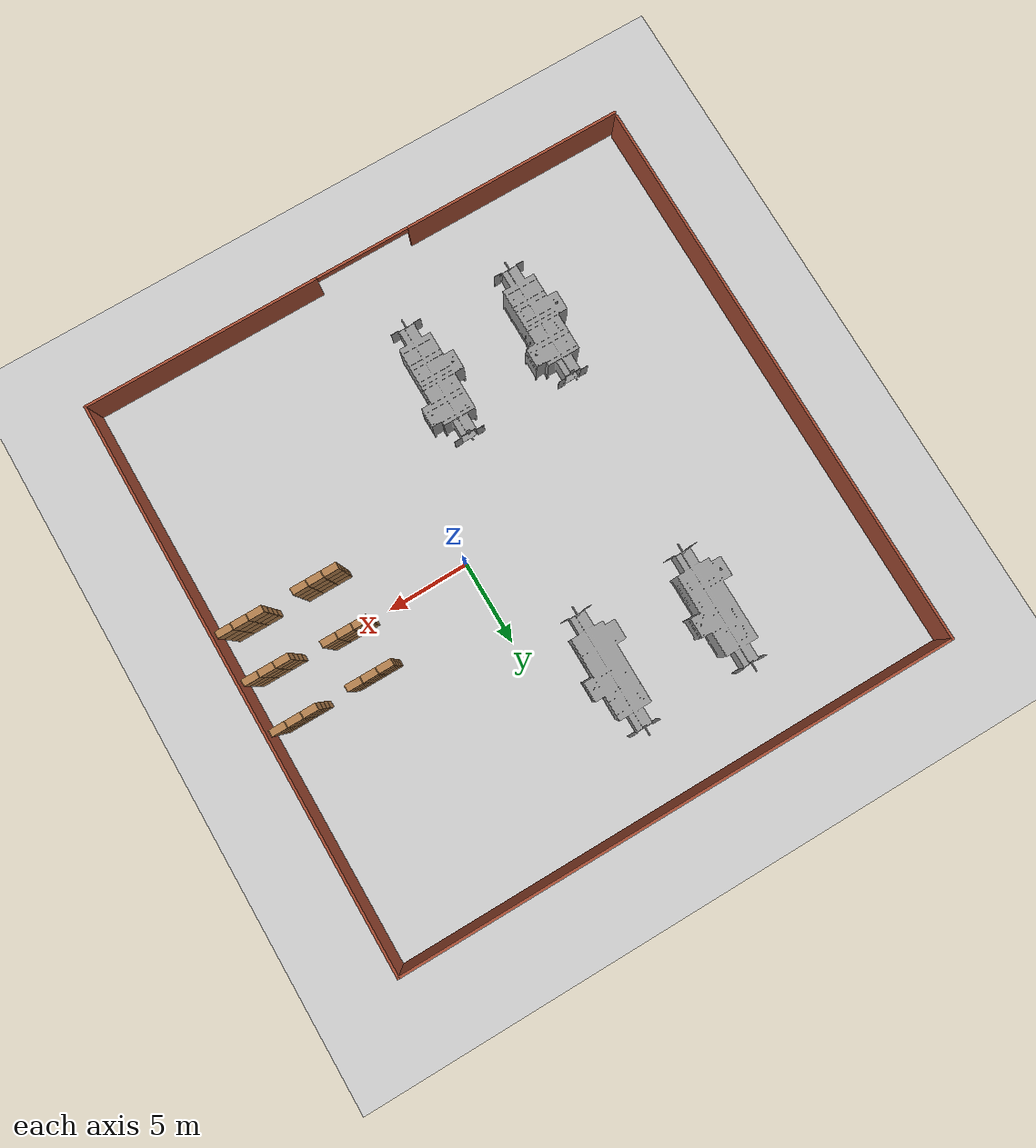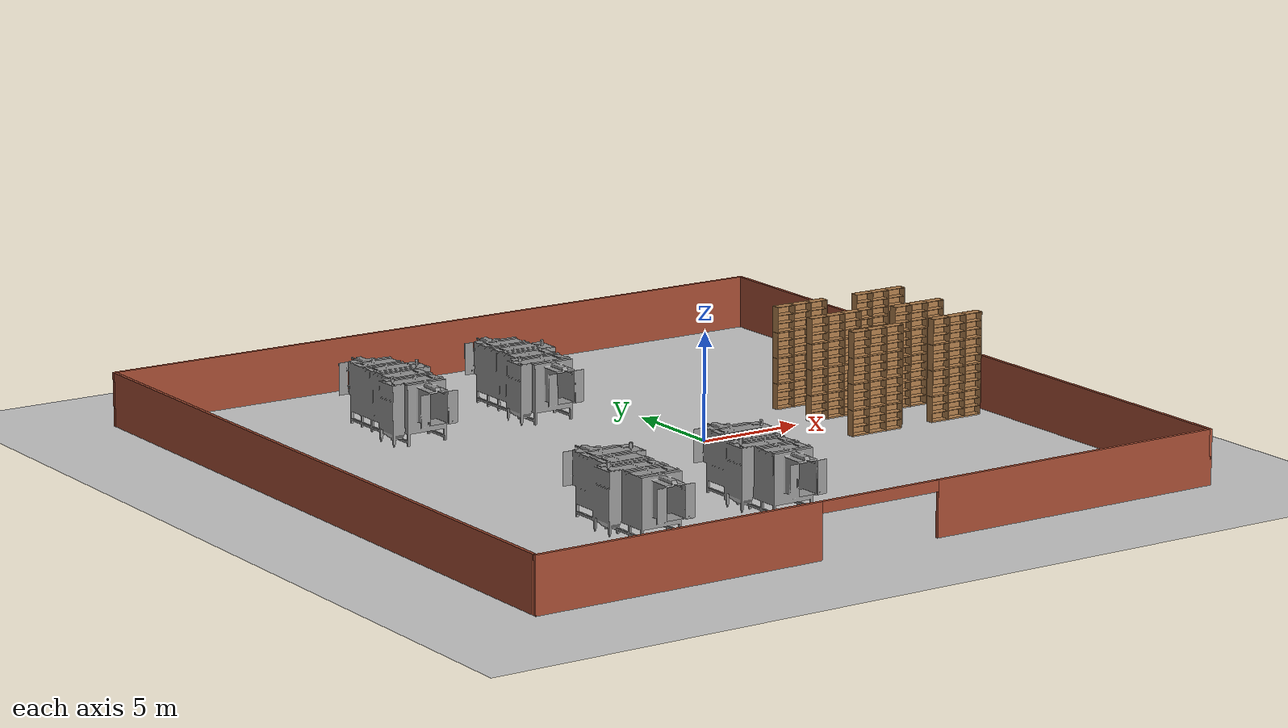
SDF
<sdf version="1.6">
 <world name="default">
  <light name="sun" type="directional">
   <pose>0 0 10 0 -0 0</pose>
   <diffuse>0.8 0.8 0.8 1</diffuse>
   <specular>0.2 0.2 0.2 1</specular>
   <attenuation>
    <range>1000</range>
    <constant>0.9</constant>
    <linear>0.01</linear>
    <quadratic>0.001</quadratic>
   </attenuation>
   <direction>-0.5 0.1 -0.9</direction>
  </light>
  <model name="ground_plane">
   <static>1</static>
   <link name="link">
    <collision name="collision">
     <geometry><plane><normal>0 0 1</normal><size>100 100</size></plane></geometry>
     <surface>
      <contact><collide_bitmask>65535</collide_bitmask></contact>
      <friction><ode><mu>100</mu><mu2>50</mu2></ode></friction>
     </surface>
    </collision>
    <visual name="visual">
     <cast_shadows>0</cast_shadows>
     <geometry><plane><normal>0 0 1</normal><size>100 100</size></plane></geometry>
     <material>
      <script><uri>file://media/materials/scripts/gazebo.material</uri><name>Gazebo/Grey</name></script>
     </material>
    </visual>
   </link>
  </model>
  <gravity>0 0 -9.8</gravity>
  <magnetic_field>6e-06 2.3e-05 -4.2e-05</magnetic_field>
  <atmosphere type="adiabatic"/>
  <physics name="default_physics" default="0" type="ode">
   <max_step_size>0.001</max_step_size>
   <real_time_factor>1</real_time_factor>
   <real_time_update_rate>1000</real_time_update_rate>
  </physics>
  <scene><ambient>0.4 0.4 0.4 1</ambient><background>0.7 0.7 0.7 1</background><shadows>1</shadows></scene>
  <spherical_coordinates>
   <surface_model>EARTH_WGS84</surface_model>
   <latitude_deg>0</latitude_deg>
   <longitude_deg>0</longitude_deg>
   <elevation>0</elevation>
   <heading_deg>0</heading_deg>
  </spherical_coordinates>
  <model name="shelf2.0_clone_0">
   <model name="shelf1.0">
    <model name="bookshelf">
     <static>1</static>
     <link name="link">
      <inertial><mass>1</mass></inertial>
      <collision name="back">
       <pose>0 0.005 0.6 0 -0 0</pose>
       <geometry><box><size>0.9 0.01 1.2</size></box></geometry>
      </collision>
      <visual name="visual1">
       <pose>0 0.005 0.6 0 -0 0</pose>
       <geometry><box><size>0.9 0.01 1.2</size></box></geometry>
       <material>
        <script><uri>file://media/materials/scripts/gazebo.material</uri><name>Gazebo/Wood</name></script>
       </material>
      </visual>
      <collision name="left_side">
       <pose>0.45 -0.195 0.6 0 -0 0</pose>
       <geometry><box><size>0.02 0.4 1.2</size></box></geometry>
      </collision>
      <visual name="visual2">
       <pose>0.45 -0.195 0.6 0 -0 0</pose>
       <geometry><box><size>0.02 0.4 1.2</size></box></geometry>
       <material>
        <script><uri>file://media/materials/scripts/gazebo.material</uri><name>Gazebo/Wood</name></script>
       </material>
      </visual>
      <collision name="right_side">
       <pose>-0.45 -0.195 0.6 0 -0 0</pose>
       <geometry><box><size>0.02 0.4 1.2</size></box></geometry>
      </collision>
      <visual name="visual3">
       <pose>-0.45 -0.195 0.6 0 -0 0</pose>
       <geometry><box><size>0.02 0.4 1.2</size></box></geometry>
       <material>
        <script><uri>file://media/materials/scripts/gazebo.material</uri><name>Gazebo/Wood</name></script>
       </material>
      </visual>
      <collision name="bottom">
       <pose>0 -0.195 0.03 0 -0 0</pose>
       <geometry><box><size>0.88 0.4 0.06</size></box></geometry>
      </collision>
      <visual name="visual4">
       <pose>0 -0.195 0.03 0 -0 0</pose>
       <geometry><box><size>0.88 0.4 0.06</size></box></geometry>
       <material>
        <script><uri>file://media/materials/scripts/gazebo.material</uri><name>Gazebo/Wood</name></script>
       </material>
      </visual>
      <collision name="top">
       <pose>0 -0.195 1.19 0 -0 0</pose>
       <geometry><box><size>0.88 0.4 0.02</size></box></geometry>
      </collision>
      <visual name="visual5">
       <pose>0 -0.195 1.19 0 -0 0</pose>
       <geometry><box><size>0.88 0.4 0.02</size></box></geometry>
       <material>
        <script><uri>file://media/materials/scripts/gazebo.material</uri><name>Gazebo/Wood</name></script>
       </material>
      </visual>
      <collision name="low_shelf">
       <pose>0 -0.195 0.43 0 -0 0</pose>
       <geometry><box><size>0.88 0.4 0.02</size></box></geometry>
      </collision>
      <visual name="visual6">
       <pose>0 -0.195 0.43 0 -0 0</pose>
       <geometry><box><size>0.88 0.4 0.02</size></box></geometry>
       <material>
        <script><uri>file://media/materials/scripts/gazebo.material</uri><name>Gazebo/Wood</name></script>
       </material>
      </visual>
      <collision name="high_shelf">
       <pose>0 -0.195 0.8 0 -0 0</pose>
       <geometry><box><size>0.88 0.4 0.02</size></box></geometry>
      </collision>
      <visual name="visual7">
       <pose>0 -0.195 0.8 0 -0 0</pose>
       <geometry><box><size>0.88 0.4 0.02</size></box></geometry>
       <material>
        <script><uri>file://media/materials/scripts/gazebo.material</uri><name>Gazebo/Wood</name></script>
       </material>
      </visual>
     </link>
     <pose>1e-06 0 -1.8 0 -0 0</pose>
    </model>
    <model name="bookshelf_clone">
     <static>1</static>
     <link name="link">
      <inertial><mass>1</mass></inertial>
      <collision name="back">
       <pose>0 0.005 0.6 0 -0 0</pose>
       <geometry><box><size>0.9 0.01 1.2</size></box></geometry>
      </collision>
      <visual name="visual1">
       <pose>0 0.005 0.6 0 -0 0</pose>
       <geometry><box><size>0.9 0.01 1.2</size></box></geometry>
       <material>
        <script><uri>file://media/materials/scripts/gazebo.material</uri><name>Gazebo/Wood</name></script>
       </material>
      </visual>
      <collision name="left_side">
       <pose>0.45 -0.195 0.6 0 -0 0</pose>
       <geometry><box><size>0.02 0.4 1.2</size></box></geometry>
      </collision>
      <visual name="visual2">
       <pose>0.45 -0.195 0.6 0 -0 0</pose>
       <geometry><box><size>0.02 0.4 1.2</size></box></geometry>
       <material>
        <script><uri>file://media/materials/scripts/gazebo.material</uri><name>Gazebo/Wood</name></script>
       </material>
      </visual>
      <collision name="right_side">
       <pose>-0.45 -0.195 0.6 0 -0 0</pose>
       <geometry><box><size>0.02 0.4 1.2</size></box></geometry>
      </collision>
      <visual name="visual3">
       <pose>-0.45 -0.195 0.6 0 -0 0</pose>
       <geometry><box><size>0.02 0.4 1.2</size></box></geometry>
       <material>
        <script><uri>file://media/materials/scripts/gazebo.material</uri><name>Gazebo/Wood</name></script>
       </material>
      </visual>
      <collision name="bottom">
       <pose>0 -0.195 0.03 0 -0 0</pose>
       <geometry><box><size>0.88 0.4 0.06</size></box></geometry>
      </collision>
      <visual name="visual4">
       <pose>0 -0.195 0.03 0 -0 0</pose>
       <geometry><box><size>0.88 0.4 0.06</size></box></geometry>
       <material>
        <script><uri>file://media/materials/scripts/gazebo.material</uri><name>Gazebo/Wood</name></script>
       </material>
      </visual>
      <collision name="top">
       <pose>0 -0.195 1.19 0 -0 0</pose>
       <geometry><box><size>0.88 0.4 0.02</size></box></geometry>
      </collision>
      <visual name="visual5">
       <pose>0 -0.195 1.19 0 -0 0</pose>
       <geometry><box><size>0.88 0.4 0.02</size></box></geometry>
       <material>
        <script><uri>file://media/materials/scripts/gazebo.material</uri><name>Gazebo/Wood</name></script>
       </material>
      </visual>
      <collision name="low_shelf">
       <pose>0 -0.195 0.43 0 -0 0</pose>
       <geometry><box><size>0.88 0.4 0.02</size></box></geometry>
      </collision>
      <visual name="visual6">
       <pose>0 -0.195 0.43 0 -0 0</pose>
       <geometry><box><size>0.88 0.4 0.02</size></box></geometry>
       <material>
        <script><uri>file://media/materials/scripts/gazebo.material</uri><name>Gazebo/Wood</name></script>
       </material>
      </visual>
      <collision name="high_shelf">
       <pose>0 -0.195 0.8 0 -0 0</pose>
       <geometry><box><size>0.88 0.4 0.02</size></box></geometry>
      </collision>
      <visual name="visual7">
       <pose>0 -0.195 0.8 0 -0 0</pose>
       <geometry><box><size>0.88 0.4 0.02</size></box></geometry>
       <material>
        <script><uri>file://media/materials/scripts/gazebo.material</uri><name>Gazebo/Wood</name></script>
       </material>
      </visual>
     </link>
     <pose>1e-06 0 -0.600002 0 -0 0</pose>
    </model>
    <model name="bookshelf_clone_0">
     <static>1</static>
     <link name="link">
      <inertial><mass>1</mass></inertial>
      <collision name="back">
       <pose>0 0.005 0.6 0 -0 0</pose>
       <geometry><box><size>0.9 0.01 1.2</size></box></geometry>
      </collision>
      <visual name="visual1">
       <pose>0 0.005 0.6 0 -0 0</pose>
       <geometry><box><size>0.9 0.01 1.2</size></box></geometry>
       <material>
        <script><uri>file://media/materials/scripts/gazebo.material</uri><name>Gazebo/Wood</name></script>
       </material>
      </visual>
      <collision name="left_side">
       <pose>0.45 -0.195 0.6 0 -0 0</pose>
       <geometry><box><size>0.02 0.4 1.2</size></box></geometry>
      </collision>
      <visual name="visual2">
       <pose>0.45 -0.195 0.6 0 -0 0</pose>
       <geometry><box><size>0.02 0.4 1.2</size></box></geometry>
       <material>
        <script><uri>file://media/materials/scripts/gazebo.material</uri><name>Gazebo/Wood</name></script>
       </material>
      </visual>
      <collision name="right_side">
       <pose>-0.45 -0.195 0.6 0 -0 0</pose>
       <geometry><box><size>0.02 0.4 1.2</size></box></geometry>
      </collision>
      <visual name="visual3">
       <pose>-0.45 -0.195 0.6 0 -0 0</pose>
       <geometry><box><size>0.02 0.4 1.2</size></box></geometry>
       <material>
        <script><uri>file://media/materials/scripts/gazebo.material</uri><name>Gazebo/Wood</name></script>
       </material>
      </visual>
      <collision name="bottom">
       <pose>0 -0.195 0.03 0 -0 0</pose>
       <geometry><box><size>0.88 0.4 0.06</size></box></geometry>
      </collision>
      <visual name="visual4">
       <pose>0 -0.195 0.03 0 -0 0</pose>
       <geometry><box><size>0.88 0.4 0.06</size></box></geometry>
       <material>
        <script><uri>file://media/materials/scripts/gazebo.material</uri><name>Gazebo/Wood</name></script>
       </material>
      </visual>
      <collision name="top">
       <pose>0 -0.195 1.19 0 -0 0</pose>
       <geometry><box><size>0.88 0.4 0.02</size></box></geometry>
      </collision>
      <visual name="visual5">
       <pose>0 -0.195 1.19 0 -0 0</pose>
       <geometry><box><size>0.88 0.4 0.02</size></box></geometry>
       <material>
        <script><uri>file://media/materials/scripts/gazebo.material</uri><name>Gazebo/Wood</name></script>
       </material>
      </visual>
      <collision name="low_shelf">
       <pose>0 -0.195 0.43 0 -0 0</pose>
       <geometry><box><size>0.88 0.4 0.02</size></box></geometry>
      </collision>
      <visual name="visual6">
       <pose>0 -0.195 0.43 0 -0 0</pose>
       <geometry><box><size>0.88 0.4 0.02</size></box></geometry>
       <material>
        <script><uri>file://media/materials/scripts/gazebo.material</uri><name>Gazebo/Wood</name></script>
       </material>
      </visual>
      <collision name="high_shelf">
       <pose>0 -0.195 0.8 0 -0 0</pose>
       <geometry><box><size>0.88 0.4 0.02</size></box></geometry>
      </collision>
      <visual name="visual7">
       <pose>0 -0.195 0.8 0 -0 0</pose>
       <geometry><box><size>0.88 0.4 0.02</size></box></geometry>
       <material>
        <script><uri>file://media/materials/scripts/gazebo.material</uri><name>Gazebo/Wood</name></script>
       </material>
      </visual>
     </link>
     <pose>1e-06 0 0.599998 0 -0 0</pose>
    </model>
    <model name="bookshelf_clone_0_clone">
     <static>1</static>
     <link name="link">
      <inertial><mass>1</mass></inertial>
      <collision name="back">
       <pose>0 0.005 0.6 0 -0 0</pose>
       <geometry><box><size>0.9 0.01 1.2</size></box></geometry>
      </collision>
      <visual name="visual1">
       <pose>0 0.005 0.6 0 -0 0</pose>
       <geometry><box><size>0.9 0.01 1.2</size></box></geometry>
       <material>
        <script><uri>file://media/materials/scripts/gazebo.material</uri><name>Gazebo/Wood</name></script>
       </material>
      </visual>
      <collision name="left_side">
       <pose>0.45 -0.195 0.6 0 -0 0</pose>
       <geometry><box><size>0.02 0.4 1.2</size></box></geometry>
      </collision>
      <visual name="visual2">
       <pose>0.45 -0.195 0.6 0 -0 0</pose>
       <geometry><box><size>0.02 0.4 1.2</size></box></geometry>
       <material>
        <script><uri>file://media/materials/scripts/gazebo.material</uri><name>Gazebo/Wood</name></script>
       </material>
      </visual>
      <collision name="right_side">
       <pose>-0.45 -0.195 0.6 0 -0 0</pose>
       <geometry><box><size>0.02 0.4 1.2</size></box></geometry>
      </collision>
      <visual name="visual3">
       <pose>-0.45 -0.195 0.6 0 -0 0</pose>
       <geometry><box><size>0.02 0.4 1.2</size></box></geometry>
       <material>
        <script><uri>file://media/materials/scripts/gazebo.material</uri><name>Gazebo/Wood</name></script>
       </material>
      </visual>
      <collision name="bottom">
       <pose>0 -0.195 0.03 0 -0 0</pose>
       <geometry><box><size>0.88 0.4 0.06</size></box></geometry>
      </collision>
      <visual name="visual4">
       <pose>0 -0.195 0.03 0 -0 0</pose>
       <geometry><box><size>0.88 0.4 0.06</size></box></geometry>
       <material>
        <script><uri>file://media/materials/scripts/gazebo.material</uri><name>Gazebo/Wood</name></script>
       </material>
      </visual>
      <collision name="top">
       <pose>0 -0.195 1.19 0 -0 0</pose>
       <geometry><box><size>0.88 0.4 0.02</size></box></geometry>
      </collision>
      <visual name="visual5">
       <pose>0 -0.195 1.19 0 -0 0</pose>
       <geometry><box><size>0.88 0.4 0.02</size></box></geometry>
       <material>
        <script><uri>file://media/materials/scripts/gazebo.material</uri><name>Gazebo/Wood</name></script>
       </material>
      </visual>
      <collision name="low_shelf">
       <pose>0 -0.195 0.43 0 -0 0</pose>
       <geometry><box><size>0.88 0.4 0.02</size></box></geometry>
      </collision>
      <visual name="visual6">
       <pose>0 -0.195 0.43 0 -0 0</pose>
       <geometry><box><size>0.88 0.4 0.02</size></box></geometry>
       <material>
        <script><uri>file://media/materials/scripts/gazebo.material</uri><name>Gazebo/Wood</name></script>
       </material>
      </visual>
      <collision name="high_shelf">
       <pose>0 -0.195 0.8 0 -0 0</pose>
       <geometry><box><size>0.88 0.4 0.02</size></box></geometry>
      </collision>
      <visual name="visual7">
       <pose>0 -0.195 0.8 0 -0 0</pose>
       <geometry><box><size>0.88 0.4 0.02</size></box></geometry>
       <material>
        <script><uri>file://media/materials/scripts/gazebo.material</uri><name>Gazebo/Wood</name></script>
       </material>
      </visual>
     </link>
     <pose>1e-06 0 1.8 0 -0 0</pose>
    </model>
    <joint name="link_JOINT_3" type="fixed">
     <parent>bookshelf::link</parent>
     <child>bookshelf_clone::link</child>
     <physics>
      <ode><limit><cfm>0</cfm><erp>0.2</erp></limit><suspension><cfm>0</cfm><erp>0.2</erp></suspension></ode>
     </physics>
    </joint>
    <joint name="link_JOINT_4" type="fixed">
     <parent>bookshelf::link</parent>
     <child>bookshelf_clone_0::link</child>
     <physics>
      <ode><limit><cfm>0</cfm><erp>0.2</erp></limit><suspension><cfm>0</cfm><erp>0.2</erp></suspension></ode>
     </physics>
    </joint>
    <joint name="link_JOINT_5" type="fixed">
     <parent>bookshelf::link</parent>
     <child>bookshelf_clone_0_clone::link</child>
     <physics>
      <ode><limit><cfm>0</cfm><erp>0.2</erp></limit><suspension><cfm>0</cfm><erp>0.2</erp></suspension></ode>
     </physics>
    </joint>
    <static>0</static>
    <pose>-0.920027 0 0 0 -0 0</pose>
   </model>
   <model name="shelf1.0_clone">
    <model name="bookshelf">
     <static>1</static>
     <link name="link">
      <inertial><mass>1</mass></inertial>
      <collision name="back">
       <pose>0 0.005 0.6 0 -0 0</pose>
       <geometry><box><size>0.9 0.01 1.2</size></box></geometry>
      </collision>
      <visual name="visual1">
       <pose>0 0.005 0.6 0 -0 0</pose>
       <geometry><box><size>0.9 0.01 1.2</size></box></geometry>
       <material>
        <script><uri>file://media/materials/scripts/gazebo.material</uri><name>Gazebo/Wood</name></script>
       </material>
      </visual>
      <collision name="left_side">
       <pose>0.45 -0.195 0.6 0 -0 0</pose>
       <geometry><box><size>0.02 0.4 1.2</size></box></geometry>
      </collision>
      <visual name="visual2">
       <pose>0.45 -0.195 0.6 0 -0 0</pose>
       <geometry><box><size>0.02 0.4 1.2</size></box></geometry>
       <material>
        <script><uri>file://media/materials/scripts/gazebo.material</uri><name>Gazebo/Wood</name></script>
       </material>
      </visual>
      <collision name="right_side">
       <pose>-0.45 -0.195 0.6 0 -0 0</pose>
       <geometry><box><size>0.02 0.4 1.2</size></box></geometry>
      </collision>
      <visual name="visual3">
       <pose>-0.45 -0.195 0.6 0 -0 0</pose>
       <geometry><box><size>0.02 0.4 1.2</size></box></geometry>
       <material>
        <script><uri>file://media/materials/scripts/gazebo.material</uri><name>Gazebo/Wood</name></script>
       </material>
      </visual>
      <collision name="bottom">
       <pose>0 -0.195 0.03 0 -0 0</pose>
       <geometry><box><size>0.88 0.4 0.06</size></box></geometry>
      </collision>
      <visual name="visual4">
       <pose>0 -0.195 0.03 0 -0 0</pose>
       <geometry><box><size>0.88 0.4 0.06</size></box></geometry>
       <material>
        <script><uri>file://media/materials/scripts/gazebo.material</uri><name>Gazebo/Wood</name></script>
       </material>
      </visual>
      <collision name="top">
       <pose>0 -0.195 1.19 0 -0 0</pose>
       <geometry><box><size>0.88 0.4 0.02</size></box></geometry>
      </collision>
      <visual name="visual5">
       <pose>0 -0.195 1.19 0 -0 0</pose>
       <geometry><box><size>0.88 0.4 0.02</size></box></geometry>
       <material>
        <script><uri>file://media/materials/scripts/gazebo.material</uri><name>Gazebo/Wood</name></script>
       </material>
      </visual>
      <collision name="low_shelf">
       <pose>0 -0.195 0.43 0 -0 0</pose>
       <geometry><box><size>0.88 0.4 0.02</size></box></geometry>
      </collision>
      <visual name="visual6">
       <pose>0 -0.195 0.43 0 -0 0</pose>
       <geometry><box><size>0.88 0.4 0.02</size></box></geometry>
       <material>
        <script><uri>file://media/materials/scripts/gazebo.material</uri><name>Gazebo/Wood</name></script>
       </material>
      </visual>
      <collision name="high_shelf">
       <pose>0 -0.195 0.8 0 -0 0</pose>
       <geometry><box><size>0.88 0.4 0.02</size></box></geometry>
      </collision>
      <visual name="visual7">
       <pose>0 -0.195 0.8 0 -0 0</pose>
       <geometry><box><size>0.88 0.4 0.02</size></box></geometry>
       <material>
        <script><uri>file://media/materials/scripts/gazebo.material</uri><name>Gazebo/Wood</name></script>
       </material>
      </visual>
     </link>
     <pose>1e-06 0 -1.8 0 -0 0</pose>
    </model>
    <model name="bookshelf_clone">
     <static>1</static>
     <link name="link">
      <inertial><mass>1</mass></inertial>
      <collision name="back">
       <pose>0 0.005 0.6 0 -0 0</pose>
       <geometry><box><size>0.9 0.01 1.2</size></box></geometry>
      </collision>
      <visual name="visual1">
       <pose>0 0.005 0.6 0 -0 0</pose>
       <geometry><box><size>0.9 0.01 1.2</size></box></geometry>
       <material>
        <script><uri>file://media/materials/scripts/gazebo.material</uri><name>Gazebo/Wood</name></script>
       </material>
      </visual>
      <collision name="left_side">
       <pose>0.45 -0.195 0.6 0 -0 0</pose>
       <geometry><box><size>0.02 0.4 1.2</size></box></geometry>
      </collision>
      <visual name="visual2">
       <pose>0.45 -0.195 0.6 0 -0 0</pose>
       <geometry><box><size>0.02 0.4 1.2</size></box></geometry>
       <material>
        <script><uri>file://media/materials/scripts/gazebo.material</uri><name>Gazebo/Wood</name></script>
       </material>
      </visual>
      <collision name="right_side">
       <pose>-0.45 -0.195 0.6 0 -0 0</pose>
       <geometry><box><size>0.02 0.4 1.2</size></box></geometry>
      </collision>
      <visual name="visual3">
       <pose>-0.45 -0.195 0.6 0 -0 0</pose>
       <geometry><box><size>0.02 0.4 1.2</size></box></geometry>
       <material>
        <script><uri>file://media/materials/scripts/gazebo.material</uri><name>Gazebo/Wood</name></script>
       </material>
      </visual>
      <collision name="bottom">
       <pose>0 -0.195 0.03 0 -0 0</pose>
       <geometry><box><size>0.88 0.4 0.06</size></box></geometry>
      </collision>
      <visual name="visual4">
       <pose>0 -0.195 0.03 0 -0 0</pose>
       <geometry><box><size>0.88 0.4 0.06</size></box></geometry>
       <material>
        <script><uri>file://media/materials/scripts/gazebo.material</uri><name>Gazebo/Wood</name></script>
       </material>
      </visual>
      <collision name="top">
       <pose>0 -0.195 1.19 0 -0 0</pose>
       <geometry><box><size>0.88 0.4 0.02</size></box></geometry>
      </collision>
      <visual name="visual5">
       <pose>0 -0.195 1.19 0 -0 0</pose>
       <geometry><box><size>0.88 0.4 0.02</size></box></geometry>
       <material>
        <script><uri>file://media/materials/scripts/gazebo.material</uri><name>Gazebo/Wood</name></script>
       </material>
      </visual>
      <collision name="low_shelf">
       <pose>0 -0.195 0.43 0 -0 0</pose>
       <geometry><box><size>0.88 0.4 0.02</size></box></geometry>
      </collision>
      <visual name="visual6">
       <pose>0 -0.195 0.43 0 -0 0</pose>
       <geometry><box><size>0.88 0.4 0.02</size></box></geometry>
       <material>
        <script><uri>file://media/materials/scripts/gazebo.material</uri><name>Gazebo/Wood</name></script>
       </material>
      </visual>
      <collision name="high_shelf">
       <pose>0 -0.195 0.8 0 -0 0</pose>
       <geometry><box><size>0.88 0.4 0.02</size></box></geometry>
      </collision>
      <visual name="visual7">
       <pose>0 -0.195 0.8 0 -0 0</pose>
       <geometry><box><size>0.88 0.4 0.02</size></box></geometry>
       <material>
        <script><uri>file://media/materials/scripts/gazebo.material</uri><name>Gazebo/Wood</name></script>
       </material>
      </visual>
     </link>
     <pose>1e-06 0 -0.600002 0 -0 0</pose>
    </model>
    <model name="bookshelf_clone_0">
     <static>1</static>
     <link name="link">
      <inertial><mass>1</mass></inertial>
      <collision name="back">
       <pose>0 0.005 0.6 0 -0 0</pose>
       <geometry><box><size>0.9 0.01 1.2</size></box></geometry>
      </collision>
      <visual name="visual1">
       <pose>0 0.005 0.6 0 -0 0</pose>
       <geometry><box><size>0.9 0.01 1.2</size></box></geometry>
       <material>
        <script><uri>file://media/materials/scripts/gazebo.material</uri><name>Gazebo/Wood</name></script>
       </material>
      </visual>
      <collision name="left_side">
       <pose>0.45 -0.195 0.6 0 -0 0</pose>
       <geometry><box><size>0.02 0.4 1.2</size></box></geometry>
      </collision>
      <visual name="visual2">
       <pose>0.45 -0.195 0.6 0 -0 0</pose>
       <geometry><box><size>0.02 0.4 1.2</size></box></geometry>
       <material>
        <script><uri>file://media/materials/scripts/gazebo.material</uri><name>Gazebo/Wood</name></script>
       </material>
      </visual>
      <collision name="right_side">
       <pose>-0.45 -0.195 0.6 0 -0 0</pose>
       <geometry><box><size>0.02 0.4 1.2</size></box></geometry>
      </collision>
      <visual name="visual3">
       <pose>-0.45 -0.195 0.6 0 -0 0</pose>
       <geometry><box><size>0.02 0.4 1.2</size></box></geometry>
       <material>
        <script><uri>file://media/materials/scripts/gazebo.material</uri><name>Gazebo/Wood</name></script>
       </material>
      </visual>
      <collision name="bottom">
       <pose>0 -0.195 0.03 0 -0 0</pose>
       <geometry><box><size>0.88 0.4 0.06</size></box></geometry>
      </collision>
      <visual name="visual4">
       <pose>0 -0.195 0.03 0 -0 0</pose>
       <geometry><box><size>0.88 0.4 0.06</size></box></geometry>
       <material>
        <script><uri>file://media/materials/scripts/gazebo.material</uri><name>Gazebo/Wood</name></script>
       </material>
      </visual>
      <collision name="top">
       <pose>0 -0.195 1.19 0 -0 0</pose>
       <geometry><box><size>0.88 0.4 0.02</size></box></geometry>
      </collision>
      <visual name="visual5">
       <pose>0 -0.195 1.19 0 -0 0</pose>
       <geometry><box><size>0.88 0.4 0.02</size></box></geometry>
       <material>
        <script><uri>file://media/materials/scripts/gazebo.material</uri><name>Gazebo/Wood</name></script>
       </material>
      </visual>
      <collision name="low_shelf">
       <pose>0 -0.195 0.43 0 -0 0</pose>
       <geometry><box><size>0.88 0.4 0.02</size></box></geometry>
      </collision>
      <visual name="visual6">
       <pose>0 -0.195 0.43 0 -0 0</pose>
       <geometry><box><size>0.88 0.4 0.02</size></box></geometry>
       <material>
        <script><uri>file://media/materials/scripts/gazebo.material</uri><name>Gazebo/Wood</name></script>
       </material>
      </visual>
      <collision name="high_shelf">
       <pose>0 -0.195 0.8 0 -0 0</pose>
       <geometry><box><size>0.88 0.4 0.02</size></box></geometry>
      </collision>
      <visual name="visual7">
       <pose>0 -0.195 0.8 0 -0 0</pose>
       <geometry><box><size>0.88 0.4 0.02</size></box></geometry>
       <material>
        <script><uri>file://media/materials/scripts/gazebo.material</uri><name>Gazebo/Wood</name></script>
       </material>
      </visual>
     </link>
     <pose>1e-06 0 0.599998 0 -0 0</pose>
    </model>
    <model name="bookshelf_clone_0_clone">
     <static>1</static>
     <link name="link">
      <inertial><mass>1</mass></inertial>
      <collision name="back">
       <pose>0 0.005 0.6 0 -0 0</pose>
       <geometry><box><size>0.9 0.01 1.2</size></box></geometry>
      </collision>
      <visual name="visual1">
       <pose>0 0.005 0.6 0 -0 0</pose>
       <geometry><box><size>0.9 0.01 1.2</size></box></geometry>
       <material>
        <script><uri>file://media/materials/scripts/gazebo.material</uri><name>Gazebo/Wood</name></script>
       </material>
      </visual>
      <collision name="left_side">
       <pose>0.45 -0.195 0.6 0 -0 0</pose>
       <geometry><box><size>0.02 0.4 1.2</size></box></geometry>
      </collision>
      <visual name="visual2">
       <pose>0.45 -0.195 0.6 0 -0 0</pose>
       <geometry><box><size>0.02 0.4 1.2</size></box></geometry>
       <material>
        <script><uri>file://media/materials/scripts/gazebo.material</uri><name>Gazebo/Wood</name></script>
       </material>
      </visual>
      <collision name="right_side">
       <pose>-0.45 -0.195 0.6 0 -0 0</pose>
       <geometry><box><size>0.02 0.4 1.2</size></box></geometry>
      </collision>
      <visual name="visual3">
       <pose>-0.45 -0.195 0.6 0 -0 0</pose>
       <geometry><box><size>0.02 0.4 1.2</size></box></geometry>
       <material>
        <script><uri>file://media/materials/scripts/gazebo.material</uri><name>Gazebo/Wood</name></script>
       </material>
      </visual>
      <collision name="bottom">
       <pose>0 -0.195 0.03 0 -0 0</pose>
       <geometry><box><size>0.88 0.4 0.06</size></box></geometry>
      </collision>
      <visual name="visual4">
       <pose>0 -0.195 0.03 0 -0 0</pose>
       <geometry><box><size>0.88 0.4 0.06</size></box></geometry>
       <material>
        <script><uri>file://media/materials/scripts/gazebo.material</uri><name>Gazebo/Wood</name></script>
       </material>
      </visual>
      <collision name="top">
       <pose>0 -0.195 1.19 0 -0 0</pose>
       <geometry><box><size>0.88 0.4 0.02</size></box></geometry>
      </collision>
      <visual name="visual5">
       <pose>0 -0.195 1.19 0 -0 0</pose>
       <geometry><box><size>0.88 0.4 0.02</size></box></geometry>
       <material>
        <script><uri>file://media/materials/scripts/gazebo.material</uri><name>Gazebo/Wood</name></script>
       </material>
      </visual>
      <collision name="low_shelf">
       <pose>0 -0.195 0.43 0 -0 0</pose>
       <geometry><box><size>0.88 0.4 0.02</size></box></geometry>
      </collision>
      <visual name="visual6">
       <pose>0 -0.195 0.43 0 -0 0</pose>
       <geometry><box><size>0.88 0.4 0.02</size></box></geometry>
       <material>
        <script><uri>file://media/materials/scripts/gazebo.material</uri><name>Gazebo/Wood</name></script>
       </material>
      </visual>
      <collision name="high_shelf">
       <pose>0 -0.195 0.8 0 -0 0</pose>
       <geometry><box><size>0.88 0.4 0.02</size></box></geometry>
      </collision>
      <visual name="visual7">
       <pose>0 -0.195 0.8 0 -0 0</pose>
       <geometry><box><size>0.88 0.4 0.02</size></box></geometry>
       <material>
        <script><uri>file://media/materials/scripts/gazebo.material</uri><name>Gazebo/Wood</name></script>
       </material>
      </visual>
     </link>
     <pose>1e-06 0 1.8 0 -0 0</pose>
    </model>
    <joint name="link_JOINT_3" type="fixed">
     <parent>bookshelf::link</parent>
     <child>bookshelf_clone::link</child>
     <physics>
      <ode><limit><cfm>0</cfm><erp>0.2</erp></limit><suspension><cfm>0</cfm><erp>0.2</erp></suspension></ode>
     </physics>
    </joint>
    <joint name="link_JOINT_4" type="fixed">
     <parent>bookshelf::link</parent>
     <child>bookshelf_clone_0::link</child>
     <physics>
      <ode><limit><cfm>0</cfm><erp>0.2</erp></limit><suspension><cfm>0</cfm><erp>0.2</erp></suspension></ode>
     </physics>
    </joint>
    <joint name="link_JOINT_5" type="fixed">
     <parent>bookshelf::link</parent>
     <child>bookshelf_clone_0_clone::link</child>
     <physics>
      <ode><limit><cfm>0</cfm><erp>0.2</erp></limit><suspension><cfm>0</cfm><erp>0.2</erp></suspension></ode>
     </physics>
    </joint>
    <static>0</static>
    <pose>-2.5e-05 0 0 0 -0 0</pose>
   </model>
   <model name="shelf1.0_clone_0">
    <model name="bookshelf">
     <static>1</static>
     <link name="link">
      <inertial><mass>1</mass></inertial>
      <collision name="back">
       <pose>0 0.005 0.6 0 -0 0</pose>
       <geometry><box><size>0.9 0.01 1.2</size></box></geometry>
      </collision>
      <visual name="visual1">
       <pose>0 0.005 0.6 0 -0 0</pose>
       <geometry><box><size>0.9 0.01 1.2</size></box></geometry>
       <material>
        <script><uri>file://media/materials/scripts/gazebo.material</uri><name>Gazebo/Wood</name></script>
       </material>
      </visual>
      <collision name="left_side">
       <pose>0.45 -0.195 0.6 0 -0 0</pose>
       <geometry><box><size>0.02 0.4 1.2</size></box></geometry>
      </collision>
      <visual name="visual2">
       <pose>0.45 -0.195 0.6 0 -0 0</pose>
       <geometry><box><size>0.02 0.4 1.2</size></box></geometry>
       <material>
        <script><uri>file://media/materials/scripts/gazebo.material</uri><name>Gazebo/Wood</name></script>
       </material>
      </visual>
      <collision name="right_side">
       <pose>-0.45 -0.195 0.6 0 -0 0</pose>
       <geometry><box><size>0.02 0.4 1.2</size></box></geometry>
      </collision>
      <visual name="visual3">
       <pose>-0.45 -0.195 0.6 0 -0 0</pose>
       <geometry><box><size>0.02 0.4 1.2</size></box></geometry>
       <material>
        <script><uri>file://media/materials/scripts/gazebo.material</uri><name>Gazebo/Wood</name></script>
       </material>
      </visual>
      <collision name="bottom">
       <pose>0 -0.195 0.03 0 -0 0</pose>
       <geometry><box><size>0.88 0.4 0.06</size></box></geometry>
      </collision>
      <visual name="visual4">
       <pose>0 -0.195 0.03 0 -0 0</pose>
       <geometry><box><size>0.88 0.4 0.06</size></box></geometry>
       <material>
        <script><uri>file://media/materials/scripts/gazebo.material</uri><name>Gazebo/Wood</name></script>
       </material>
      </visual>
      <collision name="top">
       <pose>0 -0.195 1.19 0 -0 0</pose>
       <geometry><box><size>0.88 0.4 0.02</size></box></geometry>
      </collision>
      <visual name="visual5">
       <pose>0 -0.195 1.19 0 -0 0</pose>
       <geometry><box><size>0.88 0.4 0.02</size></box></geometry>
       <material>
        <script><uri>file://media/materials/scripts/gazebo.material</uri><name>Gazebo/Wood</name></script>
       </material>
      </visual>
      <collision name="low_shelf">
       <pose>0 -0.195 0.43 0 -0 0</pose>
       <geometry><box><size>0.88 0.4 0.02</size></box></geometry>
      </collision>
      <visual name="visual6">
       <pose>0 -0.195 0.43 0 -0 0</pose>
       <geometry><box><size>0.88 0.4 0.02</size></box></geometry>
       <material>
        <script><uri>file://media/materials/scripts/gazebo.material</uri><name>Gazebo/Wood</name></script>
       </material>
      </visual>
      <collision name="high_shelf">
       <pose>0 -0.195 0.8 0 -0 0</pose>
       <geometry><box><size>0.88 0.4 0.02</size></box></geometry>
      </collision>
      <visual name="visual7">
       <pose>0 -0.195 0.8 0 -0 0</pose>
       <geometry><box><size>0.88 0.4 0.02</size></box></geometry>
       <material>
        <script><uri>file://media/materials/scripts/gazebo.material</uri><name>Gazebo/Wood</name></script>
       </material>
      </visual>
     </link>
     <pose>1e-06 0 -1.8 0 -0 0</pose>
    </model>
    <model name="bookshelf_clone">
     <static>1</static>
     <link name="link">
      <inertial><mass>1</mass></inertial>
      <collision name="back">
       <pose>0 0.005 0.6 0 -0 0</pose>
       <geometry><box><size>0.9 0.01 1.2</size></box></geometry>
      </collision>
      <visual name="visual1">
       <pose>0 0.005 0.6 0 -0 0</pose>
       <geometry><box><size>0.9 0.01 1.2</size></box></geometry>
       <material>
        <script><uri>file://media/materials/scripts/gazebo.material</uri><name>Gazebo/Wood</name></script>
       </material>
      </visual>
      <collision name="left_side">
       <pose>0.45 -0.195 0.6 0 -0 0</pose>
       <geometry><box><size>0.02 0.4 1.2</size></box></geometry>
      </collision>
      <visual name="visual2">
       <pose>0.45 -0.195 0.6 0 -0 0</pose>
       <geometry><box><size>0.02 0.4 1.2</size></box></geometry>
       <material>
        <script><uri>file://media/materials/scripts/gazebo.material</uri><name>Gazebo/Wood</name></script>
       </material>
      </visual>
      <collision name="right_side">
       <pose>-0.45 -0.195 0.6 0 -0 0</pose>
       <geometry><box><size>0.02 0.4 1.2</size></box></geometry>
      </collision>
      <visual name="visual3">
       <pose>-0.45 -0.195 0.6 0 -0 0</pose>
       <geometry><box><size>0.02 0.4 1.2</size></box></geometry>
       <material>
        <script><uri>file://media/materials/scripts/gazebo.material</uri><name>Gazebo/Wood</name></script>
       </material>
      </visual>
      <collision name="bottom">
       <pose>0 -0.195 0.03 0 -0 0</pose>
       <geometry><box><size>0.88 0.4 0.06</size></box></geometry>
      </collision>
      <visual name="visual4">
       <pose>0 -0.195 0.03 0 -0 0</pose>
       <geometry><box><size>0.88 0.4 0.06</size></box></geometry>
       <material>
        <script><uri>file://media/materials/scripts/gazebo.material</uri><name>Gazebo/Wood</name></script>
       </material>
      </visual>
      <collision name="top">
       <pose>0 -0.195 1.19 0 -0 0</pose>
       <geometry><box><size>0.88 0.4 0.02</size></box></geometry>
      </collision>
      <visual name="visual5">
       <pose>0 -0.195 1.19 0 -0 0</pose>
       <geometry><box><size>0.88 0.4 0.02</size></box></geometry>
       <material>
        <script><uri>file://media/materials/scripts/gazebo.material</uri><name>Gazebo/Wood</name></script>
       </material>
      </visual>
      <collision name="low_shelf">
       <pose>0 -0.195 0.43 0 -0 0</pose>
       <geometry><box><size>0.88 0.4 0.02</size></box></geometry>
      </collision>
      <visual name="visual6">
       <pose>0 -0.195 0.43 0 -0 0</pose>
       <geometry><box><size>0.88 0.4 0.02</size></box></geometry>
       <material>
        <script><uri>file://media/materials/scripts/gazebo.material</uri><name>Gazebo/Wood</name></script>
       </material>
      </visual>
      <collision name="high_shelf">
       <pose>0 -0.195 0.8 0 -0 0</pose>
       <geometry><box><size>0.88 0.4 0.02</size></box></geometry>
      </collision>
      <visual name="visual7">
       <pose>0 -0.195 0.8 0 -0 0</pose>
       <geometry><box><size>0.88 0.4 0.02</size></box></geometry>
       <material>
        <script><uri>file://media/materials/scripts/gazebo.material</uri><name>Gazebo/Wood</name></script>
       </material>
      </visual>
     </link>
     <pose>1e-06 0 -0.600002 0 -0 0</pose>
    </model>
    <model name="bookshelf_clone_0">
     <static>1</static>
     <link name="link">
      <inertial><mass>1</mass></inertial>
      <collision name="back">
       <pose>0 0.005 0.6 0 -0 0</pose>
       <geometry><box><size>0.9 0.01 1.2</size></box></geometry>
      </collision>
      <visual name="visual1">
       <pose>0 0.005 0.6 0 -0 0</pose>
       <geometry><box><size>0.9 0.01 1.2</size></box></geometry>
       <material>
        <script><uri>file://media/materials/scripts/gazebo.material</uri><name>Gazebo/Wood</name></script>
       </material>
      </visual>
      <collision name="left_side">
       <pose>0.45 -0.195 0.6 0 -0 0</pose>
       <geometry><box><size>0.02 0.4 1.2</size></box></geometry>
      </collision>
      <visual name="visual2">
       <pose>0.45 -0.195 0.6 0 -0 0</pose>
       <geometry><box><size>0.02 0.4 1.2</size></box></geometry>
       <material>
        <script><uri>file://media/materials/scripts/gazebo.material</uri><name>Gazebo/Wood</name></script>
       </material>
      </visual>
      <collision name="right_side">
       <pose>-0.45 -0.195 0.6 0 -0 0</pose>
       <geometry><box><size>0.02 0.4 1.2</size></box></geometry>
      </collision>
      <visual name="visual3">
       <pose>-0.45 -0.195 0.6 0 -0 0</pose>
       <geometry><box><size>0.02 0.4 1.2</size></box></geometry>
       <material>
        <script><uri>file://media/materials/scripts/gazebo.material</uri><name>Gazebo/Wood</name></script>
       </material>
      </visual>
      <collision name="bottom">
       <pose>0 -0.195 0.03 0 -0 0</pose>
       <geometry><box><size>0.88 0.4 0.06</size></box></geometry>
      </collision>
      <visual name="visual4">
       <pose>0 -0.195 0.03 0 -0 0</pose>
       <geometry><box><size>0.88 0.4 0.06</size></box></geometry>
       <material>
        <script><uri>file://media/materials/scripts/gazebo.material</uri><name>Gazebo/Wood</name></script>
       </material>
      </visual>
      <collision name="top">
       <pose>0 -0.195 1.19 0 -0 0</pose>
       <geometry><box><size>0.88 0.4 0.02</size></box></geometry>
      </collision>
      <visual name="visual5">
       <pose>0 -0.195 1.19 0 -0 0</pose>
       <geometry><box><size>0.88 0.4 0.02</size></box></geometry>
       <material>
        <script><uri>file://media/materials/scripts/gazebo.material</uri><name>Gazebo/Wood</name></script>
       </material>
      </visual>
      <collision name="low_shelf">
       <pose>0 -0.195 0.43 0 -0 0</pose>
       <geometry><box><size>0.88 0.4 0.02</size></box></geometry>
      </collision>
      <visual name="visual6">
       <pose>0 -0.195 0.43 0 -0 0</pose>
       <geometry><box><size>0.88 0.4 0.02</size></box></geometry>
       <material>
        <script><uri>file://media/materials/scripts/gazebo.material</uri><name>Gazebo/Wood</name></script>
       </material>
      </visual>
      <collision name="high_shelf">
       <pose>0 -0.195 0.8 0 -0 0</pose>
       <geometry><box><size>0.88 0.4 0.02</size></box></geometry>
      </collision>
      <visual name="visual7">
       <pose>0 -0.195 0.8 0 -0 0</pose>
       <geometry><box><size>0.88 0.4 0.02</size></box></geometry>
       <material>
        <script><uri>file://media/materials/scripts/gazebo.material</uri><name>Gazebo/Wood</name></script>
       </material>
      </visual>
     </link>
     <pose>1e-06 0 0.599998 0 -0 0</pose>
    </model>
    <model name="bookshelf_clone_0_clone">
     <static>1</static>
     <link name="link">
      <inertial><mass>1</mass></inertial>
      <collision name="back">
       <pose>0 0.005 0.6 0 -0 0</pose>
       <geometry><box><size>0.9 0.01 1.2</size></box></geometry>
      </collision>
      <visual name="visual1">
       <pose>0 0.005 0.6 0 -0 0</pose>
       <geometry><box><size>0.9 0.01 1.2</size></box></geometry>
       <material>
        <script><uri>file://media/materials/scripts/gazebo.material</uri><name>Gazebo/Wood</name></script>
       </material>
      </visual>
      <collision name="left_side">
       <pose>0.45 -0.195 0.6 0 -0 0</pose>
       <geometry><box><size>0.02 0.4 1.2</size></box></geometry>
      </collision>
      <visual name="visual2">
       <pose>0.45 -0.195 0.6 0 -0 0</pose>
       <geometry><box><size>0.02 0.4 1.2</size></box></geometry>
       <material>
        <script><uri>file://media/materials/scripts/gazebo.material</uri><name>Gazebo/Wood</name></script>
       </material>
      </visual>
      <collision name="right_side">
       <pose>-0.45 -0.195 0.6 0 -0 0</pose>
       <geometry><box><size>0.02 0.4 1.2</size></box></geometry>
      </collision>
      <visual name="visual3">
       <pose>-0.45 -0.195 0.6 0 -0 0</pose>
       <geometry><box><size>0.02 0.4 1.2</size></box></geometry>
       <material>
        <script><uri>file://media/materials/scripts/gazebo.material</uri><name>Gazebo/Wood</name></script>
       </material>
      </visual>
      <collision name="bottom">
       <pose>0 -0.195 0.03 0 -0 0</pose>
       <geometry><box><size>0.88 0.4 0.06</size></box></geometry>
      </collision>
      <visual name="visual4">
       <pose>0 -0.195 0.03 0 -0 0</pose>
       <geometry><box><size>0.88 0.4 0.06</size></box></geometry>
       <material>
        <script><uri>file://media/materials/scripts/gazebo.material</uri><name>Gazebo/Wood</name></script>
       </material>
      </visual>
      <collision name="top">
       <pose>0 -0.195 1.19 0 -0 0</pose>
       <geometry><box><size>0.88 0.4 0.02</size></box></geometry>
      </collision>
      <visual name="visual5">
       <pose>0 -0.195 1.19 0 -0 0</pose>
       <geometry><box><size>0.88 0.4 0.02</size></box></geometry>
       <material>
        <script><uri>file://media/materials/scripts/gazebo.material</uri><name>Gazebo/Wood</name></script>
       </material>
      </visual>
      <collision name="low_shelf">
       <pose>0 -0.195 0.43 0 -0 0</pose>
       <geometry><box><size>0.88 0.4 0.02</size></box></geometry>
      </collision>
      <visual name="visual6">
       <pose>0 -0.195 0.43 0 -0 0</pose>
       <geometry><box><size>0.88 0.4 0.02</size></box></geometry>
       <material>
        <script><uri>file://media/materials/scripts/gazebo.material</uri><name>Gazebo/Wood</name></script>
       </material>
      </visual>
      <collision name="high_shelf">
       <pose>0 -0.195 0.8 0 -0 0</pose>
       <geometry><box><size>0.88 0.4 0.02</size></box></geometry>
      </collision>
      <visual name="visual7">
       <pose>0 -0.195 0.8 0 -0 0</pose>
       <geometry><box><size>0.88 0.4 0.02</size></box></geometry>
       <material>
        <script><uri>file://media/materials/scripts/gazebo.material</uri><name>Gazebo/Wood</name></script>
       </material>
      </visual>
     </link>
     <pose>1e-06 0 1.8 0 -0 0</pose>
    </model>
    <joint name="link_JOINT_3" type="fixed">
     <parent>bookshelf::link</parent>
     <child>bookshelf_clone::link</child>
     <physics>
      <ode><limit><cfm>0</cfm><erp>0.2</erp></limit><suspension><cfm>0</cfm><erp>0.2</erp></suspension></ode>
     </physics>
    </joint>
    <joint name="link_JOINT_4" type="fixed">
     <parent>bookshelf::link</parent>
     <child>bookshelf_clone_0::link</child>
     <physics>
      <ode><limit><cfm>0</cfm><erp>0.2</erp></limit><suspension><cfm>0</cfm><erp>0.2</erp></suspension></ode>
     </physics>
    </joint>
    <joint name="link_JOINT_5" type="fixed">
     <parent>bookshelf::link</parent>
     <child>bookshelf_clone_0_clone::link</child>
     <physics>
      <ode><limit><cfm>0</cfm><erp>0.2</erp></limit><suspension><cfm>0</cfm><erp>0.2</erp></suspension></ode>
     </physics>
    </joint>
    <static>0</static>
    <pose>0.919977 0 0 0 -0 0</pose>
   </model>
   <joint name="link_JOINT_0" type="fixed">
    <parent>shelf1.0::bookshelf::link</parent>
    <child>shelf1.0_clone::bookshelf::link</child>
    <physics>
     <ode><limit><cfm>0</cfm><erp>0.2</erp></limit><suspension><cfm>0</cfm><erp>0.2</erp></suspension></ode>
    </physics>
   </joint>
   <joint name="link_JOINT_1" type="fixed">
    <parent>shelf1.0::bookshelf::link</parent>
    <child>shelf1.0_clone_0::bookshelf::link</child>
    <physics>
     <ode><limit><cfm>0</cfm><erp>0.2</erp></limit><suspension><cfm>0</cfm><erp>0.2</erp></suspension></ode>
    </physics>
   </joint>
   <static>0</static>
   <pose>7.26008 -2.72475 1.80812 0 -0 0</pose>
  </model>
  <model name="shelf2.0_clone_1">
   <model name="shelf1.0">
    <model name="bookshelf">
     <static>1</static>
     <link name="link">
      <inertial><mass>1</mass></inertial>
      <collision name="back">
       <pose>0 0.005 0.6 0 -0 0</pose>
       <geometry><box><size>0.9 0.01 1.2</size></box></geometry>
      </collision>
      <visual name="visual1">
       <pose>0 0.005 0.6 0 -0 0</pose>
       <geometry><box><size>0.9 0.01 1.2</size></box></geometry>
       <material>
        <script><uri>file://media/materials/scripts/gazebo.material</uri><name>Gazebo/Wood</name></script>
       </material>
      </visual>
      <collision name="left_side">
       <pose>0.45 -0.195 0.6 0 -0 0</pose>
       <geometry><box><size>0.02 0.4 1.2</size></box></geometry>
      </collision>
      <visual name="visual2">
       <pose>0.45 -0.195 0.6 0 -0 0</pose>
       <geometry><box><size>0.02 0.4 1.2</size></box></geometry>
       <material>
        <script><uri>file://media/materials/scripts/gazebo.material</uri><name>Gazebo/Wood</name></script>
       </material>
      </visual>
      <collision name="right_side">
       <pose>-0.45 -0.195 0.6 0 -0 0</pose>
       <geometry><box><size>0.02 0.4 1.2</size></box></geometry>
      </collision>
      <visual name="visual3">
       <pose>-0.45 -0.195 0.6 0 -0 0</pose>
       <geometry><box><size>0.02 0.4 1.2</size></box></geometry>
       <material>
        <script><uri>file://media/materials/scripts/gazebo.material</uri><name>Gazebo/Wood</name></script>
       </material>
      </visual>
      <collision name="bottom">
       <pose>0 -0.195 0.03 0 -0 0</pose>
       <geometry><box><size>0.88 0.4 0.06</size></box></geometry>
      </collision>
      <visual name="visual4">
       <pose>0 -0.195 0.03 0 -0 0</pose>
       <geometry><box><size>0.88 0.4 0.06</size></box></geometry>
       <material>
        <script><uri>file://media/materials/scripts/gazebo.material</uri><name>Gazebo/Wood</name></script>
       </material>
      </visual>
      <collision name="top">
       <pose>0 -0.195 1.19 0 -0 0</pose>
       <geometry><box><size>0.88 0.4 0.02</size></box></geometry>
      </collision>
      <visual name="visual5">
       <pose>0 -0.195 1.19 0 -0 0</pose>
       <geometry><box><size>0.88 0.4 0.02</size></box></geometry>
       <material>
        <script><uri>file://media/materials/scripts/gazebo.material</uri><name>Gazebo/Wood</name></script>
       </material>
      </visual>
      <collision name="low_shelf">
       <pose>0 -0.195 0.43 0 -0 0</pose>
       <geometry><box><size>0.88 0.4 0.02</size></box></geometry>
      </collision>
      <visual name="visual6">
       <pose>0 -0.195 0.43 0 -0 0</pose>
       <geometry><box><size>0.88 0.4 0.02</size></box></geometry>
       <material>
        <script><uri>file://media/materials/scripts/gazebo.material</uri><name>Gazebo/Wood</name></script>
       </material>
      </visual>
      <collision name="high_shelf">
       <pose>0 -0.195 0.8 0 -0 0</pose>
       <geometry><box><size>0.88 0.4 0.02</size></box></geometry>
      </collision>
      <visual name="visual7">
       <pose>0 -0.195 0.8 0 -0 0</pose>
       <geometry><box><size>0.88 0.4 0.02</size></box></geometry>
       <material>
        <script><uri>file://media/materials/scripts/gazebo.material</uri><name>Gazebo/Wood</name></script>
       </material>
      </visual>
     </link>
     <pose>1e-06 0 -1.8 0 -0 0</pose>
    </model>
    <model name="bookshelf_clone">
     <static>1</static>
     <link name="link">
      <inertial><mass>1</mass></inertial>
      <collision name="back">
       <pose>0 0.005 0.6 0 -0 0</pose>
       <geometry><box><size>0.9 0.01 1.2</size></box></geometry>
      </collision>
      <visual name="visual1">
       <pose>0 0.005 0.6 0 -0 0</pose>
       <geometry><box><size>0.9 0.01 1.2</size></box></geometry>
       <material>
        <script><uri>file://media/materials/scripts/gazebo.material</uri><name>Gazebo/Wood</name></script>
       </material>
      </visual>
      <collision name="left_side">
       <pose>0.45 -0.195 0.6 0 -0 0</pose>
       <geometry><box><size>0.02 0.4 1.2</size></box></geometry>
      </collision>
      <visual name="visual2">
       <pose>0.45 -0.195 0.6 0 -0 0</pose>
       <geometry><box><size>0.02 0.4 1.2</size></box></geometry>
       <material>
        <script><uri>file://media/materials/scripts/gazebo.material</uri><name>Gazebo/Wood</name></script>
       </material>
      </visual>
      <collision name="right_side">
       <pose>-0.45 -0.195 0.6 0 -0 0</pose>
       <geometry><box><size>0.02 0.4 1.2</size></box></geometry>
      </collision>
      <visual name="visual3">
       <pose>-0.45 -0.195 0.6 0 -0 0</pose>
       <geometry><box><size>0.02 0.4 1.2</size></box></geometry>
       <material>
        <script><uri>file://media/materials/scripts/gazebo.material</uri><name>Gazebo/Wood</name></script>
       </material>
      </visual>
      <collision name="bottom">
       <pose>0 -0.195 0.03 0 -0 0</pose>
       <geometry><box><size>0.88 0.4 0.06</size></box></geometry>
      </collision>
      <visual name="visual4">
       <pose>0 -0.195 0.03 0 -0 0</pose>
       <geometry><box><size>0.88 0.4 0.06</size></box></geometry>
       <material>
        <script><uri>file://media/materials/scripts/gazebo.material</uri><name>Gazebo/Wood</name></script>
       </material>
      </visual>
      <collision name="top">
       <pose>0 -0.195 1.19 0 -0 0</pose>
       <geometry><box><size>0.88 0.4 0.02</size></box></geometry>
      </collision>
      <visual name="visual5">
       <pose>0 -0.195 1.19 0 -0 0</pose>
       <geometry><box><size>0.88 0.4 0.02</size></box></geometry>
       <material>
        <script><uri>file://media/materials/scripts/gazebo.material</uri><name>Gazebo/Wood</name></script>
       </material>
      </visual>
      <collision name="low_shelf">
       <pose>0 -0.195 0.43 0 -0 0</pose>
       <geometry><box><size>0.88 0.4 0.02</size></box></geometry>
      </collision>
      <visual name="visual6">
       <pose>0 -0.195 0.43 0 -0 0</pose>
       <geometry><box><size>0.88 0.4 0.02</size></box></geometry>
       <material>
        <script><uri>file://media/materials/scripts/gazebo.material</uri><name>Gazebo/Wood</name></script>
       </material>
      </visual>
      <collision name="high_shelf">
       <pose>0 -0.195 0.8 0 -0 0</pose>
       <geometry><box><size>0.88 0.4 0.02</size></box></geometry>
      </collision>
      <visual name="visual7">
       <pose>0 -0.195 0.8 0 -0 0</pose>
       <geometry><box><size>0.88 0.4 0.02</size></box></geometry>
       <material>
        <script><uri>file://media/materials/scripts/gazebo.material</uri><name>Gazebo/Wood</name></script>
       </material>
      </visual>
     </link>
     <pose>1e-06 0 -0.600002 0 -0 0</pose>
    </model>
    <model name="bookshelf_clone_0">
     <static>1</static>
     <link name="link">
      <inertial><mass>1</mass></inertial>
      <collision name="back">
       <pose>0 0.005 0.6 0 -0 0</pose>
       <geometry><box><size>0.9 0.01 1.2</size></box></geometry>
      </collision>
      <visual name="visual1">
       <pose>0 0.005 0.6 0 -0 0</pose>
       <geometry><box><size>0.9 0.01 1.2</size></box></geometry>
       <material>
        <script><uri>file://media/materials/scripts/gazebo.material</uri><name>Gazebo/Wood</name></script>
       </material>
      </visual>
      <collision name="left_side">
       <pose>0.45 -0.195 0.6 0 -0 0</pose>
       <geometry><box><size>0.02 0.4 1.2</size></box></geometry>
      </collision>
      <visual name="visual2">
       <pose>0.45 -0.195 0.6 0 -0 0</pose>
       <geometry><box><size>0.02 0.4 1.2</size></box></geometry>
       <material>
        <script><uri>file://media/materials/scripts/gazebo.material</uri><name>Gazebo/Wood</name></script>
       </material>
      </visual>
      <collision name="right_side">
       <pose>-0.45 -0.195 0.6 0 -0 0</pose>
       <geometry><box><size>0.02 0.4 1.2</size></box></geometry>
      </collision>
      <visual name="visual3">
       <pose>-0.45 -0.195 0.6 0 -0 0</pose>
       <geometry><box><size>0.02 0.4 1.2</size></box></geometry>
       <material>
        <script><uri>file://media/materials/scripts/gazebo.material</uri><name>Gazebo/Wood</name></script>
       </material>
      </visual>
      <collision name="bottom">
       <pose>0 -0.195 0.03 0 -0 0</pose>
       <geometry><box><size>0.88 0.4 0.06</size></box></geometry>
      </collision>
      <visual name="visual4">
       <pose>0 -0.195 0.03 0 -0 0</pose>
       <geometry><box><size>0.88 0.4 0.06</size></box></geometry>
       <material>
        <script><uri>file://media/materials/scripts/gazebo.material</uri><name>Gazebo/Wood</name></script>
       </material>
      </visual>
      <collision name="top">
       <pose>0 -0.195 1.19 0 -0 0</pose>
       <geometry><box><size>0.88 0.4 0.02</size></box></geometry>
      </collision>
      <visual name="visual5">
       <pose>0 -0.195 1.19 0 -0 0</pose>
       <geometry><box><size>0.88 0.4 0.02</size></box></geometry>
       <material>
        <script><uri>file://media/materials/scripts/gazebo.material</uri><name>Gazebo/Wood</name></script>
       </material>
      </visual>
      <collision name="low_shelf">
       <pose>0 -0.195 0.43 0 -0 0</pose>
       <geometry><box><size>0.88 0.4 0.02</size></box></geometry>
      </collision>
      <visual name="visual6">
       <pose>0 -0.195 0.43 0 -0 0</pose>
       <geometry><box><size>0.88 0.4 0.02</size></box></geometry>
       <material>
        <script><uri>file://media/materials/scripts/gazebo.material</uri><name>Gazebo/Wood</name></script>
       </material>
      </visual>
      <collision name="high_shelf">
       <pose>0 -0.195 0.8 0 -0 0</pose>
       <geometry><box><size>0.88 0.4 0.02</size></box></geometry>
      </collision>
      <visual name="visual7">
       <pose>0 -0.195 0.8 0 -0 0</pose>
       <geometry><box><size>0.88 0.4 0.02</size></box></geometry>
       <material>
        <script><uri>file://media/materials/scripts/gazebo.material</uri><name>Gazebo/Wood</name></script>
       </material>
      </visual>
     </link>
     <pose>1e-06 0 0.599998 0 -0 0</pose>
    </model>
    <model name="bookshelf_clone_0_clone">
     <static>1</static>
     <link name="link">
      <inertial><mass>1</mass></inertial>
      <collision name="back">
       <pose>0 0.005 0.6 0 -0 0</pose>
       <geometry><box><size>0.9 0.01 1.2</size></box></geometry>
      </collision>
      <visual name="visual1">
       <pose>0 0.005 0.6 0 -0 0</pose>
       <geometry><box><size>0.9 0.01 1.2</size></box></geometry>
       <material>
        <script><uri>file://media/materials/scripts/gazebo.material</uri><name>Gazebo/Wood</name></script>
       </material>
      </visual>
      <collision name="left_side">
       <pose>0.45 -0.195 0.6 0 -0 0</pose>
       <geometry><box><size>0.02 0.4 1.2</size></box></geometry>
      </collision>
      <visual name="visual2">
       <pose>0.45 -0.195 0.6 0 -0 0</pose>
       <geometry><box><size>0.02 0.4 1.2</size></box></geometry>
       <material>
        <script><uri>file://media/materials/scripts/gazebo.material</uri><name>Gazebo/Wood</name></script>
       </material>
      </visual>
      <collision name="right_side">
       <pose>-0.45 -0.195 0.6 0 -0 0</pose>
       <geometry><box><size>0.02 0.4 1.2</size></box></geometry>
      </collision>
      <visual name="visual3">
       <pose>-0.45 -0.195 0.6 0 -0 0</pose>
       <geometry><box><size>0.02 0.4 1.2</size></box></geometry>
       <material>
        <script><uri>file://media/materials/scripts/gazebo.material</uri><name>Gazebo/Wood</name></script>
       </material>
      </visual>
      <collision name="bottom">
       <pose>0 -0.195 0.03 0 -0 0</pose>
       <geometry><box><size>0.88 0.4 0.06</size></box></geometry>
      </collision>
      <visual name="visual4">
       <pose>0 -0.195 0.03 0 -0 0</pose>
       <geometry><box><size>0.88 0.4 0.06</size></box></geometry>
       <material>
        <script><uri>file://media/materials/scripts/gazebo.material</uri><name>Gazebo/Wood</name></script>
       </material>
      </visual>
      <collision name="top">
       <pose>0 -0.195 1.19 0 -0 0</pose>
       <geometry><box><size>0.88 0.4 0.02</size></box></geometry>
      </collision>
      <visual name="visual5">
       <pose>0 -0.195 1.19 0 -0 0</pose>
       <geometry><box><size>0.88 0.4 0.02</size></box></geometry>
       <material>
        <script><uri>file://media/materials/scripts/gazebo.material</uri><name>Gazebo/Wood</name></script>
       </material>
      </visual>
      <collision name="low_shelf">
       <pose>0 -0.195 0.43 0 -0 0</pose>
       <geometry><box><size>0.88 0.4 0.02</size></box></geometry>
      </collision>
      <visual name="visual6">
       <pose>0 -0.195 0.43 0 -0 0</pose>
       <geometry><box><size>0.88 0.4 0.02</size></box></geometry>
       <material>
        <script><uri>file://media/materials/scripts/gazebo.material</uri><name>Gazebo/Wood</name></script>
       </material>
      </visual>
      <collision name="high_shelf">
       <pose>0 -0.195 0.8 0 -0 0</pose>
       <geometry><box><size>0.88 0.4 0.02</size></box></geometry>
      </collision>
      <visual name="visual7">
       <pose>0 -0.195 0.8 0 -0 0</pose>
       <geometry><box><size>0.88 0.4 0.02</size></box></geometry>
       <material>
        <script><uri>file://media/materials/scripts/gazebo.material</uri><name>Gazebo/Wood</name></script>
       </material>
      </visual>
     </link>
     <pose>1e-06 0 1.8 0 -0 0</pose>
    </model>
    <joint name="link_JOINT_3" type="fixed">
     <parent>bookshelf::link</parent>
     <child>bookshelf_clone::link</child>
     <physics>
      <ode><limit><cfm>0</cfm><erp>0.2</erp></limit><suspension><cfm>0</cfm><erp>0.2</erp></suspension></ode>
     </physics>
    </joint>
    <joint name="link_JOINT_4" type="fixed">
     <parent>bookshelf::link</parent>
     <child>bookshelf_clone_0::link</child>
     <physics>
      <ode><limit><cfm>0</cfm><erp>0.2</erp></limit><suspension><cfm>0</cfm><erp>0.2</erp></suspension></ode>
     </physics>
    </joint>
    <joint name="link_JOINT_5" type="fixed">
     <parent>bookshelf::link</parent>
     <child>bookshelf_clone_0_clone::link</child>
     <physics>
      <ode><limit><cfm>0</cfm><erp>0.2</erp></limit><suspension><cfm>0</cfm><erp>0.2</erp></suspension></ode>
     </physics>
    </joint>
    <static>0</static>
    <pose>-0.920027 0 0 0 -0 0</pose>
   </model>
   <model name="shelf1.0_clone">
    <model name="bookshelf">
     <static>1</static>
     <link name="link">
      <inertial><mass>1</mass></inertial>
      <collision name="back">
       <pose>0 0.005 0.6 0 -0 0</pose>
       <geometry><box><size>0.9 0.01 1.2</size></box></geometry>
      </collision>
      <visual name="visual1">
       <pose>0 0.005 0.6 0 -0 0</pose>
       <geometry><box><size>0.9 0.01 1.2</size></box></geometry>
       <material>
        <script><uri>file://media/materials/scripts/gazebo.material</uri><name>Gazebo/Wood</name></script>
       </material>
      </visual>
      <collision name="left_side">
       <pose>0.45 -0.195 0.6 0 -0 0</pose>
       <geometry><box><size>0.02 0.4 1.2</size></box></geometry>
      </collision>
      <visual name="visual2">
       <pose>0.45 -0.195 0.6 0 -0 0</pose>
       <geometry><box><size>0.02 0.4 1.2</size></box></geometry>
       <material>
        <script><uri>file://media/materials/scripts/gazebo.material</uri><name>Gazebo/Wood</name></script>
       </material>
      </visual>
      <collision name="right_side">
       <pose>-0.45 -0.195 0.6 0 -0 0</pose>
       <geometry><box><size>0.02 0.4 1.2</size></box></geometry>
      </collision>
      <visual name="visual3">
       <pose>-0.45 -0.195 0.6 0 -0 0</pose>
       <geometry><box><size>0.02 0.4 1.2</size></box></geometry>
       <material>
        <script><uri>file://media/materials/scripts/gazebo.material</uri><name>Gazebo/Wood</name></script>
       </material>
      </visual>
      <collision name="bottom">
       <pose>0 -0.195 0.03 0 -0 0</pose>
       <geometry><box><size>0.88 0.4 0.06</size></box></geometry>
      </collision>
      <visual name="visual4">
       <pose>0 -0.195 0.03 0 -0 0</pose>
       <geometry><box><size>0.88 0.4 0.06</size></box></geometry>
       <material>
        <script><uri>file://media/materials/scripts/gazebo.material</uri><name>Gazebo/Wood</name></script>
       </material>
      </visual>
      <collision name="top">
       <pose>0 -0.195 1.19 0 -0 0</pose>
       <geometry><box><size>0.88 0.4 0.02</size></box></geometry>
      </collision>
      <visual name="visual5">
       <pose>0 -0.195 1.19 0 -0 0</pose>
       <geometry><box><size>0.88 0.4 0.02</size></box></geometry>
       <material>
        <script><uri>file://media/materials/scripts/gazebo.material</uri><name>Gazebo/Wood</name></script>
       </material>
      </visual>
      <collision name="low_shelf">
       <pose>0 -0.195 0.43 0 -0 0</pose>
       <geometry><box><size>0.88 0.4 0.02</size></box></geometry>
      </collision>
      <visual name="visual6">
       <pose>0 -0.195 0.43 0 -0 0</pose>
       <geometry><box><size>0.88 0.4 0.02</size></box></geometry>
       <material>
        <script><uri>file://media/materials/scripts/gazebo.material</uri><name>Gazebo/Wood</name></script>
       </material>
      </visual>
      <collision name="high_shelf">
       <pose>0 -0.195 0.8 0 -0 0</pose>
       <geometry><box><size>0.88 0.4 0.02</size></box></geometry>
      </collision>
      <visual name="visual7">
       <pose>0 -0.195 0.8 0 -0 0</pose>
       <geometry><box><size>0.88 0.4 0.02</size></box></geometry>
       <material>
        <script><uri>file://media/materials/scripts/gazebo.material</uri><name>Gazebo/Wood</name></script>
       </material>
      </visual>
     </link>
     <pose>1e-06 0 -1.8 0 -0 0</pose>
    </model>
    <model name="bookshelf_clone">
     <static>1</static>
     <link name="link">
      <inertial><mass>1</mass></inertial>
      <collision name="back">
       <pose>0 0.005 0.6 0 -0 0</pose>
       <geometry><box><size>0.9 0.01 1.2</size></box></geometry>
      </collision>
      <visual name="visual1">
       <pose>0 0.005 0.6 0 -0 0</pose>
       <geometry><box><size>0.9 0.01 1.2</size></box></geometry>
       <material>
        <script><uri>file://media/materials/scripts/gazebo.material</uri><name>Gazebo/Wood</name></script>
       </material>
      </visual>
      <collision name="left_side">
       <pose>0.45 -0.195 0.6 0 -0 0</pose>
       <geometry><box><size>0.02 0.4 1.2</size></box></geometry>
      </collision>
      <visual name="visual2">
       <pose>0.45 -0.195 0.6 0 -0 0</pose>
       <geometry><box><size>0.02 0.4 1.2</size></box></geometry>
       <material>
        <script><uri>file://media/materials/scripts/gazebo.material</uri><name>Gazebo/Wood</name></script>
       </material>
      </visual>
      <collision name="right_side">
       <pose>-0.45 -0.195 0.6 0 -0 0</pose>
       <geometry><box><size>0.02 0.4 1.2</size></box></geometry>
      </collision>
      <visual name="visual3">
       <pose>-0.45 -0.195 0.6 0 -0 0</pose>
       <geometry><box><size>0.02 0.4 1.2</size></box></geometry>
       <material>
        <script><uri>file://media/materials/scripts/gazebo.material</uri><name>Gazebo/Wood</name></script>
       </material>
      </visual>
      <collision name="bottom">
       <pose>0 -0.195 0.03 0 -0 0</pose>
       <geometry><box><size>0.88 0.4 0.06</size></box></geometry>
      </collision>
      <visual name="visual4">
       <pose>0 -0.195 0.03 0 -0 0</pose>
       <geometry><box><size>0.88 0.4 0.06</size></box></geometry>
       <material>
        <script><uri>file://media/materials/scripts/gazebo.material</uri><name>Gazebo/Wood</name></script>
       </material>
      </visual>
      <collision name="top">
       <pose>0 -0.195 1.19 0 -0 0</pose>
       <geometry><box><size>0.88 0.4 0.02</size></box></geometry>
      </collision>
      <visual name="visual5">
       <pose>0 -0.195 1.19 0 -0 0</pose>
       <geometry><box><size>0.88 0.4 0.02</size></box></geometry>
       <material>
        <script><uri>file://media/materials/scripts/gazebo.material</uri><name>Gazebo/Wood</name></script>
       </material>
      </visual>
      <collision name="low_shelf">
       <pose>0 -0.195 0.43 0 -0 0</pose>
       <geometry><box><size>0.88 0.4 0.02</size></box></geometry>
      </collision>
      <visual name="visual6">
       <pose>0 -0.195 0.43 0 -0 0</pose>
       <geometry><box><size>0.88 0.4 0.02</size></box></geometry>
       <material>
        <script><uri>file://media/materials/scripts/gazebo.material</uri><name>Gazebo/Wood</name></script>
       </material>
      </visual>
      <collision name="high_shelf">
       <pose>0 -0.195 0.8 0 -0 0</pose>
       <geometry><box><size>0.88 0.4 0.02</size></box></geometry>
      </collision>
      <visual name="visual7">
       <pose>0 -0.195 0.8 0 -0 0</pose>
       <geometry><box><size>0.88 0.4 0.02</size></box></geometry>
       <material>
        <script><uri>file://media/materials/scripts/gazebo.material</uri><name>Gazebo/Wood</name></script>
       </material>
      </visual>
     </link>
     <pose>1e-06 0 -0.600002 0 -0 0</pose>
    </model>
    <model name="bookshelf_clone_0">
     <static>1</static>
     <link name="link">
      <inertial><mass>1</mass></inertial>
      <collision name="back">
       <pose>0 0.005 0.6 0 -0 0</pose>
       <geometry><box><size>0.9 0.01 1.2</size></box></geometry>
      </collision>
      <visual name="visual1">
       <pose>0 0.005 0.6 0 -0 0</pose>
       <geometry><box><size>0.9 0.01 1.2</size></box></geometry>
       <material>
        <script><uri>file://media/materials/scripts/gazebo.material</uri><name>Gazebo/Wood</name></script>
       </material>
      </visual>
      <collision name="left_side">
       <pose>0.45 -0.195 0.6 0 -0 0</pose>
       <geometry><box><size>0.02 0.4 1.2</size></box></geometry>
      </collision>
      <visual name="visual2">
       <pose>0.45 -0.195 0.6 0 -0 0</pose>
       <geometry><box><size>0.02 0.4 1.2</size></box></geometry>
       <material>
        <script><uri>file://media/materials/scripts/gazebo.material</uri><name>Gazebo/Wood</name></script>
       </material>
      </visual>
      <collision name="right_side">
       <pose>-0.45 -0.195 0.6 0 -0 0</pose>
       <geometry><box><size>0.02 0.4 1.2</size></box></geometry>
      </collision>
      <visual name="visual3">
       <pose>-0.45 -0.195 0.6 0 -0 0</pose>
       <geometry><box><size>0.02 0.4 1.2</size></box></geometry>
       <material>
        <script><uri>file://media/materials/scripts/gazebo.material</uri><name>Gazebo/Wood</name></script>
       </material>
      </visual>
      <collision name="bottom">
       <pose>0 -0.195 0.03 0 -0 0</pose>
       <geometry><box><size>0.88 0.4 0.06</size></box></geometry>
      </collision>
      <visual name="visual4">
       <pose>0 -0.195 0.03 0 -0 0</pose>
       <geometry><box><size>0.88 0.4 0.06</size></box></geometry>
       <material>
        <script><uri>file://media/materials/scripts/gazebo.material</uri><name>Gazebo/Wood</name></script>
       </material>
      </visual>
      <collision name="top">
       <pose>0 -0.195 1.19 0 -0 0</pose>
       <geometry><box><size>0.88 0.4 0.02</size></box></geometry>
      </collision>
      <visual name="visual5">
       <pose>0 -0.195 1.19 0 -0 0</pose>
       <geometry><box><size>0.88 0.4 0.02</size></box></geometry>
       <material>
        <script><uri>file://media/materials/scripts/gazebo.material</uri><name>Gazebo/Wood</name></script>
       </material>
      </visual>
      <collision name="low_shelf">
       <pose>0 -0.195 0.43 0 -0 0</pose>
       <geometry><box><size>0.88 0.4 0.02</size></box></geometry>
      </collision>
      <visual name="visual6">
       <pose>0 -0.195 0.43 0 -0 0</pose>
       <geometry><box><size>0.88 0.4 0.02</size></box></geometry>
       <material>
        <script><uri>file://media/materials/scripts/gazebo.material</uri><name>Gazebo/Wood</name></script>
       </material>
      </visual>
      <collision name="high_shelf">
       <pose>0 -0.195 0.8 0 -0 0</pose>
       <geometry><box><size>0.88 0.4 0.02</size></box></geometry>
      </collision>
      <visual name="visual7">
       <pose>0 -0.195 0.8 0 -0 0</pose>
       <geometry><box><size>0.88 0.4 0.02</size></box></geometry>
       <material>
        <script><uri>file://media/materials/scripts/gazebo.material</uri><name>Gazebo/Wood</name></script>
       </material>
      </visual>
     </link>
     <pose>1e-06 0 0.599998 0 -0 0</pose>
    </model>
    <model name="bookshelf_clone_0_clone">
     <static>1</static>
     <link name="link">
      <inertial><mass>1</mass></inertial>
      <collision name="back">
       <pose>0 0.005 0.6 0 -0 0</pose>
       <geometry><box><size>0.9 0.01 1.2</size></box></geometry>
      </collision>
      <visual name="visual1">
       <pose>0 0.005 0.6 0 -0 0</pose>
       <geometry><box><size>0.9 0.01 1.2</size></box></geometry>
       <material>
        <script><uri>file://media/materials/scripts/gazebo.material</uri><name>Gazebo/Wood</name></script>
       </material>
      </visual>
      <collision name="left_side">
       <pose>0.45 -0.195 0.6 0 -0 0</pose>
       <geometry><box><size>0.02 0.4 1.2</size></box></geometry>
      </collision>
      <visual name="visual2">
       <pose>0.45 -0.195 0.6 0 -0 0</pose>
       <geometry><box><size>0.02 0.4 1.2</size></box></geometry>
       <material>
        <script><uri>file://media/materials/scripts/gazebo.material</uri><name>Gazebo/Wood</name></script>
       </material>
      </visual>
      <collision name="right_side">
       <pose>-0.45 -0.195 0.6 0 -0 0</pose>
       <geometry><box><size>0.02 0.4 1.2</size></box></geometry>
      </collision>
      <visual name="visual3">
       <pose>-0.45 -0.195 0.6 0 -0 0</pose>
       <geometry><box><size>0.02 0.4 1.2</size></box></geometry>
       <material>
        <script><uri>file://media/materials/scripts/gazebo.material</uri><name>Gazebo/Wood</name></script>
       </material>
      </visual>
      <collision name="bottom">
       <pose>0 -0.195 0.03 0 -0 0</pose>
       <geometry><box><size>0.88 0.4 0.06</size></box></geometry>
      </collision>
      <visual name="visual4">
       <pose>0 -0.195 0.03 0 -0 0</pose>
       <geometry><box><size>0.88 0.4 0.06</size></box></geometry>
       <material>
        <script><uri>file://media/materials/scripts/gazebo.material</uri><name>Gazebo/Wood</name></script>
       </material>
      </visual>
      <collision name="top">
       <pose>0 -0.195 1.19 0 -0 0</pose>
       <geometry><box><size>0.88 0.4 0.02</size></box></geometry>
      </collision>
      <visual name="visual5">
       <pose>0 -0.195 1.19 0 -0 0</pose>
       <geometry><box><size>0.88 0.4 0.02</size></box></geometry>
       <material>
        <script><uri>file://media/materials/scripts/gazebo.material</uri><name>Gazebo/Wood</name></script>
       </material>
      </visual>
      <collision name="low_shelf">
       <pose>0 -0.195 0.43 0 -0 0</pose>
       <geometry><box><size>0.88 0.4 0.02</size></box></geometry>
      </collision>
      <visual name="visual6">
       <pose>0 -0.195 0.43 0 -0 0</pose>
       <geometry><box><size>0.88 0.4 0.02</size></box></geometry>
       <material>
        <script><uri>file://media/materials/scripts/gazebo.material</uri><name>Gazebo/Wood</name></script>
       </material>
      </visual>
      <collision name="high_shelf">
       <pose>0 -0.195 0.8 0 -0 0</pose>
       <geometry><box><size>0.88 0.4 0.02</size></box></geometry>
      </collision>
      <visual name="visual7">
       <pose>0 -0.195 0.8 0 -0 0</pose>
       <geometry><box><size>0.88 0.4 0.02</size></box></geometry>
       <material>
        <script><uri>file://media/materials/scripts/gazebo.material</uri><name>Gazebo/Wood</name></script>
       </material>
      </visual>
     </link>
     <pose>1e-06 0 1.8 0 -0 0</pose>
    </model>
    <joint name="link_JOINT_3" type="fixed">
     <parent>bookshelf::link</parent>
     <child>bookshelf_clone::link</child>
     <physics>
      <ode><limit><cfm>0</cfm><erp>0.2</erp></limit><suspension><cfm>0</cfm><erp>0.2</erp></suspension></ode>
     </physics>
    </joint>
    <joint name="link_JOINT_4" type="fixed">
     <parent>bookshelf::link</parent>
     <child>bookshelf_clone_0::link</child>
     <physics>
      <ode><limit><cfm>0</cfm><erp>0.2</erp></limit><suspension><cfm>0</cfm><erp>0.2</erp></suspension></ode>
     </physics>
    </joint>
    <joint name="link_JOINT_5" type="fixed">
     <parent>bookshelf::link</parent>
     <child>bookshelf_clone_0_clone::link</child>
     <physics>
      <ode><limit><cfm>0</cfm><erp>0.2</erp></limit><suspension><cfm>0</cfm><erp>0.2</erp></suspension></ode>
     </physics>
    </joint>
    <static>0</static>
    <pose>-2.5e-05 0 0 0 -0 0</pose>
   </model>
   <model name="shelf1.0_clone_0">
    <model name="bookshelf">
     <static>1</static>
     <link name="link">
      <inertial><mass>1</mass></inertial>
      <collision name="back">
       <pose>0 0.005 0.6 0 -0 0</pose>
       <geometry><box><size>0.9 0.01 1.2</size></box></geometry>
      </collision>
      <visual name="visual1">
       <pose>0 0.005 0.6 0 -0 0</pose>
       <geometry><box><size>0.9 0.01 1.2</size></box></geometry>
       <material>
        <script><uri>file://media/materials/scripts/gazebo.material</uri><name>Gazebo/Wood</name></script>
       </material>
      </visual>
      <collision name="left_side">
       <pose>0.45 -0.195 0.6 0 -0 0</pose>
       <geometry><box><size>0.02 0.4 1.2</size></box></geometry>
      </collision>
      <visual name="visual2">
       <pose>0.45 -0.195 0.6 0 -0 0</pose>
       <geometry><box><size>0.02 0.4 1.2</size></box></geometry>
       <material>
        <script><uri>file://media/materials/scripts/gazebo.material</uri><name>Gazebo/Wood</name></script>
       </material>
      </visual>
      <collision name="right_side">
       <pose>-0.45 -0.195 0.6 0 -0 0</pose>
       <geometry><box><size>0.02 0.4 1.2</size></box></geometry>
      </collision>
      <visual name="visual3">
       <pose>-0.45 -0.195 0.6 0 -0 0</pose>
       <geometry><box><size>0.02 0.4 1.2</size></box></geometry>
       <material>
        <script><uri>file://media/materials/scripts/gazebo.material</uri><name>Gazebo/Wood</name></script>
       </material>
      </visual>
      <collision name="bottom">
       <pose>0 -0.195 0.03 0 -0 0</pose>
       <geometry><box><size>0.88 0.4 0.06</size></box></geometry>
      </collision>
      <visual name="visual4">
       <pose>0 -0.195 0.03 0 -0 0</pose>
       <geometry><box><size>0.88 0.4 0.06</size></box></geometry>
       <material>
        <script><uri>file://media/materials/scripts/gazebo.material</uri><name>Gazebo/Wood</name></script>
       </material>
      </visual>
      <collision name="top">
       <pose>0 -0.195 1.19 0 -0 0</pose>
       <geometry><box><size>0.88 0.4 0.02</size></box></geometry>
      </collision>
      <visual name="visual5">
       <pose>0 -0.195 1.19 0 -0 0</pose>
       <geometry><box><size>0.88 0.4 0.02</size></box></geometry>
       <material>
        <script><uri>file://media/materials/scripts/gazebo.material</uri><name>Gazebo/Wood</name></script>
       </material>
      </visual>
      <collision name="low_shelf">
       <pose>0 -0.195 0.43 0 -0 0</pose>
       <geometry><box><size>0.88 0.4 0.02</size></box></geometry>
      </collision>
      <visual name="visual6">
       <pose>0 -0.195 0.43 0 -0 0</pose>
       <geometry><box><size>0.88 0.4 0.02</size></box></geometry>
       <material>
        <script><uri>file://media/materials/scripts/gazebo.material</uri><name>Gazebo/Wood</name></script>
       </material>
      </visual>
      <collision name="high_shelf">
       <pose>0 -0.195 0.8 0 -0 0</pose>
       <geometry><box><size>0.88 0.4 0.02</size></box></geometry>
      </collision>
      <visual name="visual7">
       <pose>0 -0.195 0.8 0 -0 0</pose>
       <geometry><box><size>0.88 0.4 0.02</size></box></geometry>
       <material>
        <script><uri>file://media/materials/scripts/gazebo.material</uri><name>Gazebo/Wood</name></script>
       </material>
      </visual>
     </link>
     <pose>1e-06 0 -1.8 0 -0 0</pose>
    </model>
    <model name="bookshelf_clone">
     <static>1</static>
     <link name="link">
      <inertial><mass>1</mass></inertial>
      <collision name="back">
       <pose>0 0.005 0.6 0 -0 0</pose>
       <geometry><box><size>0.9 0.01 1.2</size></box></geometry>
      </collision>
      <visual name="visual1">
       <pose>0 0.005 0.6 0 -0 0</pose>
       <geometry><box><size>0.9 0.01 1.2</size></box></geometry>
       <material>
        <script><uri>file://media/materials/scripts/gazebo.material</uri><name>Gazebo/Wood</name></script>
       </material>
      </visual>
      <collision name="left_side">
       <pose>0.45 -0.195 0.6 0 -0 0</pose>
       <geometry><box><size>0.02 0.4 1.2</size></box></geometry>
      </collision>
      <visual name="visual2">
       <pose>0.45 -0.195 0.6 0 -0 0</pose>
       <geometry><box><size>0.02 0.4 1.2</size></box></geometry>
       <material>
        <script><uri>file://media/materials/scripts/gazebo.material</uri><name>Gazebo/Wood</name></script>
       </material>
      </visual>
      <collision name="right_side">
       <pose>-0.45 -0.195 0.6 0 -0 0</pose>
       <geometry><box><size>0.02 0.4 1.2</size></box></geometry>
      </collision>
      <visual name="visual3">
       <pose>-0.45 -0.195 0.6 0 -0 0</pose>
       <geometry><box><size>0.02 0.4 1.2</size></box></geometry>
       <material>
        <script><uri>file://media/materials/scripts/gazebo.material</uri><name>Gazebo/Wood</name></script>
       </material>
      </visual>
      <collision name="bottom">
       <pose>0 -0.195 0.03 0 -0 0</pose>
       <geometry><box><size>0.88 0.4 0.06</size></box></geometry>
      </collision>
      <visual name="visual4">
       <pose>0 -0.195 0.03 0 -0 0</pose>
       <geometry><box><size>0.88 0.4 0.06</size></box></geometry>
       <material>
        <script><uri>file://media/materials/scripts/gazebo.material</uri><name>Gazebo/Wood</name></script>
       </material>
      </visual>
      <collision name="top">
       <pose>0 -0.195 1.19 0 -0 0</pose>
       <geometry><box><size>0.88 0.4 0.02</size></box></geometry>
      </collision>
      <visual name="visual5">
       <pose>0 -0.195 1.19 0 -0 0</pose>
       <geometry><box><size>0.88 0.4 0.02</size></box></geometry>
       <material>
        <script><uri>file://media/materials/scripts/gazebo.material</uri><name>Gazebo/Wood</name></script>
       </material>
      </visual>
      <collision name="low_shelf">
       <pose>0 -0.195 0.43 0 -0 0</pose>
       <geometry><box><size>0.88 0.4 0.02</size></box></geometry>
      </collision>
      <visual name="visual6">
       <pose>0 -0.195 0.43 0 -0 0</pose>
       <geometry><box><size>0.88 0.4 0.02</size></box></geometry>
       <material>
        <script><uri>file://media/materials/scripts/gazebo.material</uri><name>Gazebo/Wood</name></script>
       </material>
      </visual>
      <collision name="high_shelf">
       <pose>0 -0.195 0.8 0 -0 0</pose>
       <geometry><box><size>0.88 0.4 0.02</size></box></geometry>
      </collision>
      <visual name="visual7">
       <pose>0 -0.195 0.8 0 -0 0</pose>
       <geometry><box><size>0.88 0.4 0.02</size></box></geometry>
       <material>
        <script><uri>file://media/materials/scripts/gazebo.material</uri><name>Gazebo/Wood</name></script>
       </material>
      </visual>
     </link>
     <pose>1e-06 0 -0.600002 0 -0 0</pose>
    </model>
    <model name="bookshelf_clone_0">
     <static>1</static>
     <link name="link">
      <inertial><mass>1</mass></inertial>
      <collision name="back">
       <pose>0 0.005 0.6 0 -0 0</pose>
       <geometry><box><size>0.9 0.01 1.2</size></box></geometry>
      </collision>
      <visual name="visual1">
       <pose>0 0.005 0.6 0 -0 0</pose>
       <geometry><box><size>0.9 0.01 1.2</size></box></geometry>
       <material>
        <script><uri>file://media/materials/scripts/gazebo.material</uri><name>Gazebo/Wood</name></script>
       </material>
      </visual>
      <collision name="left_side">
       <pose>0.45 -0.195 0.6 0 -0 0</pose>
       <geometry><box><size>0.02 0.4 1.2</size></box></geometry>
      </collision>
      <visual name="visual2">
       <pose>0.45 -0.195 0.6 0 -0 0</pose>
       <geometry><box><size>0.02 0.4 1.2</size></box></geometry>
       <material>
        <script><uri>file://media/materials/scripts/gazebo.material</uri><name>Gazebo/Wood</name></script>
       </material>
      </visual>
      <collision name="right_side">
       <pose>-0.45 -0.195 0.6 0 -0 0</pose>
       <geometry><box><size>0.02 0.4 1.2</size></box></geometry>
      </collision>
      <visual name="visual3">
       <pose>-0.45 -0.195 0.6 0 -0 0</pose>
       <geometry><box><size>0.02 0.4 1.2</size></box></geometry>
       <material>
        <script><uri>file://media/materials/scripts/gazebo.material</uri><name>Gazebo/Wood</name></script>
       </material>
      </visual>
      <collision name="bottom">
       <pose>0 -0.195 0.03 0 -0 0</pose>
       <geometry><box><size>0.88 0.4 0.06</size></box></geometry>
      </collision>
      <visual name="visual4">
       <pose>0 -0.195 0.03 0 -0 0</pose>
       <geometry><box><size>0.88 0.4 0.06</size></box></geometry>
       <material>
        <script><uri>file://media/materials/scripts/gazebo.material</uri><name>Gazebo/Wood</name></script>
       </material>
      </visual>
      <collision name="top">
       <pose>0 -0.195 1.19 0 -0 0</pose>
       <geometry><box><size>0.88 0.4 0.02</size></box></geometry>
      </collision>
      <visual name="visual5">
       <pose>0 -0.195 1.19 0 -0 0</pose>
       <geometry><box><size>0.88 0.4 0.02</size></box></geometry>
       <material>
        <script><uri>file://media/materials/scripts/gazebo.material</uri><name>Gazebo/Wood</name></script>
       </material>
      </visual>
      <collision name="low_shelf">
       <pose>0 -0.195 0.43 0 -0 0</pose>
       <geometry><box><size>0.88 0.4 0.02</size></box></geometry>
      </collision>
      <visual name="visual6">
       <pose>0 -0.195 0.43 0 -0 0</pose>
       <geometry><box><size>0.88 0.4 0.02</size></box></geometry>
       <material>
        <script><uri>file://media/materials/scripts/gazebo.material</uri><name>Gazebo/Wood</name></script>
       </material>
      </visual>
      <collision name="high_shelf">
       <pose>0 -0.195 0.8 0 -0 0</pose>
       <geometry><box><size>0.88 0.4 0.02</size></box></geometry>
      </collision>
      <visual name="visual7">
       <pose>0 -0.195 0.8 0 -0 0</pose>
       <geometry><box><size>0.88 0.4 0.02</size></box></geometry>
       <material>
        <script><uri>file://media/materials/scripts/gazebo.material</uri><name>Gazebo/Wood</name></script>
       </material>
      </visual>
     </link>
     <pose>1e-06 0 0.599998 0 -0 0</pose>
    </model>
    <model name="bookshelf_clone_0_clone">
     <static>1</static>
     <link name="link">
      <inertial><mass>1</mass></inertial>
      <collision name="back">
       <pose>0 0.005 0.6 0 -0 0</pose>
       <geometry><box><size>0.9 0.01 1.2</size></box></geometry>
      </collision>
      <visual name="visual1">
       <pose>0 0.005 0.6 0 -0 0</pose>
       <geometry><box><size>0.9 0.01 1.2</size></box></geometry>
       <material>
        <script><uri>file://media/materials/scripts/gazebo.material</uri><name>Gazebo/Wood</name></script>
       </material>
      </visual>
      <collision name="left_side">
       <pose>0.45 -0.195 0.6 0 -0 0</pose>
       <geometry><box><size>0.02 0.4 1.2</size></box></geometry>
      </collision>
      <visual name="visual2">
       <pose>0.45 -0.195 0.6 0 -0 0</pose>
       <geometry><box><size>0.02 0.4 1.2</size></box></geometry>
       <material>
        <script><uri>file://media/materials/scripts/gazebo.material</uri><name>Gazebo/Wood</name></script>
       </material>
      </visual>
      <collision name="right_side">
       <pose>-0.45 -0.195 0.6 0 -0 0</pose>
       <geometry><box><size>0.02 0.4 1.2</size></box></geometry>
      </collision>
      <visual name="visual3">
       <pose>-0.45 -0.195 0.6 0 -0 0</pose>
       <geometry><box><size>0.02 0.4 1.2</size></box></geometry>
       <material>
        <script><uri>file://media/materials/scripts/gazebo.material</uri><name>Gazebo/Wood</name></script>
       </material>
      </visual>
      <collision name="bottom">
       <pose>0 -0.195 0.03 0 -0 0</pose>
       <geometry><box><size>0.88 0.4 0.06</size></box></geometry>
      </collision>
      <visual name="visual4">
       <pose>0 -0.195 0.03 0 -0 0</pose>
       <geometry><box><size>0.88 0.4 0.06</size></box></geometry>
       <material>
        <script><uri>file://media/materials/scripts/gazebo.material</uri><name>Gazebo/Wood</name></script>
       </material>
      </visual>
      <collision name="top">
       <pose>0 -0.195 1.19 0 -0 0</pose>
       <geometry><box><size>0.88 0.4 0.02</size></box></geometry>
      </collision>
      <visual name="visual5">
       <pose>0 -0.195 1.19 0 -0 0</pose>
       <geometry><box><size>0.88 0.4 0.02</size></box></geometry>
       <material>
        <script><uri>file://media/materials/scripts/gazebo.material</uri><name>Gazebo/Wood</name></script>
       </material>
      </visual>
      <collision name="low_shelf">
       <pose>0 -0.195 0.43 0 -0 0</pose>
       <geometry><box><size>0.88 0.4 0.02</size></box></geometry>
      </collision>
      <visual name="visual6">
       <pose>0 -0.195 0.43 0 -0 0</pose>
       <geometry><box><size>0.88 0.4 0.02</size></box></geometry>
       <material>
        <script><uri>file://media/materials/scripts/gazebo.material</uri><name>Gazebo/Wood</name></script>
       </material>
      </visual>
      <collision name="high_shelf">
       <pose>0 -0.195 0.8 0 -0 0</pose>
       <geometry><box><size>0.88 0.4 0.02</size></box></geometry>
      </collision>
      <visual name="visual7">
       <pose>0 -0.195 0.8 0 -0 0</pose>
       <geometry><box><size>0.88 0.4 0.02</size></box></geometry>
       <material>
        <script><uri>file://media/materials/scripts/gazebo.material</uri><name>Gazebo/Wood</name></script>
       </material>
      </visual>
     </link>
     <pose>1e-06 0 1.8 0 -0 0</pose>
    </model>
    <joint name="link_JOINT_3" type="fixed">
     <parent>bookshelf::link</parent>
     <child>bookshelf_clone::link</child>
     <physics>
      <ode><limit><cfm>0</cfm><erp>0.2</erp></limit><suspension><cfm>0</cfm><erp>0.2</erp></suspension></ode>
     </physics>
    </joint>
    <joint name="link_JOINT_4" type="fixed">
     <parent>bookshelf::link</parent>
     <child>bookshelf_clone_0::link</child>
     <physics>
      <ode><limit><cfm>0</cfm><erp>0.2</erp></limit><suspension><cfm>0</cfm><erp>0.2</erp></suspension></ode>
     </physics>
    </joint>
    <joint name="link_JOINT_5" type="fixed">
     <parent>bookshelf::link</parent>
     <child>bookshelf_clone_0_clone::link</child>
     <physics>
      <ode><limit><cfm>0</cfm><erp>0.2</erp></limit><suspension><cfm>0</cfm><erp>0.2</erp></suspension></ode>
     </physics>
    </joint>
    <static>0</static>
    <pose>0.919977 0 0 0 -0 0</pose>
   </model>
   <joint name="link_JOINT_0" type="fixed">
    <parent>shelf1.0::bookshelf::link</parent>
    <child>shelf1.0_clone::bookshelf::link</child>
    <physics>
     <ode><limit><cfm>0</cfm><erp>0.2</erp></limit><suspension><cfm>0</cfm><erp>0.2</erp></suspension></ode>
    </physics>
   </joint>
   <joint name="link_JOINT_1" type="fixed">
    <parent>shelf1.0::bookshelf::link</parent>
    <child>shelf1.0_clone_0::bookshelf::link</child>
    <physics>
     <ode><limit><cfm>0</cfm><erp>0.2</erp></limit><suspension><cfm>0</cfm><erp>0.2</erp></suspension></ode>
    </physics>
   </joint>
   <static>0</static>
   <pose>11.7013 -2.72475 1.80812 0 -0 0</pose>
  </model>
  <model name="machine4_clone">
   <link name="link_2">
    <inertial>
     <mass>100</mass>
     <inertia>
      <ixx>0.166667</ixx>
      <ixy>0</ixy>
      <ixz>0</ixz>
      <iyy>0.166667</iyy>
      <iyz>0</iyz>
      <izz>0.166667</izz>
     </inertia>
     <pose>1 1 1 0 -0 0</pose>
    </inertial>
    <visual name="visual">
     <pose>0 0 0 1.57 -0 0</pose>
     <geometry>
      <mesh><uri>/home/piyush/catkin_ws/src/robomuse_simulation/models/Workspace/machine4.dae</uri></mesh>
     </geometry>
     <material>
      <lighting>1</lighting>
      <script><uri>file://media/materials/scripts/gazebo.material</uri><name>Gazebo/Grey</name></script>
      <shader type="pixel"><normal_map>__default__</normal_map></shader>
      <ambient>0.3 0.3 0.3 1</ambient>
      <diffuse>0.7 0.7 0.7 1</diffuse>
      <specular>0.01 0.01 0.01 1</specular>
      <emissive>0 0 0 1</emissive>
     </material>
    </visual>
    <collision name="collision">
     <pose>0 0 0 1.57 -0 0</pose>
     <geometry>
      <mesh>
       <uri>/home/piyush/catkin_ws/src/robomuse_simulation/models/Workspace/machine4.dae</uri>
       <scale>1 1 1</scale>
      </mesh>
     </geometry>
     <surface>
      <friction>
       <ode><mu>1</mu><mu2>1</mu2><fdir1>0 0 0</fdir1><slip1>0</slip1><slip2>0</slip2></ode>
       <torsional>
        <coefficient>1</coefficient>
        <patch_radius>0</patch_radius>
        <surface_radius>0</surface_radius>
        <use_patch_radius>1</use_patch_radius>
        <ode><slip>0</slip></ode>
       </torsional>
      </friction>
      <bounce><restitution_coefficient>0</restitution_coefficient><threshold>1e+06</threshold></bounce>
      <contact>
       <collide_without_contact>0</collide_without_contact>
       <collide_without_contact_bitmask>1</collide_without_contact_bitmask>
       <collide_bitmask>1</collide_bitmask>
       <ode>
        <soft_cfm>0</soft_cfm>
        <soft_erp>0.2</soft_erp>
        <kp>1e+13</kp>
        <kd>1</kd>
        <max_vel>0.01</max_vel>
        <min_depth>0</min_depth>
       </ode>
       <bullet>
        <split_impulse>1</split_impulse>
        <split_impulse_penetration_threshold>-0.01</split_impulse_penetration_threshold>
        <soft_cfm>0</soft_cfm>
        <soft_erp>0.2</soft_erp>
        <kp>1e+13</kp>
        <kd>1</kd>
       </bullet>
      </contact>
     </surface>
    </collision>
   </link>
   <static>1</static>
   <pose>-3.75908 -12.0255 1.40985 0.000699 -0.000279 0.000397</pose>
  </model>
  <model name="machine4_clone_0">
   <link name="link_2">
    <inertial>
     <mass>100</mass>
     <inertia>
      <ixx>0.166667</ixx>
      <ixy>0</ixy>
      <ixz>0</ixz>
      <iyy>0.166667</iyy>
      <iyz>0</iyz>
      <izz>0.166667</izz>
     </inertia>
     <pose>1 1 1 0 -0 0</pose>
    </inertial>
    <visual name="visual">
     <pose>0 0 0 1.57 -0 0</pose>
     <geometry>
      <mesh><uri>/home/piyush/catkin_ws/src/robomuse_simulation/models/Workspace/machine4.dae</uri></mesh>
     </geometry>
     <material>
      <lighting>1</lighting>
      <script><uri>file://media/materials/scripts/gazebo.material</uri><name>Gazebo/Grey</name></script>
      <shader type="pixel"><normal_map>__default__</normal_map></shader>
      <ambient>0.3 0.3 0.3 1</ambient>
      <diffuse>0.7 0.7 0.7 1</diffuse>
      <specular>0.01 0.01 0.01 1</specular>
      <emissive>0 0 0 1</emissive>
     </material>
    </visual>
    <collision name="collision">
     <pose>0 0 0 1.57 -0 0</pose>
     <geometry>
      <mesh>
       <uri>/home/piyush/catkin_ws/src/robomuse_simulation/models/Workspace/machine4.dae</uri>
       <scale>1 1 1</scale>
      </mesh>
     </geometry>
     <surface>
      <friction>
       <ode><mu>1</mu><mu2>1</mu2><fdir1>0 0 0</fdir1><slip1>0</slip1><slip2>0</slip2></ode>
       <torsional>
        <coefficient>1</coefficient>
        <patch_radius>0</patch_radius>
        <surface_radius>0</surface_radius>
        <use_patch_radius>1</use_patch_radius>
        <ode><slip>0</slip></ode>
       </torsional>
      </friction>
      <bounce><restitution_coefficient>0</restitution_coefficient><threshold>1e+06</threshold></bounce>
      <contact>
       <collide_without_contact>0</collide_without_contact>
       <collide_without_contact_bitmask>1</collide_without_contact_bitmask>
       <collide_bitmask>1</collide_bitmask>
       <ode>
        <soft_cfm>0</soft_cfm>
        <soft_erp>0.2</soft_erp>
        <kp>1e+13</kp>
        <kd>1</kd>
        <max_vel>0.01</max_vel>
        <min_depth>0</min_depth>
       </ode>
       <bullet>
        <split_impulse>1</split_impulse>
        <split_impulse_penetration_threshold>-0.01</split_impulse_penetration_threshold>
        <soft_cfm>0</soft_cfm>
        <soft_erp>0.2</soft_erp>
        <kp>1e+13</kp>
        <kd>1</kd>
       </bullet>
      </contact>
     </surface>
    </collision>
   </link>
   <static>1</static>
   <pose>-10.4523 -12.0255 1.40985 0.000699 -0.000279 0.000397</pose>
  </model>
  <model name="machine4_clone_1_clone">
   <link name="link_2">
    <inertial>
     <mass>100</mass>
     <inertia>
      <ixx>0.166667</ixx>
      <ixy>0</ixy>
      <ixz>0</ixz>
      <iyy>0.166667</iyy>
      <iyz>0</iyz>
      <izz>0.166667</izz>
     </inertia>
     <pose>1 1 1 0 -0 0</pose>
    </inertial>
    <visual name="visual">
     <pose>0 0 0 1.57 -0 0</pose>
     <geometry>
      <mesh><uri>/home/piyush/catkin_ws/src/robomuse_simulation/models/Workspace/machine4.dae</uri></mesh>
     </geometry>
     <material>
      <lighting>1</lighting>
      <script><uri>file://media/materials/scripts/gazebo.material</uri><name>Gazebo/Grey</name></script>
      <shader type="pixel"><normal_map>__default__</normal_map></shader>
      <ambient>0.3 0.3 0.3 1</ambient>
      <diffuse>0.7 0.7 0.7 1</diffuse>
      <specular>0.01 0.01 0.01 1</specular>
      <emissive>0 0 0 1</emissive>
     </material>
    </visual>
    <collision name="collision">
     <pose>0 0 0 1.57 -0 0</pose>
     <geometry>
      <mesh>
       <uri>/home/piyush/catkin_ws/src/robomuse_simulation/models/Workspace/machine4.dae</uri>
       <scale>1 1 1</scale>
      </mesh>
     </geometry>
     <surface>
      <friction>
       <ode><mu>1</mu><mu2>1</mu2><fdir1>0 0 0</fdir1><slip1>0</slip1><slip2>0</slip2></ode>
       <torsional>
        <coefficient>1</coefficient>
        <patch_radius>0</patch_radius>
        <surface_radius>0</surface_radius>
        <use_patch_radius>1</use_patch_radius>
        <ode><slip>0</slip></ode>
       </torsional>
      </friction>
      <bounce><restitution_coefficient>0</restitution_coefficient><threshold>1e+06</threshold></bounce>
      <contact>
       <collide_without_contact>0</collide_without_contact>
       <collide_without_contact_bitmask>1</collide_without_contact_bitmask>
       <collide_bitmask>1</collide_bitmask>
       <ode>
        <soft_cfm>0</soft_cfm>
        <soft_erp>0.2</soft_erp>
        <kp>1e+13</kp>
        <kd>1</kd>
        <max_vel>0.01</max_vel>
        <min_depth>0</min_depth>
       </ode>
       <bullet>
        <split_impulse>1</split_impulse>
        <split_impulse_penetration_threshold>-0.01</split_impulse_penetration_threshold>
        <soft_cfm>0</soft_cfm>
        <soft_erp>0.2</soft_erp>
        <kp>1e+13</kp>
        <kd>1</kd>
       </bullet>
      </contact>
     </surface>
    </collision>
   </link>
   <static>1</static>
   <pose>-3.76888 11.5828 1.40985 -0.000698 0.000281 -3.13807</pose>
  </model>
  <model name="machine4_clone_1_clone_0">
   <link name="link_2">
    <inertial>
     <mass>100</mass>
     <inertia>
      <ixx>0.166667</ixx>
      <ixy>0</ixy>
      <ixz>0</ixz>
      <iyy>0.166667</iyy>
      <iyz>0</iyz>
      <izz>0.166667</izz>
     </inertia>
     <pose>1 1 1 0 -0 0</pose>
    </inertial>
    <visual name="visual">
     <pose>0 0 0 1.57 -0 0</pose>
     <geometry>
      <mesh><uri>/home/piyush/catkin_ws/src/robomuse_simulation/models/Workspace/machine4.dae</uri></mesh>
     </geometry>
     <material>
      <lighting>1</lighting>
      <script><uri>file://media/materials/scripts/gazebo.material</uri><name>Gazebo/Grey</name></script>
      <shader type="pixel"><normal_map>__default__</normal_map></shader>
      <ambient>0.3 0.3 0.3 1</ambient>
      <diffuse>0.7 0.7 0.7 1</diffuse>
      <specular>0.01 0.01 0.01 1</specular>
      <emissive>0 0 0 1</emissive>
     </material>
    </visual>
    <collision name="collision">
     <pose>0 0 0 1.57 -0 0</pose>
     <geometry>
      <mesh>
       <uri>/home/piyush/catkin_ws/src/robomuse_simulation/models/Workspace/machine4.dae</uri>
       <scale>1 1 1</scale>
      </mesh>
     </geometry>
     <surface>
      <friction>
       <ode><mu>1</mu><mu2>1</mu2><fdir1>0 0 0</fdir1><slip1>0</slip1><slip2>0</slip2></ode>
       <torsional>
        <coefficient>1</coefficient>
        <patch_radius>0</patch_radius>
        <surface_radius>0</surface_radius>
        <use_patch_radius>1</use_patch_radius>
        <ode><slip>0</slip></ode>
       </torsional>
      </friction>
      <bounce><restitution_coefficient>0</restitution_coefficient><threshold>1e+06</threshold></bounce>
      <contact>
       <collide_without_contact>0</collide_without_contact>
       <collide_without_contact_bitmask>1</collide_without_contact_bitmask>
       <collide_bitmask>1</collide_bitmask>
       <ode>
        <soft_cfm>0</soft_cfm>
        <soft_erp>0.2</soft_erp>
        <kp>1e+13</kp>
        <kd>1</kd>
        <max_vel>0.01</max_vel>
        <min_depth>0</min_depth>
       </ode>
       <bullet>
        <split_impulse>1</split_impulse>
        <split_impulse_penetration_threshold>-0.01</split_impulse_penetration_threshold>
        <soft_cfm>0</soft_cfm>
        <soft_erp>0.2</soft_erp>
        <kp>1e+13</kp>
        <kd>1</kd>
       </bullet>
      </contact>
     </surface>
    </collision>
   </link>
   <static>1</static>
   <pose>-10.4621 11.5828 1.40985 -0.000698 0.000281 -3.13807</pose>
  </model>
  <model name="shelf2.0_clone_0_clone">
   <model name="shelf1.0">
    <model name="bookshelf">
     <static>1</static>
     <link name="link">
      <inertial><mass>1</mass></inertial>
      <collision name="back">
       <pose>0 0.005 0.6 0 -0 0</pose>
       <geometry><box><size>0.9 0.01 1.2</size></box></geometry>
      </collision>
      <visual name="visual1">
       <pose>0 0.005 0.6 0 -0 0</pose>
       <geometry><box><size>0.9 0.01 1.2</size></box></geometry>
       <material>
        <script><uri>file://media/materials/scripts/gazebo.material</uri><name>Gazebo/Wood</name></script>
       </material>
      </visual>
      <collision name="left_side">
       <pose>0.45 -0.195 0.6 0 -0 0</pose>
       <geometry><box><size>0.02 0.4 1.2</size></box></geometry>
      </collision>
      <visual name="visual2">
       <pose>0.45 -0.195 0.6 0 -0 0</pose>
       <geometry><box><size>0.02 0.4 1.2</size></box></geometry>
       <material>
        <script><uri>file://media/materials/scripts/gazebo.material</uri><name>Gazebo/Wood</name></script>
       </material>
      </visual>
      <collision name="right_side">
       <pose>-0.45 -0.195 0.6 0 -0 0</pose>
       <geometry><box><size>0.02 0.4 1.2</size></box></geometry>
      </collision>
      <visual name="visual3">
       <pose>-0.45 -0.195 0.6 0 -0 0</pose>
       <geometry><box><size>0.02 0.4 1.2</size></box></geometry>
       <material>
        <script><uri>file://media/materials/scripts/gazebo.material</uri><name>Gazebo/Wood</name></script>
       </material>
      </visual>
      <collision name="bottom">
       <pose>0 -0.195 0.03 0 -0 0</pose>
       <geometry><box><size>0.88 0.4 0.06</size></box></geometry>
      </collision>
      <visual name="visual4">
       <pose>0 -0.195 0.03 0 -0 0</pose>
       <geometry><box><size>0.88 0.4 0.06</size></box></geometry>
       <material>
        <script><uri>file://media/materials/scripts/gazebo.material</uri><name>Gazebo/Wood</name></script>
       </material>
      </visual>
      <collision name="top">
       <pose>0 -0.195 1.19 0 -0 0</pose>
       <geometry><box><size>0.88 0.4 0.02</size></box></geometry>
      </collision>
      <visual name="visual5">
       <pose>0 -0.195 1.19 0 -0 0</pose>
       <geometry><box><size>0.88 0.4 0.02</size></box></geometry>
       <material>
        <script><uri>file://media/materials/scripts/gazebo.material</uri><name>Gazebo/Wood</name></script>
       </material>
      </visual>
      <collision name="low_shelf">
       <pose>0 -0.195 0.43 0 -0 0</pose>
       <geometry><box><size>0.88 0.4 0.02</size></box></geometry>
      </collision>
      <visual name="visual6">
       <pose>0 -0.195 0.43 0 -0 0</pose>
       <geometry><box><size>0.88 0.4 0.02</size></box></geometry>
       <material>
        <script><uri>file://media/materials/scripts/gazebo.material</uri><name>Gazebo/Wood</name></script>
       </material>
      </visual>
      <collision name="high_shelf">
       <pose>0 -0.195 0.8 0 -0 0</pose>
       <geometry><box><size>0.88 0.4 0.02</size></box></geometry>
      </collision>
      <visual name="visual7">
       <pose>0 -0.195 0.8 0 -0 0</pose>
       <geometry><box><size>0.88 0.4 0.02</size></box></geometry>
       <material>
        <script><uri>file://media/materials/scripts/gazebo.material</uri><name>Gazebo/Wood</name></script>
       </material>
      </visual>
     </link>
     <pose>1e-06 0 -1.8 0 -0 0</pose>
    </model>
    <model name="bookshelf_clone">
     <static>1</static>
     <link name="link">
      <inertial><mass>1</mass></inertial>
      <collision name="back">
       <pose>0 0.005 0.6 0 -0 0</pose>
       <geometry><box><size>0.9 0.01 1.2</size></box></geometry>
      </collision>
      <visual name="visual1">
       <pose>0 0.005 0.6 0 -0 0</pose>
       <geometry><box><size>0.9 0.01 1.2</size></box></geometry>
       <material>
        <script><uri>file://media/materials/scripts/gazebo.material</uri><name>Gazebo/Wood</name></script>
       </material>
      </visual>
      <collision name="left_side">
       <pose>0.45 -0.195 0.6 0 -0 0</pose>
       <geometry><box><size>0.02 0.4 1.2</size></box></geometry>
      </collision>
      <visual name="visual2">
       <pose>0.45 -0.195 0.6 0 -0 0</pose>
       <geometry><box><size>0.02 0.4 1.2</size></box></geometry>
       <material>
        <script><uri>file://media/materials/scripts/gazebo.material</uri><name>Gazebo/Wood</name></script>
       </material>
      </visual>
      <collision name="right_side">
       <pose>-0.45 -0.195 0.6 0 -0 0</pose>
       <geometry><box><size>0.02 0.4 1.2</size></box></geometry>
      </collision>
      <visual name="visual3">
       <pose>-0.45 -0.195 0.6 0 -0 0</pose>
       <geometry><box><size>0.02 0.4 1.2</size></box></geometry>
       <material>
        <script><uri>file://media/materials/scripts/gazebo.material</uri><name>Gazebo/Wood</name></script>
       </material>
      </visual>
      <collision name="bottom">
       <pose>0 -0.195 0.03 0 -0 0</pose>
       <geometry><box><size>0.88 0.4 0.06</size></box></geometry>
      </collision>
      <visual name="visual4">
       <pose>0 -0.195 0.03 0 -0 0</pose>
       <geometry><box><size>0.88 0.4 0.06</size></box></geometry>
       <material>
        <script><uri>file://media/materials/scripts/gazebo.material</uri><name>Gazebo/Wood</name></script>
       </material>
      </visual>
      <collision name="top">
       <pose>0 -0.195 1.19 0 -0 0</pose>
       <geometry><box><size>0.88 0.4 0.02</size></box></geometry>
      </collision>
      <visual name="visual5">
       <pose>0 -0.195 1.19 0 -0 0</pose>
       <geometry><box><size>0.88 0.4 0.02</size></box></geometry>
       <material>
        <script><uri>file://media/materials/scripts/gazebo.material</uri><name>Gazebo/Wood</name></script>
       </material>
      </visual>
      <collision name="low_shelf">
       <pose>0 -0.195 0.43 0 -0 0</pose>
       <geometry><box><size>0.88 0.4 0.02</size></box></geometry>
      </collision>
      <visual name="visual6">
       <pose>0 -0.195 0.43 0 -0 0</pose>
       <geometry><box><size>0.88 0.4 0.02</size></box></geometry>
       <material>
        <script><uri>file://media/materials/scripts/gazebo.material</uri><name>Gazebo/Wood</name></script>
       </material>
      </visual>
      <collision name="high_shelf">
       <pose>0 -0.195 0.8 0 -0 0</pose>
       <geometry><box><size>0.88 0.4 0.02</size></box></geometry>
      </collision>
      <visual name="visual7">
       <pose>0 -0.195 0.8 0 -0 0</pose>
       <geometry><box><size>0.88 0.4 0.02</size></box></geometry>
       <material>
        <script><uri>file://media/materials/scripts/gazebo.material</uri><name>Gazebo/Wood</name></script>
       </material>
      </visual>
     </link>
     <pose>1e-06 0 -0.600002 0 -0 0</pose>
    </model>
    <model name="bookshelf_clone_0">
     <static>1</static>
     <link name="link">
      <inertial><mass>1</mass></inertial>
      <collision name="back">
       <pose>0 0.005 0.6 0 -0 0</pose>
       <geometry><box><size>0.9 0.01 1.2</size></box></geometry>
      </collision>
      <visual name="visual1">
       <pose>0 0.005 0.6 0 -0 0</pose>
       <geometry><box><size>0.9 0.01 1.2</size></box></geometry>
       <material>
        <script><uri>file://media/materials/scripts/gazebo.material</uri><name>Gazebo/Wood</name></script>
       </material>
      </visual>
      <collision name="left_side">
       <pose>0.45 -0.195 0.6 0 -0 0</pose>
       <geometry><box><size>0.02 0.4 1.2</size></box></geometry>
      </collision>
      <visual name="visual2">
       <pose>0.45 -0.195 0.6 0 -0 0</pose>
       <geometry><box><size>0.02 0.4 1.2</size></box></geometry>
       <material>
        <script><uri>file://media/materials/scripts/gazebo.material</uri><name>Gazebo/Wood</name></script>
       </material>
      </visual>
      <collision name="right_side">
       <pose>-0.45 -0.195 0.6 0 -0 0</pose>
       <geometry><box><size>0.02 0.4 1.2</size></box></geometry>
      </collision>
      <visual name="visual3">
       <pose>-0.45 -0.195 0.6 0 -0 0</pose>
       <geometry><box><size>0.02 0.4 1.2</size></box></geometry>
       <material>
        <script><uri>file://media/materials/scripts/gazebo.material</uri><name>Gazebo/Wood</name></script>
       </material>
      </visual>
      <collision name="bottom">
       <pose>0 -0.195 0.03 0 -0 0</pose>
       <geometry><box><size>0.88 0.4 0.06</size></box></geometry>
      </collision>
      <visual name="visual4">
       <pose>0 -0.195 0.03 0 -0 0</pose>
       <geometry><box><size>0.88 0.4 0.06</size></box></geometry>
       <material>
        <script><uri>file://media/materials/scripts/gazebo.material</uri><name>Gazebo/Wood</name></script>
       </material>
      </visual>
      <collision name="top">
       <pose>0 -0.195 1.19 0 -0 0</pose>
       <geometry><box><size>0.88 0.4 0.02</size></box></geometry>
      </collision>
      <visual name="visual5">
       <pose>0 -0.195 1.19 0 -0 0</pose>
       <geometry><box><size>0.88 0.4 0.02</size></box></geometry>
       <material>
        <script><uri>file://media/materials/scripts/gazebo.material</uri><name>Gazebo/Wood</name></script>
       </material>
      </visual>
      <collision name="low_shelf">
       <pose>0 -0.195 0.43 0 -0 0</pose>
       <geometry><box><size>0.88 0.4 0.02</size></box></geometry>
      </collision>
      <visual name="visual6">
       <pose>0 -0.195 0.43 0 -0 0</pose>
       <geometry><box><size>0.88 0.4 0.02</size></box></geometry>
       <material>
        <script><uri>file://media/materials/scripts/gazebo.material</uri><name>Gazebo/Wood</name></script>
       </material>
      </visual>
      <collision name="high_shelf">
       <pose>0 -0.195 0.8 0 -0 0</pose>
       <geometry><box><size>0.88 0.4 0.02</size></box></geometry>
      </collision>
      <visual name="visual7">
       <pose>0 -0.195 0.8 0 -0 0</pose>
       <geometry><box><size>0.88 0.4 0.02</size></box></geometry>
       <material>
        <script><uri>file://media/materials/scripts/gazebo.material</uri><name>Gazebo/Wood</name></script>
       </material>
      </visual>
     </link>
     <pose>1e-06 0 0.599998 0 -0 0</pose>
    </model>
    <model name="bookshelf_clone_0_clone">
     <static>1</static>
     <link name="link">
      <inertial><mass>1</mass></inertial>
      <collision name="back">
       <pose>0 0.005 0.6 0 -0 0</pose>
       <geometry><box><size>0.9 0.01 1.2</size></box></geometry>
      </collision>
      <visual name="visual1">
       <pose>0 0.005 0.6 0 -0 0</pose>
       <geometry><box><size>0.9 0.01 1.2</size></box></geometry>
       <material>
        <script><uri>file://media/materials/scripts/gazebo.material</uri><name>Gazebo/Wood</name></script>
       </material>
      </visual>
      <collision name="left_side">
       <pose>0.45 -0.195 0.6 0 -0 0</pose>
       <geometry><box><size>0.02 0.4 1.2</size></box></geometry>
      </collision>
      <visual name="visual2">
       <pose>0.45 -0.195 0.6 0 -0 0</pose>
       <geometry><box><size>0.02 0.4 1.2</size></box></geometry>
       <material>
        <script><uri>file://media/materials/scripts/gazebo.material</uri><name>Gazebo/Wood</name></script>
       </material>
      </visual>
      <collision name="right_side">
       <pose>-0.45 -0.195 0.6 0 -0 0</pose>
       <geometry><box><size>0.02 0.4 1.2</size></box></geometry>
      </collision>
      <visual name="visual3">
       <pose>-0.45 -0.195 0.6 0 -0 0</pose>
       <geometry><box><size>0.02 0.4 1.2</size></box></geometry>
       <material>
        <script><uri>file://media/materials/scripts/gazebo.material</uri><name>Gazebo/Wood</name></script>
       </material>
      </visual>
      <collision name="bottom">
       <pose>0 -0.195 0.03 0 -0 0</pose>
       <geometry><box><size>0.88 0.4 0.06</size></box></geometry>
      </collision>
      <visual name="visual4">
       <pose>0 -0.195 0.03 0 -0 0</pose>
       <geometry><box><size>0.88 0.4 0.06</size></box></geometry>
       <material>
        <script><uri>file://media/materials/scripts/gazebo.material</uri><name>Gazebo/Wood</name></script>
       </material>
      </visual>
      <collision name="top">
       <pose>0 -0.195 1.19 0 -0 0</pose>
       <geometry><box><size>0.88 0.4 0.02</size></box></geometry>
      </collision>
      <visual name="visual5">
       <pose>0 -0.195 1.19 0 -0 0</pose>
       <geometry><box><size>0.88 0.4 0.02</size></box></geometry>
       <material>
        <script><uri>file://media/materials/scripts/gazebo.material</uri><name>Gazebo/Wood</name></script>
       </material>
      </visual>
      <collision name="low_shelf">
       <pose>0 -0.195 0.43 0 -0 0</pose>
       <geometry><box><size>0.88 0.4 0.02</size></box></geometry>
      </collision>
      <visual name="visual6">
       <pose>0 -0.195 0.43 0 -0 0</pose>
       <geometry><box><size>0.88 0.4 0.02</size></box></geometry>
       <material>
        <script><uri>file://media/materials/scripts/gazebo.material</uri><name>Gazebo/Wood</name></script>
       </material>
      </visual>
      <collision name="high_shelf">
       <pose>0 -0.195 0.8 0 -0 0</pose>
       <geometry><box><size>0.88 0.4 0.02</size></box></geometry>
      </collision>
      <visual name="visual7">
       <pose>0 -0.195 0.8 0 -0 0</pose>
       <geometry><box><size>0.88 0.4 0.02</size></box></geometry>
       <material>
        <script><uri>file://media/materials/scripts/gazebo.material</uri><name>Gazebo/Wood</name></script>
       </material>
      </visual>
     </link>
     <pose>1e-06 0 1.8 0 -0 0</pose>
    </model>
    <joint name="link_JOINT_3" type="fixed">
     <parent>bookshelf::link</parent>
     <child>bookshelf_clone::link</child>
     <physics>
      <ode><limit><cfm>0</cfm><erp>0.2</erp></limit><suspension><cfm>0</cfm><erp>0.2</erp></suspension></ode>
     </physics>
    </joint>
    <joint name="link_JOINT_4" type="fixed">
     <parent>bookshelf::link</parent>
     <child>bookshelf_clone_0::link</child>
     <physics>
      <ode><limit><cfm>0</cfm><erp>0.2</erp></limit><suspension><cfm>0</cfm><erp>0.2</erp></suspension></ode>
     </physics>
    </joint>
    <joint name="link_JOINT_5" type="fixed">
     <parent>bookshelf::link</parent>
     <child>bookshelf_clone_0_clone::link</child>
     <physics>
      <ode><limit><cfm>0</cfm><erp>0.2</erp></limit><suspension><cfm>0</cfm><erp>0.2</erp></suspension></ode>
     </physics>
    </joint>
    <static>0</static>
    <pose>-0.920027 0 0 0 -0 0</pose>
   </model>
   <model name="shelf1.0_clone">
    <model name="bookshelf">
     <static>1</static>
     <link name="link">
      <inertial><mass>1</mass></inertial>
      <collision name="back">
       <pose>0 0.005 0.6 0 -0 0</pose>
       <geometry><box><size>0.9 0.01 1.2</size></box></geometry>
      </collision>
      <visual name="visual1">
       <pose>0 0.005 0.6 0 -0 0</pose>
       <geometry><box><size>0.9 0.01 1.2</size></box></geometry>
       <material>
        <script><uri>file://media/materials/scripts/gazebo.material</uri><name>Gazebo/Wood</name></script>
       </material>
      </visual>
      <collision name="left_side">
       <pose>0.45 -0.195 0.6 0 -0 0</pose>
       <geometry><box><size>0.02 0.4 1.2</size></box></geometry>
      </collision>
      <visual name="visual2">
       <pose>0.45 -0.195 0.6 0 -0 0</pose>
       <geometry><box><size>0.02 0.4 1.2</size></box></geometry>
       <material>
        <script><uri>file://media/materials/scripts/gazebo.material</uri><name>Gazebo/Wood</name></script>
       </material>
      </visual>
      <collision name="right_side">
       <pose>-0.45 -0.195 0.6 0 -0 0</pose>
       <geometry><box><size>0.02 0.4 1.2</size></box></geometry>
      </collision>
      <visual name="visual3">
       <pose>-0.45 -0.195 0.6 0 -0 0</pose>
       <geometry><box><size>0.02 0.4 1.2</size></box></geometry>
       <material>
        <script><uri>file://media/materials/scripts/gazebo.material</uri><name>Gazebo/Wood</name></script>
       </material>
      </visual>
      <collision name="bottom">
       <pose>0 -0.195 0.03 0 -0 0</pose>
       <geometry><box><size>0.88 0.4 0.06</size></box></geometry>
      </collision>
      <visual name="visual4">
       <pose>0 -0.195 0.03 0 -0 0</pose>
       <geometry><box><size>0.88 0.4 0.06</size></box></geometry>
       <material>
        <script><uri>file://media/materials/scripts/gazebo.material</uri><name>Gazebo/Wood</name></script>
       </material>
      </visual>
      <collision name="top">
       <pose>0 -0.195 1.19 0 -0 0</pose>
       <geometry><box><size>0.88 0.4 0.02</size></box></geometry>
      </collision>
      <visual name="visual5">
       <pose>0 -0.195 1.19 0 -0 0</pose>
       <geometry><box><size>0.88 0.4 0.02</size></box></geometry>
       <material>
        <script><uri>file://media/materials/scripts/gazebo.material</uri><name>Gazebo/Wood</name></script>
       </material>
      </visual>
      <collision name="low_shelf">
       <pose>0 -0.195 0.43 0 -0 0</pose>
       <geometry><box><size>0.88 0.4 0.02</size></box></geometry>
      </collision>
      <visual name="visual6">
       <pose>0 -0.195 0.43 0 -0 0</pose>
       <geometry><box><size>0.88 0.4 0.02</size></box></geometry>
       <material>
        <script><uri>file://media/materials/scripts/gazebo.material</uri><name>Gazebo/Wood</name></script>
       </material>
      </visual>
      <collision name="high_shelf">
       <pose>0 -0.195 0.8 0 -0 0</pose>
       <geometry><box><size>0.88 0.4 0.02</size></box></geometry>
      </collision>
      <visual name="visual7">
       <pose>0 -0.195 0.8 0 -0 0</pose>
       <geometry><box><size>0.88 0.4 0.02</size></box></geometry>
       <material>
        <script><uri>file://media/materials/scripts/gazebo.material</uri><name>Gazebo/Wood</name></script>
       </material>
      </visual>
     </link>
     <pose>1e-06 0 -1.8 0 -0 0</pose>
    </model>
    <model name="bookshelf_clone">
     <static>1</static>
     <link name="link">
      <inertial><mass>1</mass></inertial>
      <collision name="back">
       <pose>0 0.005 0.6 0 -0 0</pose>
       <geometry><box><size>0.9 0.01 1.2</size></box></geometry>
      </collision>
      <visual name="visual1">
       <pose>0 0.005 0.6 0 -0 0</pose>
       <geometry><box><size>0.9 0.01 1.2</size></box></geometry>
       <material>
        <script><uri>file://media/materials/scripts/gazebo.material</uri><name>Gazebo/Wood</name></script>
       </material>
      </visual>
      <collision name="left_side">
       <pose>0.45 -0.195 0.6 0 -0 0</pose>
       <geometry><box><size>0.02 0.4 1.2</size></box></geometry>
      </collision>
      <visual name="visual2">
       <pose>0.45 -0.195 0.6 0 -0 0</pose>
       <geometry><box><size>0.02 0.4 1.2</size></box></geometry>
       <material>
        <script><uri>file://media/materials/scripts/gazebo.material</uri><name>Gazebo/Wood</name></script>
       </material>
      </visual>
      <collision name="right_side">
       <pose>-0.45 -0.195 0.6 0 -0 0</pose>
       <geometry><box><size>0.02 0.4 1.2</size></box></geometry>
      </collision>
      <visual name="visual3">
       <pose>-0.45 -0.195 0.6 0 -0 0</pose>
       <geometry><box><size>0.02 0.4 1.2</size></box></geometry>
       <material>
        <script><uri>file://media/materials/scripts/gazebo.material</uri><name>Gazebo/Wood</name></script>
       </material>
      </visual>
      <collision name="bottom">
       <pose>0 -0.195 0.03 0 -0 0</pose>
       <geometry><box><size>0.88 0.4 0.06</size></box></geometry>
      </collision>
      <visual name="visual4">
       <pose>0 -0.195 0.03 0 -0 0</pose>
       <geometry><box><size>0.88 0.4 0.06</size></box></geometry>
       <material>
        <script><uri>file://media/materials/scripts/gazebo.material</uri><name>Gazebo/Wood</name></script>
       </material>
      </visual>
      <collision name="top">
       <pose>0 -0.195 1.19 0 -0 0</pose>
       <geometry><box><size>0.88 0.4 0.02</size></box></geometry>
      </collision>
      <visual name="visual5">
       <pose>0 -0.195 1.19 0 -0 0</pose>
       <geometry><box><size>0.88 0.4 0.02</size></box></geometry>
       <material>
        <script><uri>file://media/materials/scripts/gazebo.material</uri><name>Gazebo/Wood</name></script>
       </material>
      </visual>
      <collision name="low_shelf">
       <pose>0 -0.195 0.43 0 -0 0</pose>
       <geometry><box><size>0.88 0.4 0.02</size></box></geometry>
      </collision>
      <visual name="visual6">
       <pose>0 -0.195 0.43 0 -0 0</pose>
       <geometry><box><size>0.88 0.4 0.02</size></box></geometry>
       <material>
        <script><uri>file://media/materials/scripts/gazebo.material</uri><name>Gazebo/Wood</name></script>
       </material>
      </visual>
      <collision name="high_shelf">
       <pose>0 -0.195 0.8 0 -0 0</pose>
       <geometry><box><size>0.88 0.4 0.02</size></box></geometry>
      </collision>
      <visual name="visual7">
       <pose>0 -0.195 0.8 0 -0 0</pose>
       <geometry><box><size>0.88 0.4 0.02</size></box></geometry>
       <material>
        <script><uri>file://media/materials/scripts/gazebo.material</uri><name>Gazebo/Wood</name></script>
       </material>
      </visual>
     </link>
     <pose>1e-06 0 -0.600002 0 -0 0</pose>
    </model>
    <model name="bookshelf_clone_0">
     <static>1</static>
     <link name="link">
      <inertial><mass>1</mass></inertial>
      <collision name="back">
       <pose>0 0.005 0.6 0 -0 0</pose>
       <geometry><box><size>0.9 0.01 1.2</size></box></geometry>
      </collision>
      <visual name="visual1">
       <pose>0 0.005 0.6 0 -0 0</pose>
       <geometry><box><size>0.9 0.01 1.2</size></box></geometry>
       <material>
        <script><uri>file://media/materials/scripts/gazebo.material</uri><name>Gazebo/Wood</name></script>
       </material>
      </visual>
      <collision name="left_side">
       <pose>0.45 -0.195 0.6 0 -0 0</pose>
       <geometry><box><size>0.02 0.4 1.2</size></box></geometry>
      </collision>
      <visual name="visual2">
       <pose>0.45 -0.195 0.6 0 -0 0</pose>
       <geometry><box><size>0.02 0.4 1.2</size></box></geometry>
       <material>
        <script><uri>file://media/materials/scripts/gazebo.material</uri><name>Gazebo/Wood</name></script>
       </material>
      </visual>
      <collision name="right_side">
       <pose>-0.45 -0.195 0.6 0 -0 0</pose>
       <geometry><box><size>0.02 0.4 1.2</size></box></geometry>
      </collision>
      <visual name="visual3">
       <pose>-0.45 -0.195 0.6 0 -0 0</pose>
       <geometry><box><size>0.02 0.4 1.2</size></box></geometry>
       <material>
        <script><uri>file://media/materials/scripts/gazebo.material</uri><name>Gazebo/Wood</name></script>
       </material>
      </visual>
      <collision name="bottom">
       <pose>0 -0.195 0.03 0 -0 0</pose>
       <geometry><box><size>0.88 0.4 0.06</size></box></geometry>
      </collision>
      <visual name="visual4">
       <pose>0 -0.195 0.03 0 -0 0</pose>
       <geometry><box><size>0.88 0.4 0.06</size></box></geometry>
       <material>
        <script><uri>file://media/materials/scripts/gazebo.material</uri><name>Gazebo/Wood</name></script>
       </material>
      </visual>
      <collision name="top">
       <pose>0 -0.195 1.19 0 -0 0</pose>
       <geometry><box><size>0.88 0.4 0.02</size></box></geometry>
      </collision>
      <visual name="visual5">
       <pose>0 -0.195 1.19 0 -0 0</pose>
       <geometry><box><size>0.88 0.4 0.02</size></box></geometry>
       <material>
        <script><uri>file://media/materials/scripts/gazebo.material</uri><name>Gazebo/Wood</name></script>
       </material>
      </visual>
      <collision name="low_shelf">
       <pose>0 -0.195 0.43 0 -0 0</pose>
       <geometry><box><size>0.88 0.4 0.02</size></box></geometry>
      </collision>
      <visual name="visual6">
       <pose>0 -0.195 0.43 0 -0 0</pose>
       <geometry><box><size>0.88 0.4 0.02</size></box></geometry>
       <material>
        <script><uri>file://media/materials/scripts/gazebo.material</uri><name>Gazebo/Wood</name></script>
       </material>
      </visual>
      <collision name="high_shelf">
       <pose>0 -0.195 0.8 0 -0 0</pose>
       <geometry><box><size>0.88 0.4 0.02</size></box></geometry>
      </collision>
      <visual name="visual7">
       <pose>0 -0.195 0.8 0 -0 0</pose>
       <geometry><box><size>0.88 0.4 0.02</size></box></geometry>
       <material>
        <script><uri>file://media/materials/scripts/gazebo.material</uri><name>Gazebo/Wood</name></script>
       </material>
      </visual>
     </link>
     <pose>1e-06 0 0.599998 0 -0 0</pose>
    </model>
    <model name="bookshelf_clone_0_clone">
     <static>1</static>
     <link name="link">
      <inertial><mass>1</mass></inertial>
      <collision name="back">
       <pose>0 0.005 0.6 0 -0 0</pose>
       <geometry><box><size>0.9 0.01 1.2</size></box></geometry>
      </collision>
      <visual name="visual1">
       <pose>0 0.005 0.6 0 -0 0</pose>
       <geometry><box><size>0.9 0.01 1.2</size></box></geometry>
       <material>
        <script><uri>file://media/materials/scripts/gazebo.material</uri><name>Gazebo/Wood</name></script>
       </material>
      </visual>
      <collision name="left_side">
       <pose>0.45 -0.195 0.6 0 -0 0</pose>
       <geometry><box><size>0.02 0.4 1.2</size></box></geometry>
      </collision>
      <visual name="visual2">
       <pose>0.45 -0.195 0.6 0 -0 0</pose>
       <geometry><box><size>0.02 0.4 1.2</size></box></geometry>
       <material>
        <script><uri>file://media/materials/scripts/gazebo.material</uri><name>Gazebo/Wood</name></script>
       </material>
      </visual>
      <collision name="right_side">
       <pose>-0.45 -0.195 0.6 0 -0 0</pose>
       <geometry><box><size>0.02 0.4 1.2</size></box></geometry>
      </collision>
      <visual name="visual3">
       <pose>-0.45 -0.195 0.6 0 -0 0</pose>
       <geometry><box><size>0.02 0.4 1.2</size></box></geometry>
       <material>
        <script><uri>file://media/materials/scripts/gazebo.material</uri><name>Gazebo/Wood</name></script>
       </material>
      </visual>
      <collision name="bottom">
       <pose>0 -0.195 0.03 0 -0 0</pose>
       <geometry><box><size>0.88 0.4 0.06</size></box></geometry>
      </collision>
      <visual name="visual4">
       <pose>0 -0.195 0.03 0 -0 0</pose>
       <geometry><box><size>0.88 0.4 0.06</size></box></geometry>
       <material>
        <script><uri>file://media/materials/scripts/gazebo.material</uri><name>Gazebo/Wood</name></script>
       </material>
      </visual>
      <collision name="top">
       <pose>0 -0.195 1.19 0 -0 0</pose>
       <geometry><box><size>0.88 0.4 0.02</size></box></geometry>
      </collision>
      <visual name="visual5">
       <pose>0 -0.195 1.19 0 -0 0</pose>
       <geometry><box><size>0.88 0.4 0.02</size></box></geometry>
       <material>
        <script><uri>file://media/materials/scripts/gazebo.material</uri><name>Gazebo/Wood</name></script>
       </material>
      </visual>
      <collision name="low_shelf">
       <pose>0 -0.195 0.43 0 -0 0</pose>
       <geometry><box><size>0.88 0.4 0.02</size></box></geometry>
      </collision>
      <visual name="visual6">
       <pose>0 -0.195 0.43 0 -0 0</pose>
       <geometry><box><size>0.88 0.4 0.02</size></box></geometry>
       <material>
        <script><uri>file://media/materials/scripts/gazebo.material</uri><name>Gazebo/Wood</name></script>
       </material>
      </visual>
      <collision name="high_shelf">
       <pose>0 -0.195 0.8 0 -0 0</pose>
       <geometry><box><size>0.88 0.4 0.02</size></box></geometry>
      </collision>
      <visual name="visual7">
       <pose>0 -0.195 0.8 0 -0 0</pose>
       <geometry><box><size>0.88 0.4 0.02</size></box></geometry>
       <material>
        <script><uri>file://media/materials/scripts/gazebo.material</uri><name>Gazebo/Wood</name></script>
       </material>
      </visual>
     </link>
     <pose>1e-06 0 1.8 0 -0 0</pose>
    </model>
    <joint name="link_JOINT_3" type="fixed">
     <parent>bookshelf::link</parent>
     <child>bookshelf_clone::link</child>
     <physics>
      <ode><limit><cfm>0</cfm><erp>0.2</erp></limit><suspension><cfm>0</cfm><erp>0.2</erp></suspension></ode>
     </physics>
    </joint>
    <joint name="link_JOINT_4" type="fixed">
     <parent>bookshelf::link</parent>
     <child>bookshelf_clone_0::link</child>
     <physics>
      <ode><limit><cfm>0</cfm><erp>0.2</erp></limit><suspension><cfm>0</cfm><erp>0.2</erp></suspension></ode>
     </physics>
    </joint>
    <joint name="link_JOINT_5" type="fixed">
     <parent>bookshelf::link</parent>
     <child>bookshelf_clone_0_clone::link</child>
     <physics>
      <ode><limit><cfm>0</cfm><erp>0.2</erp></limit><suspension><cfm>0</cfm><erp>0.2</erp></suspension></ode>
     </physics>
    </joint>
    <static>0</static>
    <pose>-2.5e-05 0 0 0 -0 0</pose>
   </model>
   <model name="shelf1.0_clone_0">
    <model name="bookshelf">
     <static>1</static>
     <link name="link">
      <inertial><mass>1</mass></inertial>
      <collision name="back">
       <pose>0 0.005 0.6 0 -0 0</pose>
       <geometry><box><size>0.9 0.01 1.2</size></box></geometry>
      </collision>
      <visual name="visual1">
       <pose>0 0.005 0.6 0 -0 0</pose>
       <geometry><box><size>0.9 0.01 1.2</size></box></geometry>
       <material>
        <script><uri>file://media/materials/scripts/gazebo.material</uri><name>Gazebo/Wood</name></script>
       </material>
      </visual>
      <collision name="left_side">
       <pose>0.45 -0.195 0.6 0 -0 0</pose>
       <geometry><box><size>0.02 0.4 1.2</size></box></geometry>
      </collision>
      <visual name="visual2">
       <pose>0.45 -0.195 0.6 0 -0 0</pose>
       <geometry><box><size>0.02 0.4 1.2</size></box></geometry>
       <material>
        <script><uri>file://media/materials/scripts/gazebo.material</uri><name>Gazebo/Wood</name></script>
       </material>
      </visual>
      <collision name="right_side">
       <pose>-0.45 -0.195 0.6 0 -0 0</pose>
       <geometry><box><size>0.02 0.4 1.2</size></box></geometry>
      </collision>
      <visual name="visual3">
       <pose>-0.45 -0.195 0.6 0 -0 0</pose>
       <geometry><box><size>0.02 0.4 1.2</size></box></geometry>
       <material>
        <script><uri>file://media/materials/scripts/gazebo.material</uri><name>Gazebo/Wood</name></script>
       </material>
      </visual>
      <collision name="bottom">
       <pose>0 -0.195 0.03 0 -0 0</pose>
       <geometry><box><size>0.88 0.4 0.06</size></box></geometry>
      </collision>
      <visual name="visual4">
       <pose>0 -0.195 0.03 0 -0 0</pose>
       <geometry><box><size>0.88 0.4 0.06</size></box></geometry>
       <material>
        <script><uri>file://media/materials/scripts/gazebo.material</uri><name>Gazebo/Wood</name></script>
       </material>
      </visual>
      <collision name="top">
       <pose>0 -0.195 1.19 0 -0 0</pose>
       <geometry><box><size>0.88 0.4 0.02</size></box></geometry>
      </collision>
      <visual name="visual5">
       <pose>0 -0.195 1.19 0 -0 0</pose>
       <geometry><box><size>0.88 0.4 0.02</size></box></geometry>
       <material>
        <script><uri>file://media/materials/scripts/gazebo.material</uri><name>Gazebo/Wood</name></script>
       </material>
      </visual>
      <collision name="low_shelf">
       <pose>0 -0.195 0.43 0 -0 0</pose>
       <geometry><box><size>0.88 0.4 0.02</size></box></geometry>
      </collision>
      <visual name="visual6">
       <pose>0 -0.195 0.43 0 -0 0</pose>
       <geometry><box><size>0.88 0.4 0.02</size></box></geometry>
       <material>
        <script><uri>file://media/materials/scripts/gazebo.material</uri><name>Gazebo/Wood</name></script>
       </material>
      </visual>
      <collision name="high_shelf">
       <pose>0 -0.195 0.8 0 -0 0</pose>
       <geometry><box><size>0.88 0.4 0.02</size></box></geometry>
      </collision>
      <visual name="visual7">
       <pose>0 -0.195 0.8 0 -0 0</pose>
       <geometry><box><size>0.88 0.4 0.02</size></box></geometry>
       <material>
        <script><uri>file://media/materials/scripts/gazebo.material</uri><name>Gazebo/Wood</name></script>
       </material>
      </visual>
     </link>
     <pose>1e-06 0 -1.8 0 -0 0</pose>
    </model>
    <model name="bookshelf_clone">
     <static>1</static>
     <link name="link">
      <inertial><mass>1</mass></inertial>
      <collision name="back">
       <pose>0 0.005 0.6 0 -0 0</pose>
       <geometry><box><size>0.9 0.01 1.2</size></box></geometry>
      </collision>
      <visual name="visual1">
       <pose>0 0.005 0.6 0 -0 0</pose>
       <geometry><box><size>0.9 0.01 1.2</size></box></geometry>
       <material>
        <script><uri>file://media/materials/scripts/gazebo.material</uri><name>Gazebo/Wood</name></script>
       </material>
      </visual>
      <collision name="left_side">
       <pose>0.45 -0.195 0.6 0 -0 0</pose>
       <geometry><box><size>0.02 0.4 1.2</size></box></geometry>
      </collision>
      <visual name="visual2">
       <pose>0.45 -0.195 0.6 0 -0 0</pose>
       <geometry><box><size>0.02 0.4 1.2</size></box></geometry>
       <material>
        <script><uri>file://media/materials/scripts/gazebo.material</uri><name>Gazebo/Wood</name></script>
       </material>
      </visual>
      <collision name="right_side">
       <pose>-0.45 -0.195 0.6 0 -0 0</pose>
       <geometry><box><size>0.02 0.4 1.2</size></box></geometry>
      </collision>
      <visual name="visual3">
       <pose>-0.45 -0.195 0.6 0 -0 0</pose>
       <geometry><box><size>0.02 0.4 1.2</size></box></geometry>
       <material>
        <script><uri>file://media/materials/scripts/gazebo.material</uri><name>Gazebo/Wood</name></script>
       </material>
      </visual>
      <collision name="bottom">
       <pose>0 -0.195 0.03 0 -0 0</pose>
       <geometry><box><size>0.88 0.4 0.06</size></box></geometry>
      </collision>
      <visual name="visual4">
       <pose>0 -0.195 0.03 0 -0 0</pose>
       <geometry><box><size>0.88 0.4 0.06</size></box></geometry>
       <material>
        <script><uri>file://media/materials/scripts/gazebo.material</uri><name>Gazebo/Wood</name></script>
       </material>
      </visual>
      <collision name="top">
       <pose>0 -0.195 1.19 0 -0 0</pose>
       <geometry><box><size>0.88 0.4 0.02</size></box></geometry>
      </collision>
      <visual name="visual5">
       <pose>0 -0.195 1.19 0 -0 0</pose>
       <geometry><box><size>0.88 0.4 0.02</size></box></geometry>
       <material>
        <script><uri>file://media/materials/scripts/gazebo.material</uri><name>Gazebo/Wood</name></script>
       </material>
      </visual>
      <collision name="low_shelf">
       <pose>0 -0.195 0.43 0 -0 0</pose>
       <geometry><box><size>0.88 0.4 0.02</size></box></geometry>
      </collision>
      <visual name="visual6">
       <pose>0 -0.195 0.43 0 -0 0</pose>
       <geometry><box><size>0.88 0.4 0.02</size></box></geometry>
       <material>
        <script><uri>file://media/materials/scripts/gazebo.material</uri><name>Gazebo/Wood</name></script>
       </material>
      </visual>
      <collision name="high_shelf">
       <pose>0 -0.195 0.8 0 -0 0</pose>
       <geometry><box><size>0.88 0.4 0.02</size></box></geometry>
      </collision>
      <visual name="visual7">
       <pose>0 -0.195 0.8 0 -0 0</pose>
       <geometry><box><size>0.88 0.4 0.02</size></box></geometry>
       <material>
        <script><uri>file://media/materials/scripts/gazebo.material</uri><name>Gazebo/Wood</name></script>
       </material>
      </visual>
     </link>
     <pose>1e-06 0 -0.600002 0 -0 0</pose>
    </model>
    <model name="bookshelf_clone_0">
     <static>1</static>
     <link name="link">
      <inertial><mass>1</mass></inertial>
      <collision name="back">
       <pose>0 0.005 0.6 0 -0 0</pose>
       <geometry><box><size>0.9 0.01 1.2</size></box></geometry>
      </collision>
      <visual name="visual1">
       <pose>0 0.005 0.6 0 -0 0</pose>
       <geometry><box><size>0.9 0.01 1.2</size></box></geometry>
       <material>
        <script><uri>file://media/materials/scripts/gazebo.material</uri><name>Gazebo/Wood</name></script>
       </material>
      </visual>
      <collision name="left_side">
       <pose>0.45 -0.195 0.6 0 -0 0</pose>
       <geometry><box><size>0.02 0.4 1.2</size></box></geometry>
      </collision>
      <visual name="visual2">
       <pose>0.45 -0.195 0.6 0 -0 0</pose>
       <geometry><box><size>0.02 0.4 1.2</size></box></geometry>
       <material>
        <script><uri>file://media/materials/scripts/gazebo.material</uri><name>Gazebo/Wood</name></script>
       </material>
      </visual>
      <collision name="right_side">
       <pose>-0.45 -0.195 0.6 0 -0 0</pose>
       <geometry><box><size>0.02 0.4 1.2</size></box></geometry>
      </collision>
      <visual name="visual3">
       <pose>-0.45 -0.195 0.6 0 -0 0</pose>
       <geometry><box><size>0.02 0.4 1.2</size></box></geometry>
       <material>
        <script><uri>file://media/materials/scripts/gazebo.material</uri><name>Gazebo/Wood</name></script>
       </material>
      </visual>
      <collision name="bottom">
       <pose>0 -0.195 0.03 0 -0 0</pose>
       <geometry><box><size>0.88 0.4 0.06</size></box></geometry>
      </collision>
      <visual name="visual4">
       <pose>0 -0.195 0.03 0 -0 0</pose>
       <geometry><box><size>0.88 0.4 0.06</size></box></geometry>
       <material>
        <script><uri>file://media/materials/scripts/gazebo.material</uri><name>Gazebo/Wood</name></script>
       </material>
      </visual>
      <collision name="top">
       <pose>0 -0.195 1.19 0 -0 0</pose>
       <geometry><box><size>0.88 0.4 0.02</size></box></geometry>
      </collision>
      <visual name="visual5">
       <pose>0 -0.195 1.19 0 -0 0</pose>
       <geometry><box><size>0.88 0.4 0.02</size></box></geometry>
       <material>
        <script><uri>file://media/materials/scripts/gazebo.material</uri><name>Gazebo/Wood</name></script>
       </material>
      </visual>
      <collision name="low_shelf">
       <pose>0 -0.195 0.43 0 -0 0</pose>
       <geometry><box><size>0.88 0.4 0.02</size></box></geometry>
      </collision>
      <visual name="visual6">
       <pose>0 -0.195 0.43 0 -0 0</pose>
       <geometry><box><size>0.88 0.4 0.02</size></box></geometry>
       <material>
        <script><uri>file://media/materials/scripts/gazebo.material</uri><name>Gazebo/Wood</name></script>
       </material>
      </visual>
      <collision name="high_shelf">
       <pose>0 -0.195 0.8 0 -0 0</pose>
       <geometry><box><size>0.88 0.4 0.02</size></box></geometry>
      </collision>
      <visual name="visual7">
       <pose>0 -0.195 0.8 0 -0 0</pose>
       <geometry><box><size>0.88 0.4 0.02</size></box></geometry>
       <material>
        <script><uri>file://media/materials/scripts/gazebo.material</uri><name>Gazebo/Wood</name></script>
       </material>
      </visual>
     </link>
     <pose>1e-06 0 0.599998 0 -0 0</pose>
    </model>
    <model name="bookshelf_clone_0_clone">
     <static>1</static>
     <link name="link">
      <inertial><mass>1</mass></inertial>
      <collision name="back">
       <pose>0 0.005 0.6 0 -0 0</pose>
       <geometry><box><size>0.9 0.01 1.2</size></box></geometry>
      </collision>
      <visual name="visual1">
       <pose>0 0.005 0.6 0 -0 0</pose>
       <geometry><box><size>0.9 0.01 1.2</size></box></geometry>
       <material>
        <script><uri>file://media/materials/scripts/gazebo.material</uri><name>Gazebo/Wood</name></script>
       </material>
      </visual>
      <collision name="left_side">
       <pose>0.45 -0.195 0.6 0 -0 0</pose>
       <geometry><box><size>0.02 0.4 1.2</size></box></geometry>
      </collision>
      <visual name="visual2">
       <pose>0.45 -0.195 0.6 0 -0 0</pose>
       <geometry><box><size>0.02 0.4 1.2</size></box></geometry>
       <material>
        <script><uri>file://media/materials/scripts/gazebo.material</uri><name>Gazebo/Wood</name></script>
       </material>
      </visual>
      <collision name="right_side">
       <pose>-0.45 -0.195 0.6 0 -0 0</pose>
       <geometry><box><size>0.02 0.4 1.2</size></box></geometry>
      </collision>
      <visual name="visual3">
       <pose>-0.45 -0.195 0.6 0 -0 0</pose>
       <geometry><box><size>0.02 0.4 1.2</size></box></geometry>
       <material>
        <script><uri>file://media/materials/scripts/gazebo.material</uri><name>Gazebo/Wood</name></script>
       </material>
      </visual>
      <collision name="bottom">
       <pose>0 -0.195 0.03 0 -0 0</pose>
       <geometry><box><size>0.88 0.4 0.06</size></box></geometry>
      </collision>
      <visual name="visual4">
       <pose>0 -0.195 0.03 0 -0 0</pose>
       <geometry><box><size>0.88 0.4 0.06</size></box></geometry>
       <material>
        <script><uri>file://media/materials/scripts/gazebo.material</uri><name>Gazebo/Wood</name></script>
       </material>
      </visual>
      <collision name="top">
       <pose>0 -0.195 1.19 0 -0 0</pose>
       <geometry><box><size>0.88 0.4 0.02</size></box></geometry>
      </collision>
      <visual name="visual5">
       <pose>0 -0.195 1.19 0 -0 0</pose>
       <geometry><box><size>0.88 0.4 0.02</size></box></geometry>
       <material>
        <script><uri>file://media/materials/scripts/gazebo.material</uri><name>Gazebo/Wood</name></script>
       </material>
      </visual>
      <collision name="low_shelf">
       <pose>0 -0.195 0.43 0 -0 0</pose>
       <geometry><box><size>0.88 0.4 0.02</size></box></geometry>
      </collision>
      <visual name="visual6">
       <pose>0 -0.195 0.43 0 -0 0</pose>
       <geometry><box><size>0.88 0.4 0.02</size></box></geometry>
       <material>
        <script><uri>file://media/materials/scripts/gazebo.material</uri><name>Gazebo/Wood</name></script>
       </material>
      </visual>
      <collision name="high_shelf">
       <pose>0 -0.195 0.8 0 -0 0</pose>
       <geometry><box><size>0.88 0.4 0.02</size></box></geometry>
      </collision>
      <visual name="visual7">
       <pose>0 -0.195 0.8 0 -0 0</pose>
       <geometry><box><size>0.88 0.4 0.02</size></box></geometry>
       <material>
        <script><uri>file://media/materials/scripts/gazebo.material</uri><name>Gazebo/Wood</name></script>
       </material>
      </visual>
     </link>
     <pose>1e-06 0 1.8 0 -0 0</pose>
    </model>
    <joint name="link_JOINT_3" type="fixed">
     <parent>bookshelf::link</parent>
     <child>bookshelf_clone::link</child>
     <physics>
      <ode><limit><cfm>0</cfm><erp>0.2</erp></limit><suspension><cfm>0</cfm><erp>0.2</erp></suspension></ode>
     </physics>
    </joint>
    <joint name="link_JOINT_4" type="fixed">
     <parent>bookshelf::link</parent>
     <child>bookshelf_clone_0::link</child>
     <physics>
      <ode><limit><cfm>0</cfm><erp>0.2</erp></limit><suspension><cfm>0</cfm><erp>0.2</erp></suspension></ode>
     </physics>
    </joint>
    <joint name="link_JOINT_5" type="fixed">
     <parent>bookshelf::link</parent>
     <child>bookshelf_clone_0_clone::link</child>
     <physics>
      <ode><limit><cfm>0</cfm><erp>0.2</erp></limit><suspension><cfm>0</cfm><erp>0.2</erp></suspension></ode>
     </physics>
    </joint>
    <static>0</static>
    <pose>0.919977 0 0 0 -0 0</pose>
   </model>
   <joint name="link_JOINT_0" type="fixed">
    <parent>shelf1.0::bookshelf::link</parent>
    <child>shelf1.0_clone::bookshelf::link</child>
    <physics>
     <ode><limit><cfm>0</cfm><erp>0.2</erp></limit><suspension><cfm>0</cfm><erp>0.2</erp></suspension></ode>
    </physics>
   </joint>
   <joint name="link_JOINT_1" type="fixed">
    <parent>shelf1.0::bookshelf::link</parent>
    <child>shelf1.0_clone_0::bookshelf::link</child>
    <physics>
     <ode><limit><cfm>0</cfm><erp>0.2</erp></limit><suspension><cfm>0</cfm><erp>0.2</erp></suspension></ode>
    </physics>
   </joint>
   <static>0</static>
   <pose>7.26008 0.445638 1.80812 0 -0 0</pose>
  </model>
  <model name="shelf2.0_clone_0_clone_clone">
   <model name="shelf1.0">
    <model name="bookshelf">
     <static>1</static>
     <link name="link">
      <inertial><mass>1</mass></inertial>
      <collision name="back">
       <pose>0 0.005 0.6 0 -0 0</pose>
       <geometry><box><size>0.9 0.01 1.2</size></box></geometry>
      </collision>
      <visual name="visual1">
       <pose>0 0.005 0.6 0 -0 0</pose>
       <geometry><box><size>0.9 0.01 1.2</size></box></geometry>
       <material>
        <script><uri>file://media/materials/scripts/gazebo.material</uri><name>Gazebo/Wood</name></script>
       </material>
      </visual>
      <collision name="left_side">
       <pose>0.45 -0.195 0.6 0 -0 0</pose>
       <geometry><box><size>0.02 0.4 1.2</size></box></geometry>
      </collision>
      <visual name="visual2">
       <pose>0.45 -0.195 0.6 0 -0 0</pose>
       <geometry><box><size>0.02 0.4 1.2</size></box></geometry>
       <material>
        <script><uri>file://media/materials/scripts/gazebo.material</uri><name>Gazebo/Wood</name></script>
       </material>
      </visual>
      <collision name="right_side">
       <pose>-0.45 -0.195 0.6 0 -0 0</pose>
       <geometry><box><size>0.02 0.4 1.2</size></box></geometry>
      </collision>
      <visual name="visual3">
       <pose>-0.45 -0.195 0.6 0 -0 0</pose>
       <geometry><box><size>0.02 0.4 1.2</size></box></geometry>
       <material>
        <script><uri>file://media/materials/scripts/gazebo.material</uri><name>Gazebo/Wood</name></script>
       </material>
      </visual>
      <collision name="bottom">
       <pose>0 -0.195 0.03 0 -0 0</pose>
       <geometry><box><size>0.88 0.4 0.06</size></box></geometry>
      </collision>
      <visual name="visual4">
       <pose>0 -0.195 0.03 0 -0 0</pose>
       <geometry><box><size>0.88 0.4 0.06</size></box></geometry>
       <material>
        <script><uri>file://media/materials/scripts/gazebo.material</uri><name>Gazebo/Wood</name></script>
       </material>
      </visual>
      <collision name="top">
       <pose>0 -0.195 1.19 0 -0 0</pose>
       <geometry><box><size>0.88 0.4 0.02</size></box></geometry>
      </collision>
      <visual name="visual5">
       <pose>0 -0.195 1.19 0 -0 0</pose>
       <geometry><box><size>0.88 0.4 0.02</size></box></geometry>
       <material>
        <script><uri>file://media/materials/scripts/gazebo.material</uri><name>Gazebo/Wood</name></script>
       </material>
      </visual>
      <collision name="low_shelf">
       <pose>0 -0.195 0.43 0 -0 0</pose>
       <geometry><box><size>0.88 0.4 0.02</size></box></geometry>
      </collision>
      <visual name="visual6">
       <pose>0 -0.195 0.43 0 -0 0</pose>
       <geometry><box><size>0.88 0.4 0.02</size></box></geometry>
       <material>
        <script><uri>file://media/materials/scripts/gazebo.material</uri><name>Gazebo/Wood</name></script>
       </material>
      </visual>
      <collision name="high_shelf">
       <pose>0 -0.195 0.8 0 -0 0</pose>
       <geometry><box><size>0.88 0.4 0.02</size></box></geometry>
      </collision>
      <visual name="visual7">
       <pose>0 -0.195 0.8 0 -0 0</pose>
       <geometry><box><size>0.88 0.4 0.02</size></box></geometry>
       <material>
        <script><uri>file://media/materials/scripts/gazebo.material</uri><name>Gazebo/Wood</name></script>
       </material>
      </visual>
     </link>
     <pose>1e-06 0 -1.8 0 -0 0</pose>
    </model>
    <model name="bookshelf_clone">
     <static>1</static>
     <link name="link">
      <inertial><mass>1</mass></inertial>
      <collision name="back">
       <pose>0 0.005 0.6 0 -0 0</pose>
       <geometry><box><size>0.9 0.01 1.2</size></box></geometry>
      </collision>
      <visual name="visual1">
       <pose>0 0.005 0.6 0 -0 0</pose>
       <geometry><box><size>0.9 0.01 1.2</size></box></geometry>
       <material>
        <script><uri>file://media/materials/scripts/gazebo.material</uri><name>Gazebo/Wood</name></script>
       </material>
      </visual>
      <collision name="left_side">
       <pose>0.45 -0.195 0.6 0 -0 0</pose>
       <geometry><box><size>0.02 0.4 1.2</size></box></geometry>
      </collision>
      <visual name="visual2">
       <pose>0.45 -0.195 0.6 0 -0 0</pose>
       <geometry><box><size>0.02 0.4 1.2</size></box></geometry>
       <material>
        <script><uri>file://media/materials/scripts/gazebo.material</uri><name>Gazebo/Wood</name></script>
       </material>
      </visual>
      <collision name="right_side">
       <pose>-0.45 -0.195 0.6 0 -0 0</pose>
       <geometry><box><size>0.02 0.4 1.2</size></box></geometry>
      </collision>
      <visual name="visual3">
       <pose>-0.45 -0.195 0.6 0 -0 0</pose>
       <geometry><box><size>0.02 0.4 1.2</size></box></geometry>
       <material>
        <script><uri>file://media/materials/scripts/gazebo.material</uri><name>Gazebo/Wood</name></script>
       </material>
      </visual>
      <collision name="bottom">
       <pose>0 -0.195 0.03 0 -0 0</pose>
       <geometry><box><size>0.88 0.4 0.06</size></box></geometry>
      </collision>
      <visual name="visual4">
       <pose>0 -0.195 0.03 0 -0 0</pose>
       <geometry><box><size>0.88 0.4 0.06</size></box></geometry>
       <material>
        <script><uri>file://media/materials/scripts/gazebo.material</uri><name>Gazebo/Wood</name></script>
       </material>
      </visual>
      <collision name="top">
       <pose>0 -0.195 1.19 0 -0 0</pose>
       <geometry><box><size>0.88 0.4 0.02</size></box></geometry>
      </collision>
      <visual name="visual5">
       <pose>0 -0.195 1.19 0 -0 0</pose>
       <geometry><box><size>0.88 0.4 0.02</size></box></geometry>
       <material>
        <script><uri>file://media/materials/scripts/gazebo.material</uri><name>Gazebo/Wood</name></script>
       </material>
      </visual>
      <collision name="low_shelf">
       <pose>0 -0.195 0.43 0 -0 0</pose>
       <geometry><box><size>0.88 0.4 0.02</size></box></geometry>
      </collision>
      <visual name="visual6">
       <pose>0 -0.195 0.43 0 -0 0</pose>
       <geometry><box><size>0.88 0.4 0.02</size></box></geometry>
       <material>
        <script><uri>file://media/materials/scripts/gazebo.material</uri><name>Gazebo/Wood</name></script>
       </material>
      </visual>
      <collision name="high_shelf">
       <pose>0 -0.195 0.8 0 -0 0</pose>
       <geometry><box><size>0.88 0.4 0.02</size></box></geometry>
      </collision>
      <visual name="visual7">
       <pose>0 -0.195 0.8 0 -0 0</pose>
       <geometry><box><size>0.88 0.4 0.02</size></box></geometry>
       <material>
        <script><uri>file://media/materials/scripts/gazebo.material</uri><name>Gazebo/Wood</name></script>
       </material>
      </visual>
     </link>
     <pose>1e-06 0 -0.600002 0 -0 0</pose>
    </model>
    <model name="bookshelf_clone_0">
     <static>1</static>
     <link name="link">
      <inertial><mass>1</mass></inertial>
      <collision name="back">
       <pose>0 0.005 0.6 0 -0 0</pose>
       <geometry><box><size>0.9 0.01 1.2</size></box></geometry>
      </collision>
      <visual name="visual1">
       <pose>0 0.005 0.6 0 -0 0</pose>
       <geometry><box><size>0.9 0.01 1.2</size></box></geometry>
       <material>
        <script><uri>file://media/materials/scripts/gazebo.material</uri><name>Gazebo/Wood</name></script>
       </material>
      </visual>
      <collision name="left_side">
       <pose>0.45 -0.195 0.6 0 -0 0</pose>
       <geometry><box><size>0.02 0.4 1.2</size></box></geometry>
      </collision>
      <visual name="visual2">
       <pose>0.45 -0.195 0.6 0 -0 0</pose>
       <geometry><box><size>0.02 0.4 1.2</size></box></geometry>
       <material>
        <script><uri>file://media/materials/scripts/gazebo.material</uri><name>Gazebo/Wood</name></script>
       </material>
      </visual>
      <collision name="right_side">
       <pose>-0.45 -0.195 0.6 0 -0 0</pose>
       <geometry><box><size>0.02 0.4 1.2</size></box></geometry>
      </collision>
      <visual name="visual3">
       <pose>-0.45 -0.195 0.6 0 -0 0</pose>
       <geometry><box><size>0.02 0.4 1.2</size></box></geometry>
       <material>
        <script><uri>file://media/materials/scripts/gazebo.material</uri><name>Gazebo/Wood</name></script>
       </material>
      </visual>
      <collision name="bottom">
       <pose>0 -0.195 0.03 0 -0 0</pose>
       <geometry><box><size>0.88 0.4 0.06</size></box></geometry>
      </collision>
      <visual name="visual4">
       <pose>0 -0.195 0.03 0 -0 0</pose>
       <geometry><box><size>0.88 0.4 0.06</size></box></geometry>
       <material>
        <script><uri>file://media/materials/scripts/gazebo.material</uri><name>Gazebo/Wood</name></script>
       </material>
      </visual>
      <collision name="top">
       <pose>0 -0.195 1.19 0 -0 0</pose>
       <geometry><box><size>0.88 0.4 0.02</size></box></geometry>
      </collision>
      <visual name="visual5">
       <pose>0 -0.195 1.19 0 -0 0</pose>
       <geometry><box><size>0.88 0.4 0.02</size></box></geometry>
       <material>
        <script><uri>file://media/materials/scripts/gazebo.material</uri><name>Gazebo/Wood</name></script>
       </material>
      </visual>
      <collision name="low_shelf">
       <pose>0 -0.195 0.43 0 -0 0</pose>
       <geometry><box><size>0.88 0.4 0.02</size></box></geometry>
      </collision>
      <visual name="visual6">
       <pose>0 -0.195 0.43 0 -0 0</pose>
       <geometry><box><size>0.88 0.4 0.02</size></box></geometry>
       <material>
        <script><uri>file://media/materials/scripts/gazebo.material</uri><name>Gazebo/Wood</name></script>
       </material>
      </visual>
      <collision name="high_shelf">
       <pose>0 -0.195 0.8 0 -0 0</pose>
       <geometry><box><size>0.88 0.4 0.02</size></box></geometry>
      </collision>
      <visual name="visual7">
       <pose>0 -0.195 0.8 0 -0 0</pose>
       <geometry><box><size>0.88 0.4 0.02</size></box></geometry>
       <material>
        <script><uri>file://media/materials/scripts/gazebo.material</uri><name>Gazebo/Wood</name></script>
       </material>
      </visual>
     </link>
     <pose>1e-06 0 0.599998 0 -0 0</pose>
    </model>
    <model name="bookshelf_clone_0_clone">
     <static>1</static>
     <link name="link">
      <inertial><mass>1</mass></inertial>
      <collision name="back">
       <pose>0 0.005 0.6 0 -0 0</pose>
       <geometry><box><size>0.9 0.01 1.2</size></box></geometry>
      </collision>
      <visual name="visual1">
       <pose>0 0.005 0.6 0 -0 0</pose>
       <geometry><box><size>0.9 0.01 1.2</size></box></geometry>
       <material>
        <script><uri>file://media/materials/scripts/gazebo.material</uri><name>Gazebo/Wood</name></script>
       </material>
      </visual>
      <collision name="left_side">
       <pose>0.45 -0.195 0.6 0 -0 0</pose>
       <geometry><box><size>0.02 0.4 1.2</size></box></geometry>
      </collision>
      <visual name="visual2">
       <pose>0.45 -0.195 0.6 0 -0 0</pose>
       <geometry><box><size>0.02 0.4 1.2</size></box></geometry>
       <material>
        <script><uri>file://media/materials/scripts/gazebo.material</uri><name>Gazebo/Wood</name></script>
       </material>
      </visual>
      <collision name="right_side">
       <pose>-0.45 -0.195 0.6 0 -0 0</pose>
       <geometry><box><size>0.02 0.4 1.2</size></box></geometry>
      </collision>
      <visual name="visual3">
       <pose>-0.45 -0.195 0.6 0 -0 0</pose>
       <geometry><box><size>0.02 0.4 1.2</size></box></geometry>
       <material>
        <script><uri>file://media/materials/scripts/gazebo.material</uri><name>Gazebo/Wood</name></script>
       </material>
      </visual>
      <collision name="bottom">
       <pose>0 -0.195 0.03 0 -0 0</pose>
       <geometry><box><size>0.88 0.4 0.06</size></box></geometry>
      </collision>
      <visual name="visual4">
       <pose>0 -0.195 0.03 0 -0 0</pose>
       <geometry><box><size>0.88 0.4 0.06</size></box></geometry>
       <material>
        <script><uri>file://media/materials/scripts/gazebo.material</uri><name>Gazebo/Wood</name></script>
       </material>
      </visual>
      <collision name="top">
       <pose>0 -0.195 1.19 0 -0 0</pose>
       <geometry><box><size>0.88 0.4 0.02</size></box></geometry>
      </collision>
      <visual name="visual5">
       <pose>0 -0.195 1.19 0 -0 0</pose>
       <geometry><box><size>0.88 0.4 0.02</size></box></geometry>
       <material>
        <script><uri>file://media/materials/scripts/gazebo.material</uri><name>Gazebo/Wood</name></script>
       </material>
      </visual>
      <collision name="low_shelf">
       <pose>0 -0.195 0.43 0 -0 0</pose>
       <geometry><box><size>0.88 0.4 0.02</size></box></geometry>
      </collision>
      <visual name="visual6">
       <pose>0 -0.195 0.43 0 -0 0</pose>
       <geometry><box><size>0.88 0.4 0.02</size></box></geometry>
       <material>
        <script><uri>file://media/materials/scripts/gazebo.material</uri><name>Gazebo/Wood</name></script>
       </material>
      </visual>
      <collision name="high_shelf">
       <pose>0 -0.195 0.8 0 -0 0</pose>
       <geometry><box><size>0.88 0.4 0.02</size></box></geometry>
      </collision>
      <visual name="visual7">
       <pose>0 -0.195 0.8 0 -0 0</pose>
       <geometry><box><size>0.88 0.4 0.02</size></box></geometry>
       <material>
        <script><uri>file://media/materials/scripts/gazebo.material</uri><name>Gazebo/Wood</name></script>
       </material>
      </visual>
     </link>
     <pose>1e-06 0 1.8 0 -0 0</pose>
    </model>
    <joint name="link_JOINT_3" type="fixed">
     <parent>bookshelf::link</parent>
     <child>bookshelf_clone::link</child>
     <physics>
      <ode><limit><cfm>0</cfm><erp>0.2</erp></limit><suspension><cfm>0</cfm><erp>0.2</erp></suspension></ode>
     </physics>
    </joint>
    <joint name="link_JOINT_4" type="fixed">
     <parent>bookshelf::link</parent>
     <child>bookshelf_clone_0::link</child>
     <physics>
      <ode><limit><cfm>0</cfm><erp>0.2</erp></limit><suspension><cfm>0</cfm><erp>0.2</erp></suspension></ode>
     </physics>
    </joint>
    <joint name="link_JOINT_5" type="fixed">
     <parent>bookshelf::link</parent>
     <child>bookshelf_clone_0_clone::link</child>
     <physics>
      <ode><limit><cfm>0</cfm><erp>0.2</erp></limit><suspension><cfm>0</cfm><erp>0.2</erp></suspension></ode>
     </physics>
    </joint>
    <static>0</static>
    <pose>-0.920027 0 0 0 -0 0</pose>
   </model>
   <model name="shelf1.0_clone">
    <model name="bookshelf">
     <static>1</static>
     <link name="link">
      <inertial><mass>1</mass></inertial>
      <collision name="back">
       <pose>0 0.005 0.6 0 -0 0</pose>
       <geometry><box><size>0.9 0.01 1.2</size></box></geometry>
      </collision>
      <visual name="visual1">
       <pose>0 0.005 0.6 0 -0 0</pose>
       <geometry><box><size>0.9 0.01 1.2</size></box></geometry>
       <material>
        <script><uri>file://media/materials/scripts/gazebo.material</uri><name>Gazebo/Wood</name></script>
       </material>
      </visual>
      <collision name="left_side">
       <pose>0.45 -0.195 0.6 0 -0 0</pose>
       <geometry><box><size>0.02 0.4 1.2</size></box></geometry>
      </collision>
      <visual name="visual2">
       <pose>0.45 -0.195 0.6 0 -0 0</pose>
       <geometry><box><size>0.02 0.4 1.2</size></box></geometry>
       <material>
        <script><uri>file://media/materials/scripts/gazebo.material</uri><name>Gazebo/Wood</name></script>
       </material>
      </visual>
      <collision name="right_side">
       <pose>-0.45 -0.195 0.6 0 -0 0</pose>
       <geometry><box><size>0.02 0.4 1.2</size></box></geometry>
      </collision>
      <visual name="visual3">
       <pose>-0.45 -0.195 0.6 0 -0 0</pose>
       <geometry><box><size>0.02 0.4 1.2</size></box></geometry>
       <material>
        <script><uri>file://media/materials/scripts/gazebo.material</uri><name>Gazebo/Wood</name></script>
       </material>
      </visual>
      <collision name="bottom">
       <pose>0 -0.195 0.03 0 -0 0</pose>
       <geometry><box><size>0.88 0.4 0.06</size></box></geometry>
      </collision>
      <visual name="visual4">
       <pose>0 -0.195 0.03 0 -0 0</pose>
       <geometry><box><size>0.88 0.4 0.06</size></box></geometry>
       <material>
        <script><uri>file://media/materials/scripts/gazebo.material</uri><name>Gazebo/Wood</name></script>
       </material>
      </visual>
      <collision name="top">
       <pose>0 -0.195 1.19 0 -0 0</pose>
       <geometry><box><size>0.88 0.4 0.02</size></box></geometry>
      </collision>
      <visual name="visual5">
       <pose>0 -0.195 1.19 0 -0 0</pose>
       <geometry><box><size>0.88 0.4 0.02</size></box></geometry>
       <material>
        <script><uri>file://media/materials/scripts/gazebo.material</uri><name>Gazebo/Wood</name></script>
       </material>
      </visual>
      <collision name="low_shelf">
       <pose>0 -0.195 0.43 0 -0 0</pose>
       <geometry><box><size>0.88 0.4 0.02</size></box></geometry>
      </collision>
      <visual name="visual6">
       <pose>0 -0.195 0.43 0 -0 0</pose>
       <geometry><box><size>0.88 0.4 0.02</size></box></geometry>
       <material>
        <script><uri>file://media/materials/scripts/gazebo.material</uri><name>Gazebo/Wood</name></script>
       </material>
      </visual>
      <collision name="high_shelf">
       <pose>0 -0.195 0.8 0 -0 0</pose>
       <geometry><box><size>0.88 0.4 0.02</size></box></geometry>
      </collision>
      <visual name="visual7">
       <pose>0 -0.195 0.8 0 -0 0</pose>
       <geometry><box><size>0.88 0.4 0.02</size></box></geometry>
       <material>
        <script><uri>file://media/materials/scripts/gazebo.material</uri><name>Gazebo/Wood</name></script>
       </material>
      </visual>
     </link>
     <pose>1e-06 0 -1.8 0 -0 0</pose>
    </model>
    <model name="bookshelf_clone">
     <static>1</static>
     <link name="link">
      <inertial><mass>1</mass></inertial>
      <collision name="back">
       <pose>0 0.005 0.6 0 -0 0</pose>
       <geometry><box><size>0.9 0.01 1.2</size></box></geometry>
      </collision>
      <visual name="visual1">
       <pose>0 0.005 0.6 0 -0 0</pose>
       <geometry><box><size>0.9 0.01 1.2</size></box></geometry>
       <material>
        <script><uri>file://media/materials/scripts/gazebo.material</uri><name>Gazebo/Wood</name></script>
       </material>
      </visual>
      <collision name="left_side">
       <pose>0.45 -0.195 0.6 0 -0 0</pose>
       <geometry><box><size>0.02 0.4 1.2</size></box></geometry>
      </collision>
      <visual name="visual2">
       <pose>0.45 -0.195 0.6 0 -0 0</pose>
       <geometry><box><size>0.02 0.4 1.2</size></box></geometry>
       <material>
        <script><uri>file://media/materials/scripts/gazebo.material</uri><name>Gazebo/Wood</name></script>
       </material>
      </visual>
      <collision name="right_side">
       <pose>-0.45 -0.195 0.6 0 -0 0</pose>
       <geometry><box><size>0.02 0.4 1.2</size></box></geometry>
      </collision>
      <visual name="visual3">
       <pose>-0.45 -0.195 0.6 0 -0 0</pose>
       <geometry><box><size>0.02 0.4 1.2</size></box></geometry>
       <material>
        <script><uri>file://media/materials/scripts/gazebo.material</uri><name>Gazebo/Wood</name></script>
       </material>
      </visual>
      <collision name="bottom">
       <pose>0 -0.195 0.03 0 -0 0</pose>
       <geometry><box><size>0.88 0.4 0.06</size></box></geometry>
      </collision>
      <visual name="visual4">
       <pose>0 -0.195 0.03 0 -0 0</pose>
       <geometry><box><size>0.88 0.4 0.06</size></box></geometry>
       <material>
        <script><uri>file://media/materials/scripts/gazebo.material</uri><name>Gazebo/Wood</name></script>
       </material>
      </visual>
      <collision name="top">
       <pose>0 -0.195 1.19 0 -0 0</pose>
       <geometry><box><size>0.88 0.4 0.02</size></box></geometry>
      </collision>
      <visual name="visual5">
       <pose>0 -0.195 1.19 0 -0 0</pose>
       <geometry><box><size>0.88 0.4 0.02</size></box></geometry>
       <material>
        <script><uri>file://media/materials/scripts/gazebo.material</uri><name>Gazebo/Wood</name></script>
       </material>
      </visual>
      <collision name="low_shelf">
       <pose>0 -0.195 0.43 0 -0 0</pose>
       <geometry><box><size>0.88 0.4 0.02</size></box></geometry>
      </collision>
      <visual name="visual6">
       <pose>0 -0.195 0.43 0 -0 0</pose>
       <geometry><box><size>0.88 0.4 0.02</size></box></geometry>
       <material>
        <script><uri>file://media/materials/scripts/gazebo.material</uri><name>Gazebo/Wood</name></script>
       </material>
      </visual>
      <collision name="high_shelf">
       <pose>0 -0.195 0.8 0 -0 0</pose>
       <geometry><box><size>0.88 0.4 0.02</size></box></geometry>
      </collision>
      <visual name="visual7">
       <pose>0 -0.195 0.8 0 -0 0</pose>
       <geometry><box><size>0.88 0.4 0.02</size></box></geometry>
       <material>
        <script><uri>file://media/materials/scripts/gazebo.material</uri><name>Gazebo/Wood</name></script>
       </material>
      </visual>
     </link>
     <pose>1e-06 0 -0.600002 0 -0 0</pose>
    </model>
    <model name="bookshelf_clone_0">
     <static>1</static>
     <link name="link">
      <inertial><mass>1</mass></inertial>
      <collision name="back">
       <pose>0 0.005 0.6 0 -0 0</pose>
       <geometry><box><size>0.9 0.01 1.2</size></box></geometry>
      </collision>
      <visual name="visual1">
       <pose>0 0.005 0.6 0 -0 0</pose>
       <geometry><box><size>0.9 0.01 1.2</size></box></geometry>
       <material>
        <script><uri>file://media/materials/scripts/gazebo.material</uri><name>Gazebo/Wood</name></script>
       </material>
      </visual>
      <collision name="left_side">
       <pose>0.45 -0.195 0.6 0 -0 0</pose>
       <geometry><box><size>0.02 0.4 1.2</size></box></geometry>
      </collision>
      <visual name="visual2">
       <pose>0.45 -0.195 0.6 0 -0 0</pose>
       <geometry><box><size>0.02 0.4 1.2</size></box></geometry>
       <material>
        <script><uri>file://media/materials/scripts/gazebo.material</uri><name>Gazebo/Wood</name></script>
       </material>
      </visual>
      <collision name="right_side">
       <pose>-0.45 -0.195 0.6 0 -0 0</pose>
       <geometry><box><size>0.02 0.4 1.2</size></box></geometry>
      </collision>
      <visual name="visual3">
       <pose>-0.45 -0.195 0.6 0 -0 0</pose>
       <geometry><box><size>0.02 0.4 1.2</size></box></geometry>
       <material>
        <script><uri>file://media/materials/scripts/gazebo.material</uri><name>Gazebo/Wood</name></script>
       </material>
      </visual>
      <collision name="bottom">
       <pose>0 -0.195 0.03 0 -0 0</pose>
       <geometry><box><size>0.88 0.4 0.06</size></box></geometry>
      </collision>
      <visual name="visual4">
       <pose>0 -0.195 0.03 0 -0 0</pose>
       <geometry><box><size>0.88 0.4 0.06</size></box></geometry>
       <material>
        <script><uri>file://media/materials/scripts/gazebo.material</uri><name>Gazebo/Wood</name></script>
       </material>
      </visual>
      <collision name="top">
       <pose>0 -0.195 1.19 0 -0 0</pose>
       <geometry><box><size>0.88 0.4 0.02</size></box></geometry>
      </collision>
      <visual name="visual5">
       <pose>0 -0.195 1.19 0 -0 0</pose>
       <geometry><box><size>0.88 0.4 0.02</size></box></geometry>
       <material>
        <script><uri>file://media/materials/scripts/gazebo.material</uri><name>Gazebo/Wood</name></script>
       </material>
      </visual>
      <collision name="low_shelf">
       <pose>0 -0.195 0.43 0 -0 0</pose>
       <geometry><box><size>0.88 0.4 0.02</size></box></geometry>
      </collision>
      <visual name="visual6">
       <pose>0 -0.195 0.43 0 -0 0</pose>
       <geometry><box><size>0.88 0.4 0.02</size></box></geometry>
       <material>
        <script><uri>file://media/materials/scripts/gazebo.material</uri><name>Gazebo/Wood</name></script>
       </material>
      </visual>
      <collision name="high_shelf">
       <pose>0 -0.195 0.8 0 -0 0</pose>
       <geometry><box><size>0.88 0.4 0.02</size></box></geometry>
      </collision>
      <visual name="visual7">
       <pose>0 -0.195 0.8 0 -0 0</pose>
       <geometry><box><size>0.88 0.4 0.02</size></box></geometry>
       <material>
        <script><uri>file://media/materials/scripts/gazebo.material</uri><name>Gazebo/Wood</name></script>
       </material>
      </visual>
     </link>
     <pose>1e-06 0 0.599998 0 -0 0</pose>
    </model>
    <model name="bookshelf_clone_0_clone">
     <static>1</static>
     <link name="link">
      <inertial><mass>1</mass></inertial>
      <collision name="back">
       <pose>0 0.005 0.6 0 -0 0</pose>
       <geometry><box><size>0.9 0.01 1.2</size></box></geometry>
      </collision>
      <visual name="visual1">
       <pose>0 0.005 0.6 0 -0 0</pose>
       <geometry><box><size>0.9 0.01 1.2</size></box></geometry>
       <material>
        <script><uri>file://media/materials/scripts/gazebo.material</uri><name>Gazebo/Wood</name></script>
       </material>
      </visual>
      <collision name="left_side">
       <pose>0.45 -0.195 0.6 0 -0 0</pose>
       <geometry><box><size>0.02 0.4 1.2</size></box></geometry>
      </collision>
      <visual name="visual2">
       <pose>0.45 -0.195 0.6 0 -0 0</pose>
       <geometry><box><size>0.02 0.4 1.2</size></box></geometry>
       <material>
        <script><uri>file://media/materials/scripts/gazebo.material</uri><name>Gazebo/Wood</name></script>
       </material>
      </visual>
      <collision name="right_side">
       <pose>-0.45 -0.195 0.6 0 -0 0</pose>
       <geometry><box><size>0.02 0.4 1.2</size></box></geometry>
      </collision>
      <visual name="visual3">
       <pose>-0.45 -0.195 0.6 0 -0 0</pose>
       <geometry><box><size>0.02 0.4 1.2</size></box></geometry>
       <material>
        <script><uri>file://media/materials/scripts/gazebo.material</uri><name>Gazebo/Wood</name></script>
       </material>
      </visual>
      <collision name="bottom">
       <pose>0 -0.195 0.03 0 -0 0</pose>
       <geometry><box><size>0.88 0.4 0.06</size></box></geometry>
      </collision>
      <visual name="visual4">
       <pose>0 -0.195 0.03 0 -0 0</pose>
       <geometry><box><size>0.88 0.4 0.06</size></box></geometry>
       <material>
        <script><uri>file://media/materials/scripts/gazebo.material</uri><name>Gazebo/Wood</name></script>
       </material>
      </visual>
      <collision name="top">
       <pose>0 -0.195 1.19 0 -0 0</pose>
       <geometry><box><size>0.88 0.4 0.02</size></box></geometry>
      </collision>
      <visual name="visual5">
       <pose>0 -0.195 1.19 0 -0 0</pose>
       <geometry><box><size>0.88 0.4 0.02</size></box></geometry>
       <material>
        <script><uri>file://media/materials/scripts/gazebo.material</uri><name>Gazebo/Wood</name></script>
       </material>
      </visual>
      <collision name="low_shelf">
       <pose>0 -0.195 0.43 0 -0 0</pose>
       <geometry><box><size>0.88 0.4 0.02</size></box></geometry>
      </collision>
      <visual name="visual6">
       <pose>0 -0.195 0.43 0 -0 0</pose>
       <geometry><box><size>0.88 0.4 0.02</size></box></geometry>
       <material>
        <script><uri>file://media/materials/scripts/gazebo.material</uri><name>Gazebo/Wood</name></script>
       </material>
      </visual>
      <collision name="high_shelf">
       <pose>0 -0.195 0.8 0 -0 0</pose>
       <geometry><box><size>0.88 0.4 0.02</size></box></geometry>
      </collision>
      <visual name="visual7">
       <pose>0 -0.195 0.8 0 -0 0</pose>
       <geometry><box><size>0.88 0.4 0.02</size></box></geometry>
       <material>
        <script><uri>file://media/materials/scripts/gazebo.material</uri><name>Gazebo/Wood</name></script>
       </material>
      </visual>
     </link>
     <pose>1e-06 0 1.8 0 -0 0</pose>
    </model>
    <joint name="link_JOINT_3" type="fixed">
     <parent>bookshelf::link</parent>
     <child>bookshelf_clone::link</child>
     <physics>
      <ode><limit><cfm>0</cfm><erp>0.2</erp></limit><suspension><cfm>0</cfm><erp>0.2</erp></suspension></ode>
     </physics>
    </joint>
    <joint name="link_JOINT_4" type="fixed">
     <parent>bookshelf::link</parent>
     <child>bookshelf_clone_0::link</child>
     <physics>
      <ode><limit><cfm>0</cfm><erp>0.2</erp></limit><suspension><cfm>0</cfm><erp>0.2</erp></suspension></ode>
     </physics>
    </joint>
    <joint name="link_JOINT_5" type="fixed">
     <parent>bookshelf::link</parent>
     <child>bookshelf_clone_0_clone::link</child>
     <physics>
      <ode><limit><cfm>0</cfm><erp>0.2</erp></limit><suspension><cfm>0</cfm><erp>0.2</erp></suspension></ode>
     </physics>
    </joint>
    <static>0</static>
    <pose>-2.5e-05 0 0 0 -0 0</pose>
   </model>
   <model name="shelf1.0_clone_0">
    <model name="bookshelf">
     <static>1</static>
     <link name="link">
      <inertial><mass>1</mass></inertial>
      <collision name="back">
       <pose>0 0.005 0.6 0 -0 0</pose>
       <geometry><box><size>0.9 0.01 1.2</size></box></geometry>
      </collision>
      <visual name="visual1">
       <pose>0 0.005 0.6 0 -0 0</pose>
       <geometry><box><size>0.9 0.01 1.2</size></box></geometry>
       <material>
        <script><uri>file://media/materials/scripts/gazebo.material</uri><name>Gazebo/Wood</name></script>
       </material>
      </visual>
      <collision name="left_side">
       <pose>0.45 -0.195 0.6 0 -0 0</pose>
       <geometry><box><size>0.02 0.4 1.2</size></box></geometry>
      </collision>
      <visual name="visual2">
       <pose>0.45 -0.195 0.6 0 -0 0</pose>
       <geometry><box><size>0.02 0.4 1.2</size></box></geometry>
       <material>
        <script><uri>file://media/materials/scripts/gazebo.material</uri><name>Gazebo/Wood</name></script>
       </material>
      </visual>
      <collision name="right_side">
       <pose>-0.45 -0.195 0.6 0 -0 0</pose>
       <geometry><box><size>0.02 0.4 1.2</size></box></geometry>
      </collision>
      <visual name="visual3">
       <pose>-0.45 -0.195 0.6 0 -0 0</pose>
       <geometry><box><size>0.02 0.4 1.2</size></box></geometry>
       <material>
        <script><uri>file://media/materials/scripts/gazebo.material</uri><name>Gazebo/Wood</name></script>
       </material>
      </visual>
      <collision name="bottom">
       <pose>0 -0.195 0.03 0 -0 0</pose>
       <geometry><box><size>0.88 0.4 0.06</size></box></geometry>
      </collision>
      <visual name="visual4">
       <pose>0 -0.195 0.03 0 -0 0</pose>
       <geometry><box><size>0.88 0.4 0.06</size></box></geometry>
       <material>
        <script><uri>file://media/materials/scripts/gazebo.material</uri><name>Gazebo/Wood</name></script>
       </material>
      </visual>
      <collision name="top">
       <pose>0 -0.195 1.19 0 -0 0</pose>
       <geometry><box><size>0.88 0.4 0.02</size></box></geometry>
      </collision>
      <visual name="visual5">
       <pose>0 -0.195 1.19 0 -0 0</pose>
       <geometry><box><size>0.88 0.4 0.02</size></box></geometry>
       <material>
        <script><uri>file://media/materials/scripts/gazebo.material</uri><name>Gazebo/Wood</name></script>
       </material>
      </visual>
      <collision name="low_shelf">
       <pose>0 -0.195 0.43 0 -0 0</pose>
       <geometry><box><size>0.88 0.4 0.02</size></box></geometry>
      </collision>
      <visual name="visual6">
       <pose>0 -0.195 0.43 0 -0 0</pose>
       <geometry><box><size>0.88 0.4 0.02</size></box></geometry>
       <material>
        <script><uri>file://media/materials/scripts/gazebo.material</uri><name>Gazebo/Wood</name></script>
       </material>
      </visual>
      <collision name="high_shelf">
       <pose>0 -0.195 0.8 0 -0 0</pose>
       <geometry><box><size>0.88 0.4 0.02</size></box></geometry>
      </collision>
      <visual name="visual7">
       <pose>0 -0.195 0.8 0 -0 0</pose>
       <geometry><box><size>0.88 0.4 0.02</size></box></geometry>
       <material>
        <script><uri>file://media/materials/scripts/gazebo.material</uri><name>Gazebo/Wood</name></script>
       </material>
      </visual>
     </link>
     <pose>1e-06 0 -1.8 0 -0 0</pose>
    </model>
    <model name="bookshelf_clone">
     <static>1</static>
     <link name="link">
      <inertial><mass>1</mass></inertial>
      <collision name="back">
       <pose>0 0.005 0.6 0 -0 0</pose>
       <geometry><box><size>0.9 0.01 1.2</size></box></geometry>
      </collision>
      <visual name="visual1">
       <pose>0 0.005 0.6 0 -0 0</pose>
       <geometry><box><size>0.9 0.01 1.2</size></box></geometry>
       <material>
        <script><uri>file://media/materials/scripts/gazebo.material</uri><name>Gazebo/Wood</name></script>
       </material>
      </visual>
      <collision name="left_side">
       <pose>0.45 -0.195 0.6 0 -0 0</pose>
       <geometry><box><size>0.02 0.4 1.2</size></box></geometry>
      </collision>
      <visual name="visual2">
       <pose>0.45 -0.195 0.6 0 -0 0</pose>
       <geometry><box><size>0.02 0.4 1.2</size></box></geometry>
       <material>
        <script><uri>file://media/materials/scripts/gazebo.material</uri><name>Gazebo/Wood</name></script>
       </material>
      </visual>
      <collision name="right_side">
       <pose>-0.45 -0.195 0.6 0 -0 0</pose>
       <geometry><box><size>0.02 0.4 1.2</size></box></geometry>
      </collision>
      <visual name="visual3">
       <pose>-0.45 -0.195 0.6 0 -0 0</pose>
       <geometry><box><size>0.02 0.4 1.2</size></box></geometry>
       <material>
        <script><uri>file://media/materials/scripts/gazebo.material</uri><name>Gazebo/Wood</name></script>
       </material>
      </visual>
      <collision name="bottom">
       <pose>0 -0.195 0.03 0 -0 0</pose>
       <geometry><box><size>0.88 0.4 0.06</size></box></geometry>
      </collision>
      <visual name="visual4">
       <pose>0 -0.195 0.03 0 -0 0</pose>
       <geometry><box><size>0.88 0.4 0.06</size></box></geometry>
       <material>
        <script><uri>file://media/materials/scripts/gazebo.material</uri><name>Gazebo/Wood</name></script>
       </material>
      </visual>
      <collision name="top">
       <pose>0 -0.195 1.19 0 -0 0</pose>
       <geometry><box><size>0.88 0.4 0.02</size></box></geometry>
      </collision>
      <visual name="visual5">
       <pose>0 -0.195 1.19 0 -0 0</pose>
       <geometry><box><size>0.88 0.4 0.02</size></box></geometry>
       <material>
        <script><uri>file://media/materials/scripts/gazebo.material</uri><name>Gazebo/Wood</name></script>
       </material>
      </visual>
      <collision name="low_shelf">
       <pose>0 -0.195 0.43 0 -0 0</pose>
       <geometry><box><size>0.88 0.4 0.02</size></box></geometry>
      </collision>
      <visual name="visual6">
       <pose>0 -0.195 0.43 0 -0 0</pose>
       <geometry><box><size>0.88 0.4 0.02</size></box></geometry>
       <material>
        <script><uri>file://media/materials/scripts/gazebo.material</uri><name>Gazebo/Wood</name></script>
       </material>
      </visual>
      <collision name="high_shelf">
       <pose>0 -0.195 0.8 0 -0 0</pose>
       <geometry><box><size>0.88 0.4 0.02</size></box></geometry>
      </collision>
      <visual name="visual7">
       <pose>0 -0.195 0.8 0 -0 0</pose>
       <geometry><box><size>0.88 0.4 0.02</size></box></geometry>
       <material>
        <script><uri>file://media/materials/scripts/gazebo.material</uri><name>Gazebo/Wood</name></script>
       </material>
      </visual>
     </link>
     <pose>1e-06 0 -0.600002 0 -0 0</pose>
    </model>
    <model name="bookshelf_clone_0">
     <static>1</static>
     <link name="link">
      <inertial><mass>1</mass></inertial>
      <collision name="back">
       <pose>0 0.005 0.6 0 -0 0</pose>
       <geometry><box><size>0.9 0.01 1.2</size></box></geometry>
      </collision>
      <visual name="visual1">
       <pose>0 0.005 0.6 0 -0 0</pose>
       <geometry><box><size>0.9 0.01 1.2</size></box></geometry>
       <material>
        <script><uri>file://media/materials/scripts/gazebo.material</uri><name>Gazebo/Wood</name></script>
       </material>
      </visual>
      <collision name="left_side">
       <pose>0.45 -0.195 0.6 0 -0 0</pose>
       <geometry><box><size>0.02 0.4 1.2</size></box></geometry>
      </collision>
      <visual name="visual2">
       <pose>0.45 -0.195 0.6 0 -0 0</pose>
       <geometry><box><size>0.02 0.4 1.2</size></box></geometry>
       <material>
        <script><uri>file://media/materials/scripts/gazebo.material</uri><name>Gazebo/Wood</name></script>
       </material>
      </visual>
      <collision name="right_side">
       <pose>-0.45 -0.195 0.6 0 -0 0</pose>
       <geometry><box><size>0.02 0.4 1.2</size></box></geometry>
      </collision>
      <visual name="visual3">
       <pose>-0.45 -0.195 0.6 0 -0 0</pose>
       <geometry><box><size>0.02 0.4 1.2</size></box></geometry>
       <material>
        <script><uri>file://media/materials/scripts/gazebo.material</uri><name>Gazebo/Wood</name></script>
       </material>
      </visual>
      <collision name="bottom">
       <pose>0 -0.195 0.03 0 -0 0</pose>
       <geometry><box><size>0.88 0.4 0.06</size></box></geometry>
      </collision>
      <visual name="visual4">
       <pose>0 -0.195 0.03 0 -0 0</pose>
       <geometry><box><size>0.88 0.4 0.06</size></box></geometry>
       <material>
        <script><uri>file://media/materials/scripts/gazebo.material</uri><name>Gazebo/Wood</name></script>
       </material>
      </visual>
      <collision name="top">
       <pose>0 -0.195 1.19 0 -0 0</pose>
       <geometry><box><size>0.88 0.4 0.02</size></box></geometry>
      </collision>
      <visual name="visual5">
       <pose>0 -0.195 1.19 0 -0 0</pose>
       <geometry><box><size>0.88 0.4 0.02</size></box></geometry>
       <material>
        <script><uri>file://media/materials/scripts/gazebo.material</uri><name>Gazebo/Wood</name></script>
       </material>
      </visual>
      <collision name="low_shelf">
       <pose>0 -0.195 0.43 0 -0 0</pose>
       <geometry><box><size>0.88 0.4 0.02</size></box></geometry>
      </collision>
      <visual name="visual6">
       <pose>0 -0.195 0.43 0 -0 0</pose>
       <geometry><box><size>0.88 0.4 0.02</size></box></geometry>
       <material>
        <script><uri>file://media/materials/scripts/gazebo.material</uri><name>Gazebo/Wood</name></script>
       </material>
      </visual>
      <collision name="high_shelf">
       <pose>0 -0.195 0.8 0 -0 0</pose>
       <geometry><box><size>0.88 0.4 0.02</size></box></geometry>
      </collision>
      <visual name="visual7">
       <pose>0 -0.195 0.8 0 -0 0</pose>
       <geometry><box><size>0.88 0.4 0.02</size></box></geometry>
       <material>
        <script><uri>file://media/materials/scripts/gazebo.material</uri><name>Gazebo/Wood</name></script>
       </material>
      </visual>
     </link>
     <pose>1e-06 0 0.599998 0 -0 0</pose>
    </model>
    <model name="bookshelf_clone_0_clone">
     <static>1</static>
     <link name="link">
      <inertial><mass>1</mass></inertial>
      <collision name="back">
       <pose>0 0.005 0.6 0 -0 0</pose>
       <geometry><box><size>0.9 0.01 1.2</size></box></geometry>
      </collision>
      <visual name="visual1">
       <pose>0 0.005 0.6 0 -0 0</pose>
       <geometry><box><size>0.9 0.01 1.2</size></box></geometry>
       <material>
        <script><uri>file://media/materials/scripts/gazebo.material</uri><name>Gazebo/Wood</name></script>
       </material>
      </visual>
      <collision name="left_side">
       <pose>0.45 -0.195 0.6 0 -0 0</pose>
       <geometry><box><size>0.02 0.4 1.2</size></box></geometry>
      </collision>
      <visual name="visual2">
       <pose>0.45 -0.195 0.6 0 -0 0</pose>
       <geometry><box><size>0.02 0.4 1.2</size></box></geometry>
       <material>
        <script><uri>file://media/materials/scripts/gazebo.material</uri><name>Gazebo/Wood</name></script>
       </material>
      </visual>
      <collision name="right_side">
       <pose>-0.45 -0.195 0.6 0 -0 0</pose>
       <geometry><box><size>0.02 0.4 1.2</size></box></geometry>
      </collision>
      <visual name="visual3">
       <pose>-0.45 -0.195 0.6 0 -0 0</pose>
       <geometry><box><size>0.02 0.4 1.2</size></box></geometry>
       <material>
        <script><uri>file://media/materials/scripts/gazebo.material</uri><name>Gazebo/Wood</name></script>
       </material>
      </visual>
      <collision name="bottom">
       <pose>0 -0.195 0.03 0 -0 0</pose>
       <geometry><box><size>0.88 0.4 0.06</size></box></geometry>
      </collision>
      <visual name="visual4">
       <pose>0 -0.195 0.03 0 -0 0</pose>
       <geometry><box><size>0.88 0.4 0.06</size></box></geometry>
       <material>
        <script><uri>file://media/materials/scripts/gazebo.material</uri><name>Gazebo/Wood</name></script>
       </material>
      </visual>
      <collision name="top">
       <pose>0 -0.195 1.19 0 -0 0</pose>
       <geometry><box><size>0.88 0.4 0.02</size></box></geometry>
      </collision>
      <visual name="visual5">
       <pose>0 -0.195 1.19 0 -0 0</pose>
       <geometry><box><size>0.88 0.4 0.02</size></box></geometry>
       <material>
        <script><uri>file://media/materials/scripts/gazebo.material</uri><name>Gazebo/Wood</name></script>
       </material>
      </visual>
      <collision name="low_shelf">
       <pose>0 -0.195 0.43 0 -0 0</pose>
       <geometry><box><size>0.88 0.4 0.02</size></box></geometry>
      </collision>
      <visual name="visual6">
       <pose>0 -0.195 0.43 0 -0 0</pose>
       <geometry><box><size>0.88 0.4 0.02</size></box></geometry>
       <material>
        <script><uri>file://media/materials/scripts/gazebo.material</uri><name>Gazebo/Wood</name></script>
       </material>
      </visual>
      <collision name="high_shelf">
       <pose>0 -0.195 0.8 0 -0 0</pose>
       <geometry><box><size>0.88 0.4 0.02</size></box></geometry>
      </collision>
      <visual name="visual7">
       <pose>0 -0.195 0.8 0 -0 0</pose>
       <geometry><box><size>0.88 0.4 0.02</size></box></geometry>
       <material>
        <script><uri>file://media/materials/scripts/gazebo.material</uri><name>Gazebo/Wood</name></script>
       </material>
      </visual>
     </link>
     <pose>1e-06 0 1.8 0 -0 0</pose>
    </model>
    <joint name="link_JOINT_3" type="fixed">
     <parent>bookshelf::link</parent>
     <child>bookshelf_clone::link</child>
     <physics>
      <ode><limit><cfm>0</cfm><erp>0.2</erp></limit><suspension><cfm>0</cfm><erp>0.2</erp></suspension></ode>
     </physics>
    </joint>
    <joint name="link_JOINT_4" type="fixed">
     <parent>bookshelf::link</parent>
     <child>bookshelf_clone_0::link</child>
     <physics>
      <ode><limit><cfm>0</cfm><erp>0.2</erp></limit><suspension><cfm>0</cfm><erp>0.2</erp></suspension></ode>
     </physics>
    </joint>
    <joint name="link_JOINT_5" type="fixed">
     <parent>bookshelf::link</parent>
     <child>bookshelf_clone_0_clone::link</child>
     <physics>
      <ode><limit><cfm>0</cfm><erp>0.2</erp></limit><suspension><cfm>0</cfm><erp>0.2</erp></suspension></ode>
     </physics>
    </joint>
    <static>0</static>
    <pose>0.919977 0 0 0 -0 0</pose>
   </model>
   <joint name="link_JOINT_0" type="fixed">
    <parent>shelf1.0::bookshelf::link</parent>
    <child>shelf1.0_clone::bookshelf::link</child>
    <physics>
     <ode><limit><cfm>0</cfm><erp>0.2</erp></limit><suspension><cfm>0</cfm><erp>0.2</erp></suspension></ode>
    </physics>
   </joint>
   <joint name="link_JOINT_1" type="fixed">
    <parent>shelf1.0::bookshelf::link</parent>
    <child>shelf1.0_clone_0::bookshelf::link</child>
    <physics>
     <ode><limit><cfm>0</cfm><erp>0.2</erp></limit><suspension><cfm>0</cfm><erp>0.2</erp></suspension></ode>
    </physics>
   </joint>
   <static>0</static>
   <pose>7.26008 3.07816 1.80812 0 -0 0</pose>
  </model>
  <model name="shelf2.0_clone_0_clone_clone_0">
   <model name="shelf1.0">
    <model name="bookshelf">
     <static>1</static>
     <link name="link">
      <inertial><mass>1</mass></inertial>
      <collision name="back">
       <pose>0 0.005 0.6 0 -0 0</pose>
       <geometry><box><size>0.9 0.01 1.2</size></box></geometry>
      </collision>
      <visual name="visual1">
       <pose>0 0.005 0.6 0 -0 0</pose>
       <geometry><box><size>0.9 0.01 1.2</size></box></geometry>
       <material>
        <script><uri>file://media/materials/scripts/gazebo.material</uri><name>Gazebo/Wood</name></script>
       </material>
      </visual>
      <collision name="left_side">
       <pose>0.45 -0.195 0.6 0 -0 0</pose>
       <geometry><box><size>0.02 0.4 1.2</size></box></geometry>
      </collision>
      <visual name="visual2">
       <pose>0.45 -0.195 0.6 0 -0 0</pose>
       <geometry><box><size>0.02 0.4 1.2</size></box></geometry>
       <material>
        <script><uri>file://media/materials/scripts/gazebo.material</uri><name>Gazebo/Wood</name></script>
       </material>
      </visual>
      <collision name="right_side">
       <pose>-0.45 -0.195 0.6 0 -0 0</pose>
       <geometry><box><size>0.02 0.4 1.2</size></box></geometry>
      </collision>
      <visual name="visual3">
       <pose>-0.45 -0.195 0.6 0 -0 0</pose>
       <geometry><box><size>0.02 0.4 1.2</size></box></geometry>
       <material>
        <script><uri>file://media/materials/scripts/gazebo.material</uri><name>Gazebo/Wood</name></script>
       </material>
      </visual>
      <collision name="bottom">
       <pose>0 -0.195 0.03 0 -0 0</pose>
       <geometry><box><size>0.88 0.4 0.06</size></box></geometry>
      </collision>
      <visual name="visual4">
       <pose>0 -0.195 0.03 0 -0 0</pose>
       <geometry><box><size>0.88 0.4 0.06</size></box></geometry>
       <material>
        <script><uri>file://media/materials/scripts/gazebo.material</uri><name>Gazebo/Wood</name></script>
       </material>
      </visual>
      <collision name="top">
       <pose>0 -0.195 1.19 0 -0 0</pose>
       <geometry><box><size>0.88 0.4 0.02</size></box></geometry>
      </collision>
      <visual name="visual5">
       <pose>0 -0.195 1.19 0 -0 0</pose>
       <geometry><box><size>0.88 0.4 0.02</size></box></geometry>
       <material>
        <script><uri>file://media/materials/scripts/gazebo.material</uri><name>Gazebo/Wood</name></script>
       </material>
      </visual>
      <collision name="low_shelf">
       <pose>0 -0.195 0.43 0 -0 0</pose>
       <geometry><box><size>0.88 0.4 0.02</size></box></geometry>
      </collision>
      <visual name="visual6">
       <pose>0 -0.195 0.43 0 -0 0</pose>
       <geometry><box><size>0.88 0.4 0.02</size></box></geometry>
       <material>
        <script><uri>file://media/materials/scripts/gazebo.material</uri><name>Gazebo/Wood</name></script>
       </material>
      </visual>
      <collision name="high_shelf">
       <pose>0 -0.195 0.8 0 -0 0</pose>
       <geometry><box><size>0.88 0.4 0.02</size></box></geometry>
      </collision>
      <visual name="visual7">
       <pose>0 -0.195 0.8 0 -0 0</pose>
       <geometry><box><size>0.88 0.4 0.02</size></box></geometry>
       <material>
        <script><uri>file://media/materials/scripts/gazebo.material</uri><name>Gazebo/Wood</name></script>
       </material>
      </visual>
     </link>
     <pose>1e-06 0 -1.8 0 -0 0</pose>
    </model>
    <model name="bookshelf_clone">
     <static>1</static>
     <link name="link">
      <inertial><mass>1</mass></inertial>
      <collision name="back">
       <pose>0 0.005 0.6 0 -0 0</pose>
       <geometry><box><size>0.9 0.01 1.2</size></box></geometry>
      </collision>
      <visual name="visual1">
       <pose>0 0.005 0.6 0 -0 0</pose>
       <geometry><box><size>0.9 0.01 1.2</size></box></geometry>
       <material>
        <script><uri>file://media/materials/scripts/gazebo.material</uri><name>Gazebo/Wood</name></script>
       </material>
      </visual>
      <collision name="left_side">
       <pose>0.45 -0.195 0.6 0 -0 0</pose>
       <geometry><box><size>0.02 0.4 1.2</size></box></geometry>
      </collision>
      <visual name="visual2">
       <pose>0.45 -0.195 0.6 0 -0 0</pose>
       <geometry><box><size>0.02 0.4 1.2</size></box></geometry>
       <material>
        <script><uri>file://media/materials/scripts/gazebo.material</uri><name>Gazebo/Wood</name></script>
       </material>
      </visual>
      <collision name="right_side">
       <pose>-0.45 -0.195 0.6 0 -0 0</pose>
       <geometry><box><size>0.02 0.4 1.2</size></box></geometry>
      </collision>
      <visual name="visual3">
       <pose>-0.45 -0.195 0.6 0 -0 0</pose>
       <geometry><box><size>0.02 0.4 1.2</size></box></geometry>
       <material>
        <script><uri>file://media/materials/scripts/gazebo.material</uri><name>Gazebo/Wood</name></script>
       </material>
      </visual>
      <collision name="bottom">
       <pose>0 -0.195 0.03 0 -0 0</pose>
       <geometry><box><size>0.88 0.4 0.06</size></box></geometry>
      </collision>
      <visual name="visual4">
       <pose>0 -0.195 0.03 0 -0 0</pose>
       <geometry><box><size>0.88 0.4 0.06</size></box></geometry>
       <material>
        <script><uri>file://media/materials/scripts/gazebo.material</uri><name>Gazebo/Wood</name></script>
       </material>
      </visual>
      <collision name="top">
       <pose>0 -0.195 1.19 0 -0 0</pose>
       <geometry><box><size>0.88 0.4 0.02</size></box></geometry>
      </collision>
      <visual name="visual5">
       <pose>0 -0.195 1.19 0 -0 0</pose>
       <geometry><box><size>0.88 0.4 0.02</size></box></geometry>
       <material>
        <script><uri>file://media/materials/scripts/gazebo.material</uri><name>Gazebo/Wood</name></script>
       </material>
      </visual>
      <collision name="low_shelf">
       <pose>0 -0.195 0.43 0 -0 0</pose>
       <geometry><box><size>0.88 0.4 0.02</size></box></geometry>
      </collision>
      <visual name="visual6">
       <pose>0 -0.195 0.43 0 -0 0</pose>
       <geometry><box><size>0.88 0.4 0.02</size></box></geometry>
       <material>
        <script><uri>file://media/materials/scripts/gazebo.material</uri><name>Gazebo/Wood</name></script>
       </material>
      </visual>
      <collision name="high_shelf">
       <pose>0 -0.195 0.8 0 -0 0</pose>
       <geometry><box><size>0.88 0.4 0.02</size></box></geometry>
      </collision>
      <visual name="visual7">
       <pose>0 -0.195 0.8 0 -0 0</pose>
       <geometry><box><size>0.88 0.4 0.02</size></box></geometry>
       <material>
        <script><uri>file://media/materials/scripts/gazebo.material</uri><name>Gazebo/Wood</name></script>
       </material>
      </visual>
     </link>
     <pose>1e-06 0 -0.600002 0 -0 0</pose>
    </model>
    <model name="bookshelf_clone_0">
     <static>1</static>
     <link name="link">
      <inertial><mass>1</mass></inertial>
      <collision name="back">
       <pose>0 0.005 0.6 0 -0 0</pose>
       <geometry><box><size>0.9 0.01 1.2</size></box></geometry>
      </collision>
      <visual name="visual1">
       <pose>0 0.005 0.6 0 -0 0</pose>
       <geometry><box><size>0.9 0.01 1.2</size></box></geometry>
       <material>
        <script><uri>file://media/materials/scripts/gazebo.material</uri><name>Gazebo/Wood</name></script>
       </material>
      </visual>
      <collision name="left_side">
       <pose>0.45 -0.195 0.6 0 -0 0</pose>
       <geometry><box><size>0.02 0.4 1.2</size></box></geometry>
      </collision>
      <visual name="visual2">
       <pose>0.45 -0.195 0.6 0 -0 0</pose>
       <geometry><box><size>0.02 0.4 1.2</size></box></geometry>
       <material>
        <script><uri>file://media/materials/scripts/gazebo.material</uri><name>Gazebo/Wood</name></script>
       </material>
      </visual>
      <collision name="right_side">
       <pose>-0.45 -0.195 0.6 0 -0 0</pose>
       <geometry><box><size>0.02 0.4 1.2</size></box></geometry>
      </collision>
      <visual name="visual3">
       <pose>-0.45 -0.195 0.6 0 -0 0</pose>
       <geometry><box><size>0.02 0.4 1.2</size></box></geometry>
       <material>
        <script><uri>file://media/materials/scripts/gazebo.material</uri><name>Gazebo/Wood</name></script>
       </material>
      </visual>
      <collision name="bottom">
       <pose>0 -0.195 0.03 0 -0 0</pose>
       <geometry><box><size>0.88 0.4 0.06</size></box></geometry>
      </collision>
      <visual name="visual4">
       <pose>0 -0.195 0.03 0 -0 0</pose>
       <geometry><box><size>0.88 0.4 0.06</size></box></geometry>
       <material>
        <script><uri>file://media/materials/scripts/gazebo.material</uri><name>Gazebo/Wood</name></script>
       </material>
      </visual>
      <collision name="top">
       <pose>0 -0.195 1.19 0 -0 0</pose>
       <geometry><box><size>0.88 0.4 0.02</size></box></geometry>
      </collision>
      <visual name="visual5">
       <pose>0 -0.195 1.19 0 -0 0</pose>
       <geometry><box><size>0.88 0.4 0.02</size></box></geometry>
       <material>
        <script><uri>file://media/materials/scripts/gazebo.material</uri><name>Gazebo/Wood</name></script>
       </material>
      </visual>
      <collision name="low_shelf">
       <pose>0 -0.195 0.43 0 -0 0</pose>
       <geometry><box><size>0.88 0.4 0.02</size></box></geometry>
      </collision>
      <visual name="visual6">
       <pose>0 -0.195 0.43 0 -0 0</pose>
       <geometry><box><size>0.88 0.4 0.02</size></box></geometry>
       <material>
        <script><uri>file://media/materials/scripts/gazebo.material</uri><name>Gazebo/Wood</name></script>
       </material>
      </visual>
      <collision name="high_shelf">
       <pose>0 -0.195 0.8 0 -0 0</pose>
       <geometry><box><size>0.88 0.4 0.02</size></box></geometry>
      </collision>
      <visual name="visual7">
       <pose>0 -0.195 0.8 0 -0 0</pose>
       <geometry><box><size>0.88 0.4 0.02</size></box></geometry>
       <material>
        <script><uri>file://media/materials/scripts/gazebo.material</uri><name>Gazebo/Wood</name></script>
       </material>
      </visual>
     </link>
     <pose>1e-06 0 0.599998 0 -0 0</pose>
    </model>
    <model name="bookshelf_clone_0_clone">
     <static>1</static>
     <link name="link">
      <inertial><mass>1</mass></inertial>
      <collision name="back">
       <pose>0 0.005 0.6 0 -0 0</pose>
       <geometry><box><size>0.9 0.01 1.2</size></box></geometry>
      </collision>
      <visual name="visual1">
       <pose>0 0.005 0.6 0 -0 0</pose>
       <geometry><box><size>0.9 0.01 1.2</size></box></geometry>
       <material>
        <script><uri>file://media/materials/scripts/gazebo.material</uri><name>Gazebo/Wood</name></script>
       </material>
      </visual>
      <collision name="left_side">
       <pose>0.45 -0.195 0.6 0 -0 0</pose>
       <geometry><box><size>0.02 0.4 1.2</size></box></geometry>
      </collision>
      <visual name="visual2">
       <pose>0.45 -0.195 0.6 0 -0 0</pose>
       <geometry><box><size>0.02 0.4 1.2</size></box></geometry>
       <material>
        <script><uri>file://media/materials/scripts/gazebo.material</uri><name>Gazebo/Wood</name></script>
       </material>
      </visual>
      <collision name="right_side">
       <pose>-0.45 -0.195 0.6 0 -0 0</pose>
       <geometry><box><size>0.02 0.4 1.2</size></box></geometry>
      </collision>
      <visual name="visual3">
       <pose>-0.45 -0.195 0.6 0 -0 0</pose>
       <geometry><box><size>0.02 0.4 1.2</size></box></geometry>
       <material>
        <script><uri>file://media/materials/scripts/gazebo.material</uri><name>Gazebo/Wood</name></script>
       </material>
      </visual>
      <collision name="bottom">
       <pose>0 -0.195 0.03 0 -0 0</pose>
       <geometry><box><size>0.88 0.4 0.06</size></box></geometry>
      </collision>
      <visual name="visual4">
       <pose>0 -0.195 0.03 0 -0 0</pose>
       <geometry><box><size>0.88 0.4 0.06</size></box></geometry>
       <material>
        <script><uri>file://media/materials/scripts/gazebo.material</uri><name>Gazebo/Wood</name></script>
       </material>
      </visual>
      <collision name="top">
       <pose>0 -0.195 1.19 0 -0 0</pose>
       <geometry><box><size>0.88 0.4 0.02</size></box></geometry>
      </collision>
      <visual name="visual5">
       <pose>0 -0.195 1.19 0 -0 0</pose>
       <geometry><box><size>0.88 0.4 0.02</size></box></geometry>
       <material>
        <script><uri>file://media/materials/scripts/gazebo.material</uri><name>Gazebo/Wood</name></script>
       </material>
      </visual>
      <collision name="low_shelf">
       <pose>0 -0.195 0.43 0 -0 0</pose>
       <geometry><box><size>0.88 0.4 0.02</size></box></geometry>
      </collision>
      <visual name="visual6">
       <pose>0 -0.195 0.43 0 -0 0</pose>
       <geometry><box><size>0.88 0.4 0.02</size></box></geometry>
       <material>
        <script><uri>file://media/materials/scripts/gazebo.material</uri><name>Gazebo/Wood</name></script>
       </material>
      </visual>
      <collision name="high_shelf">
       <pose>0 -0.195 0.8 0 -0 0</pose>
       <geometry><box><size>0.88 0.4 0.02</size></box></geometry>
      </collision>
      <visual name="visual7">
       <pose>0 -0.195 0.8 0 -0 0</pose>
       <geometry><box><size>0.88 0.4 0.02</size></box></geometry>
       <material>
        <script><uri>file://media/materials/scripts/gazebo.material</uri><name>Gazebo/Wood</name></script>
       </material>
      </visual>
     </link>
     <pose>1e-06 0 1.8 0 -0 0</pose>
    </model>
    <joint name="link_JOINT_3" type="fixed">
     <parent>bookshelf::link</parent>
     <child>bookshelf_clone::link</child>
     <physics>
      <ode><limit><cfm>0</cfm><erp>0.2</erp></limit><suspension><cfm>0</cfm><erp>0.2</erp></suspension></ode>
     </physics>
    </joint>
    <joint name="link_JOINT_4" type="fixed">
     <parent>bookshelf::link</parent>
     <child>bookshelf_clone_0::link</child>
     <physics>
      <ode><limit><cfm>0</cfm><erp>0.2</erp></limit><suspension><cfm>0</cfm><erp>0.2</erp></suspension></ode>
     </physics>
    </joint>
    <joint name="link_JOINT_5" type="fixed">
     <parent>bookshelf::link</parent>
     <child>bookshelf_clone_0_clone::link</child>
     <physics>
      <ode><limit><cfm>0</cfm><erp>0.2</erp></limit><suspension><cfm>0</cfm><erp>0.2</erp></suspension></ode>
     </physics>
    </joint>
    <static>0</static>
    <pose>-0.920027 0 0 0 -0 0</pose>
   </model>
   <model name="shelf1.0_clone">
    <model name="bookshelf">
     <static>1</static>
     <link name="link">
      <inertial><mass>1</mass></inertial>
      <collision name="back">
       <pose>0 0.005 0.6 0 -0 0</pose>
       <geometry><box><size>0.9 0.01 1.2</size></box></geometry>
      </collision>
      <visual name="visual1">
       <pose>0 0.005 0.6 0 -0 0</pose>
       <geometry><box><size>0.9 0.01 1.2</size></box></geometry>
       <material>
        <script><uri>file://media/materials/scripts/gazebo.material</uri><name>Gazebo/Wood</name></script>
       </material>
      </visual>
      <collision name="left_side">
       <pose>0.45 -0.195 0.6 0 -0 0</pose>
       <geometry><box><size>0.02 0.4 1.2</size></box></geometry>
      </collision>
      <visual name="visual2">
       <pose>0.45 -0.195 0.6 0 -0 0</pose>
       <geometry><box><size>0.02 0.4 1.2</size></box></geometry>
       <material>
        <script><uri>file://media/materials/scripts/gazebo.material</uri><name>Gazebo/Wood</name></script>
       </material>
      </visual>
      <collision name="right_side">
       <pose>-0.45 -0.195 0.6 0 -0 0</pose>
       <geometry><box><size>0.02 0.4 1.2</size></box></geometry>
      </collision>
      <visual name="visual3">
       <pose>-0.45 -0.195 0.6 0 -0 0</pose>
       <geometry><box><size>0.02 0.4 1.2</size></box></geometry>
       <material>
        <script><uri>file://media/materials/scripts/gazebo.material</uri><name>Gazebo/Wood</name></script>
       </material>
      </visual>
      <collision name="bottom">
       <pose>0 -0.195 0.03 0 -0 0</pose>
       <geometry><box><size>0.88 0.4 0.06</size></box></geometry>
      </collision>
      <visual name="visual4">
       <pose>0 -0.195 0.03 0 -0 0</pose>
       <geometry><box><size>0.88 0.4 0.06</size></box></geometry>
       <material>
        <script><uri>file://media/materials/scripts/gazebo.material</uri><name>Gazebo/Wood</name></script>
       </material>
      </visual>
      <collision name="top">
       <pose>0 -0.195 1.19 0 -0 0</pose>
       <geometry><box><size>0.88 0.4 0.02</size></box></geometry>
      </collision>
      <visual name="visual5">
       <pose>0 -0.195 1.19 0 -0 0</pose>
       <geometry><box><size>0.88 0.4 0.02</size></box></geometry>
       <material>
        <script><uri>file://media/materials/scripts/gazebo.material</uri><name>Gazebo/Wood</name></script>
       </material>
      </visual>
      <collision name="low_shelf">
       <pose>0 -0.195 0.43 0 -0 0</pose>
       <geometry><box><size>0.88 0.4 0.02</size></box></geometry>
      </collision>
      <visual name="visual6">
       <pose>0 -0.195 0.43 0 -0 0</pose>
       <geometry><box><size>0.88 0.4 0.02</size></box></geometry>
       <material>
        <script><uri>file://media/materials/scripts/gazebo.material</uri><name>Gazebo/Wood</name></script>
       </material>
      </visual>
      <collision name="high_shelf">
       <pose>0 -0.195 0.8 0 -0 0</pose>
       <geometry><box><size>0.88 0.4 0.02</size></box></geometry>
      </collision>
      <visual name="visual7">
       <pose>0 -0.195 0.8 0 -0 0</pose>
       <geometry><box><size>0.88 0.4 0.02</size></box></geometry>
       <material>
        <script><uri>file://media/materials/scripts/gazebo.material</uri><name>Gazebo/Wood</name></script>
       </material>
      </visual>
     </link>
     <pose>1e-06 0 -1.8 0 -0 0</pose>
    </model>
    <model name="bookshelf_clone">
     <static>1</static>
     <link name="link">
      <inertial><mass>1</mass></inertial>
      <collision name="back">
       <pose>0 0.005 0.6 0 -0 0</pose>
       <geometry><box><size>0.9 0.01 1.2</size></box></geometry>
      </collision>
      <visual name="visual1">
       <pose>0 0.005 0.6 0 -0 0</pose>
       <geometry><box><size>0.9 0.01 1.2</size></box></geometry>
       <material>
        <script><uri>file://media/materials/scripts/gazebo.material</uri><name>Gazebo/Wood</name></script>
       </material>
      </visual>
      <collision name="left_side">
       <pose>0.45 -0.195 0.6 0 -0 0</pose>
       <geometry><box><size>0.02 0.4 1.2</size></box></geometry>
      </collision>
      <visual name="visual2">
       <pose>0.45 -0.195 0.6 0 -0 0</pose>
       <geometry><box><size>0.02 0.4 1.2</size></box></geometry>
       <material>
        <script><uri>file://media/materials/scripts/gazebo.material</uri><name>Gazebo/Wood</name></script>
       </material>
      </visual>
      <collision name="right_side">
       <pose>-0.45 -0.195 0.6 0 -0 0</pose>
       <geometry><box><size>0.02 0.4 1.2</size></box></geometry>
      </collision>
      <visual name="visual3">
       <pose>-0.45 -0.195 0.6 0 -0 0</pose>
       <geometry><box><size>0.02 0.4 1.2</size></box></geometry>
       <material>
        <script><uri>file://media/materials/scripts/gazebo.material</uri><name>Gazebo/Wood</name></script>
       </material>
      </visual>
      <collision name="bottom">
       <pose>0 -0.195 0.03 0 -0 0</pose>
       <geometry><box><size>0.88 0.4 0.06</size></box></geometry>
      </collision>
      <visual name="visual4">
       <pose>0 -0.195 0.03 0 -0 0</pose>
       <geometry><box><size>0.88 0.4 0.06</size></box></geometry>
       <material>
        <script><uri>file://media/materials/scripts/gazebo.material</uri><name>Gazebo/Wood</name></script>
       </material>
      </visual>
      <collision name="top">
       <pose>0 -0.195 1.19 0 -0 0</pose>
       <geometry><box><size>0.88 0.4 0.02</size></box></geometry>
      </collision>
      <visual name="visual5">
       <pose>0 -0.195 1.19 0 -0 0</pose>
       <geometry><box><size>0.88 0.4 0.02</size></box></geometry>
       <material>
        <script><uri>file://media/materials/scripts/gazebo.material</uri><name>Gazebo/Wood</name></script>
       </material>
      </visual>
      <collision name="low_shelf">
       <pose>0 -0.195 0.43 0 -0 0</pose>
       <geometry><box><size>0.88 0.4 0.02</size></box></geometry>
      </collision>
      <visual name="visual6">
       <pose>0 -0.195 0.43 0 -0 0</pose>
       <geometry><box><size>0.88 0.4 0.02</size></box></geometry>
       <material>
        <script><uri>file://media/materials/scripts/gazebo.material</uri><name>Gazebo/Wood</name></script>
       </material>
      </visual>
      <collision name="high_shelf">
       <pose>0 -0.195 0.8 0 -0 0</pose>
       <geometry><box><size>0.88 0.4 0.02</size></box></geometry>
      </collision>
      <visual name="visual7">
       <pose>0 -0.195 0.8 0 -0 0</pose>
       <geometry><box><size>0.88 0.4 0.02</size></box></geometry>
       <material>
        <script><uri>file://media/materials/scripts/gazebo.material</uri><name>Gazebo/Wood</name></script>
       </material>
      </visual>
     </link>
     <pose>1e-06 0 -0.600002 0 -0 0</pose>
    </model>
    <model name="bookshelf_clone_0">
     <static>1</static>
     <link name="link">
      <inertial><mass>1</mass></inertial>
      <collision name="back">
       <pose>0 0.005 0.6 0 -0 0</pose>
       <geometry><box><size>0.9 0.01 1.2</size></box></geometry>
      </collision>
      <visual name="visual1">
       <pose>0 0.005 0.6 0 -0 0</pose>
       <geometry><box><size>0.9 0.01 1.2</size></box></geometry>
       <material>
        <script><uri>file://media/materials/scripts/gazebo.material</uri><name>Gazebo/Wood</name></script>
       </material>
      </visual>
      <collision name="left_side">
       <pose>0.45 -0.195 0.6 0 -0 0</pose>
       <geometry><box><size>0.02 0.4 1.2</size></box></geometry>
      </collision>
      <visual name="visual2">
       <pose>0.45 -0.195 0.6 0 -0 0</pose>
       <geometry><box><size>0.02 0.4 1.2</size></box></geometry>
       <material>
        <script><uri>file://media/materials/scripts/gazebo.material</uri><name>Gazebo/Wood</name></script>
       </material>
      </visual>
      <collision name="right_side">
       <pose>-0.45 -0.195 0.6 0 -0 0</pose>
       <geometry><box><size>0.02 0.4 1.2</size></box></geometry>
      </collision>
      <visual name="visual3">
       <pose>-0.45 -0.195 0.6 0 -0 0</pose>
       <geometry><box><size>0.02 0.4 1.2</size></box></geometry>
       <material>
        <script><uri>file://media/materials/scripts/gazebo.material</uri><name>Gazebo/Wood</name></script>
       </material>
      </visual>
      <collision name="bottom">
       <pose>0 -0.195 0.03 0 -0 0</pose>
       <geometry><box><size>0.88 0.4 0.06</size></box></geometry>
      </collision>
      <visual name="visual4">
       <pose>0 -0.195 0.03 0 -0 0</pose>
       <geometry><box><size>0.88 0.4 0.06</size></box></geometry>
       <material>
        <script><uri>file://media/materials/scripts/gazebo.material</uri><name>Gazebo/Wood</name></script>
       </material>
      </visual>
      <collision name="top">
       <pose>0 -0.195 1.19 0 -0 0</pose>
       <geometry><box><size>0.88 0.4 0.02</size></box></geometry>
      </collision>
      <visual name="visual5">
       <pose>0 -0.195 1.19 0 -0 0</pose>
       <geometry><box><size>0.88 0.4 0.02</size></box></geometry>
       <material>
        <script><uri>file://media/materials/scripts/gazebo.material</uri><name>Gazebo/Wood</name></script>
       </material>
      </visual>
      <collision name="low_shelf">
       <pose>0 -0.195 0.43 0 -0 0</pose>
       <geometry><box><size>0.88 0.4 0.02</size></box></geometry>
      </collision>
      <visual name="visual6">
       <pose>0 -0.195 0.43 0 -0 0</pose>
       <geometry><box><size>0.88 0.4 0.02</size></box></geometry>
       <material>
        <script><uri>file://media/materials/scripts/gazebo.material</uri><name>Gazebo/Wood</name></script>
       </material>
      </visual>
      <collision name="high_shelf">
       <pose>0 -0.195 0.8 0 -0 0</pose>
       <geometry><box><size>0.88 0.4 0.02</size></box></geometry>
      </collision>
      <visual name="visual7">
       <pose>0 -0.195 0.8 0 -0 0</pose>
       <geometry><box><size>0.88 0.4 0.02</size></box></geometry>
       <material>
        <script><uri>file://media/materials/scripts/gazebo.material</uri><name>Gazebo/Wood</name></script>
       </material>
      </visual>
     </link>
     <pose>1e-06 0 0.599998 0 -0 0</pose>
    </model>
    <model name="bookshelf_clone_0_clone">
     <static>1</static>
     <link name="link">
      <inertial><mass>1</mass></inertial>
      <collision name="back">
       <pose>0 0.005 0.6 0 -0 0</pose>
       <geometry><box><size>0.9 0.01 1.2</size></box></geometry>
      </collision>
      <visual name="visual1">
       <pose>0 0.005 0.6 0 -0 0</pose>
       <geometry><box><size>0.9 0.01 1.2</size></box></geometry>
       <material>
        <script><uri>file://media/materials/scripts/gazebo.material</uri><name>Gazebo/Wood</name></script>
       </material>
      </visual>
      <collision name="left_side">
       <pose>0.45 -0.195 0.6 0 -0 0</pose>
       <geometry><box><size>0.02 0.4 1.2</size></box></geometry>
      </collision>
      <visual name="visual2">
       <pose>0.45 -0.195 0.6 0 -0 0</pose>
       <geometry><box><size>0.02 0.4 1.2</size></box></geometry>
       <material>
        <script><uri>file://media/materials/scripts/gazebo.material</uri><name>Gazebo/Wood</name></script>
       </material>
      </visual>
      <collision name="right_side">
       <pose>-0.45 -0.195 0.6 0 -0 0</pose>
       <geometry><box><size>0.02 0.4 1.2</size></box></geometry>
      </collision>
      <visual name="visual3">
       <pose>-0.45 -0.195 0.6 0 -0 0</pose>
       <geometry><box><size>0.02 0.4 1.2</size></box></geometry>
       <material>
        <script><uri>file://media/materials/scripts/gazebo.material</uri><name>Gazebo/Wood</name></script>
       </material>
      </visual>
      <collision name="bottom">
       <pose>0 -0.195 0.03 0 -0 0</pose>
       <geometry><box><size>0.88 0.4 0.06</size></box></geometry>
      </collision>
      <visual name="visual4">
       <pose>0 -0.195 0.03 0 -0 0</pose>
       <geometry><box><size>0.88 0.4 0.06</size></box></geometry>
       <material>
        <script><uri>file://media/materials/scripts/gazebo.material</uri><name>Gazebo/Wood</name></script>
       </material>
      </visual>
      <collision name="top">
       <pose>0 -0.195 1.19 0 -0 0</pose>
       <geometry><box><size>0.88 0.4 0.02</size></box></geometry>
      </collision>
      <visual name="visual5">
       <pose>0 -0.195 1.19 0 -0 0</pose>
       <geometry><box><size>0.88 0.4 0.02</size></box></geometry>
       <material>
        <script><uri>file://media/materials/scripts/gazebo.material</uri><name>Gazebo/Wood</name></script>
       </material>
      </visual>
      <collision name="low_shelf">
       <pose>0 -0.195 0.43 0 -0 0</pose>
       <geometry><box><size>0.88 0.4 0.02</size></box></geometry>
      </collision>
      <visual name="visual6">
       <pose>0 -0.195 0.43 0 -0 0</pose>
       <geometry><box><size>0.88 0.4 0.02</size></box></geometry>
       <material>
        <script><uri>file://media/materials/scripts/gazebo.material</uri><name>Gazebo/Wood</name></script>
       </material>
      </visual>
      <collision name="high_shelf">
       <pose>0 -0.195 0.8 0 -0 0</pose>
       <geometry><box><size>0.88 0.4 0.02</size></box></geometry>
      </collision>
      <visual name="visual7">
       <pose>0 -0.195 0.8 0 -0 0</pose>
       <geometry><box><size>0.88 0.4 0.02</size></box></geometry>
       <material>
        <script><uri>file://media/materials/scripts/gazebo.material</uri><name>Gazebo/Wood</name></script>
       </material>
      </visual>
     </link>
     <pose>1e-06 0 1.8 0 -0 0</pose>
    </model>
    <joint name="link_JOINT_3" type="fixed">
     <parent>bookshelf::link</parent>
     <child>bookshelf_clone::link</child>
     <physics>
      <ode><limit><cfm>0</cfm><erp>0.2</erp></limit><suspension><cfm>0</cfm><erp>0.2</erp></suspension></ode>
     </physics>
    </joint>
    <joint name="link_JOINT_4" type="fixed">
     <parent>bookshelf::link</parent>
     <child>bookshelf_clone_0::link</child>
     <physics>
      <ode><limit><cfm>0</cfm><erp>0.2</erp></limit><suspension><cfm>0</cfm><erp>0.2</erp></suspension></ode>
     </physics>
    </joint>
    <joint name="link_JOINT_5" type="fixed">
     <parent>bookshelf::link</parent>
     <child>bookshelf_clone_0_clone::link</child>
     <physics>
      <ode><limit><cfm>0</cfm><erp>0.2</erp></limit><suspension><cfm>0</cfm><erp>0.2</erp></suspension></ode>
     </physics>
    </joint>
    <static>0</static>
    <pose>-2.5e-05 0 0 0 -0 0</pose>
   </model>
   <model name="shelf1.0_clone_0">
    <model name="bookshelf">
     <static>1</static>
     <link name="link">
      <inertial><mass>1</mass></inertial>
      <collision name="back">
       <pose>0 0.005 0.6 0 -0 0</pose>
       <geometry><box><size>0.9 0.01 1.2</size></box></geometry>
      </collision>
      <visual name="visual1">
       <pose>0 0.005 0.6 0 -0 0</pose>
       <geometry><box><size>0.9 0.01 1.2</size></box></geometry>
       <material>
        <script><uri>file://media/materials/scripts/gazebo.material</uri><name>Gazebo/Wood</name></script>
       </material>
      </visual>
      <collision name="left_side">
       <pose>0.45 -0.195 0.6 0 -0 0</pose>
       <geometry><box><size>0.02 0.4 1.2</size></box></geometry>
      </collision>
      <visual name="visual2">
       <pose>0.45 -0.195 0.6 0 -0 0</pose>
       <geometry><box><size>0.02 0.4 1.2</size></box></geometry>
       <material>
        <script><uri>file://media/materials/scripts/gazebo.material</uri><name>Gazebo/Wood</name></script>
       </material>
      </visual>
      <collision name="right_side">
       <pose>-0.45 -0.195 0.6 0 -0 0</pose>
       <geometry><box><size>0.02 0.4 1.2</size></box></geometry>
      </collision>
      <visual name="visual3">
       <pose>-0.45 -0.195 0.6 0 -0 0</pose>
       <geometry><box><size>0.02 0.4 1.2</size></box></geometry>
       <material>
        <script><uri>file://media/materials/scripts/gazebo.material</uri><name>Gazebo/Wood</name></script>
       </material>
      </visual>
      <collision name="bottom">
       <pose>0 -0.195 0.03 0 -0 0</pose>
       <geometry><box><size>0.88 0.4 0.06</size></box></geometry>
      </collision>
      <visual name="visual4">
       <pose>0 -0.195 0.03 0 -0 0</pose>
       <geometry><box><size>0.88 0.4 0.06</size></box></geometry>
       <material>
        <script><uri>file://media/materials/scripts/gazebo.material</uri><name>Gazebo/Wood</name></script>
       </material>
      </visual>
      <collision name="top">
       <pose>0 -0.195 1.19 0 -0 0</pose>
       <geometry><box><size>0.88 0.4 0.02</size></box></geometry>
      </collision>
      <visual name="visual5">
       <pose>0 -0.195 1.19 0 -0 0</pose>
       <geometry><box><size>0.88 0.4 0.02</size></box></geometry>
       <material>
        <script><uri>file://media/materials/scripts/gazebo.material</uri><name>Gazebo/Wood</name></script>
       </material>
      </visual>
      <collision name="low_shelf">
       <pose>0 -0.195 0.43 0 -0 0</pose>
       <geometry><box><size>0.88 0.4 0.02</size></box></geometry>
      </collision>
      <visual name="visual6">
       <pose>0 -0.195 0.43 0 -0 0</pose>
       <geometry><box><size>0.88 0.4 0.02</size></box></geometry>
       <material>
        <script><uri>file://media/materials/scripts/gazebo.material</uri><name>Gazebo/Wood</name></script>
       </material>
      </visual>
      <collision name="high_shelf">
       <pose>0 -0.195 0.8 0 -0 0</pose>
       <geometry><box><size>0.88 0.4 0.02</size></box></geometry>
      </collision>
      <visual name="visual7">
       <pose>0 -0.195 0.8 0 -0 0</pose>
       <geometry><box><size>0.88 0.4 0.02</size></box></geometry>
       <material>
        <script><uri>file://media/materials/scripts/gazebo.material</uri><name>Gazebo/Wood</name></script>
       </material>
      </visual>
     </link>
     <pose>1e-06 0 -1.8 0 -0 0</pose>
    </model>
    <model name="bookshelf_clone">
     <static>1</static>
     <link name="link">
      <inertial><mass>1</mass></inertial>
      <collision name="back">
       <pose>0 0.005 0.6 0 -0 0</pose>
       <geometry><box><size>0.9 0.01 1.2</size></box></geometry>
      </collision>
      <visual name="visual1">
       <pose>0 0.005 0.6 0 -0 0</pose>
       <geometry><box><size>0.9 0.01 1.2</size></box></geometry>
       <material>
        <script><uri>file://media/materials/scripts/gazebo.material</uri><name>Gazebo/Wood</name></script>
       </material>
      </visual>
      <collision name="left_side">
       <pose>0.45 -0.195 0.6 0 -0 0</pose>
       <geometry><box><size>0.02 0.4 1.2</size></box></geometry>
      </collision>
      <visual name="visual2">
       <pose>0.45 -0.195 0.6 0 -0 0</pose>
       <geometry><box><size>0.02 0.4 1.2</size></box></geometry>
       <material>
        <script><uri>file://media/materials/scripts/gazebo.material</uri><name>Gazebo/Wood</name></script>
       </material>
      </visual>
      <collision name="right_side">
       <pose>-0.45 -0.195 0.6 0 -0 0</pose>
       <geometry><box><size>0.02 0.4 1.2</size></box></geometry>
      </collision>
      <visual name="visual3">
       <pose>-0.45 -0.195 0.6 0 -0 0</pose>
       <geometry><box><size>0.02 0.4 1.2</size></box></geometry>
       <material>
        <script><uri>file://media/materials/scripts/gazebo.material</uri><name>Gazebo/Wood</name></script>
       </material>
      </visual>
      <collision name="bottom">
       <pose>0 -0.195 0.03 0 -0 0</pose>
       <geometry><box><size>0.88 0.4 0.06</size></box></geometry>
      </collision>
      <visual name="visual4">
       <pose>0 -0.195 0.03 0 -0 0</pose>
       <geometry><box><size>0.88 0.4 0.06</size></box></geometry>
       <material>
        <script><uri>file://media/materials/scripts/gazebo.material</uri><name>Gazebo/Wood</name></script>
       </material>
      </visual>
      <collision name="top">
       <pose>0 -0.195 1.19 0 -0 0</pose>
       <geometry><box><size>0.88 0.4 0.02</size></box></geometry>
      </collision>
      <visual name="visual5">
       <pose>0 -0.195 1.19 0 -0 0</pose>
       <geometry><box><size>0.88 0.4 0.02</size></box></geometry>
       <material>
        <script><uri>file://media/materials/scripts/gazebo.material</uri><name>Gazebo/Wood</name></script>
       </material>
      </visual>
      <collision name="low_shelf">
       <pose>0 -0.195 0.43 0 -0 0</pose>
       <geometry><box><size>0.88 0.4 0.02</size></box></geometry>
      </collision>
      <visual name="visual6">
       <pose>0 -0.195 0.43 0 -0 0</pose>
       <geometry><box><size>0.88 0.4 0.02</size></box></geometry>
       <material>
        <script><uri>file://media/materials/scripts/gazebo.material</uri><name>Gazebo/Wood</name></script>
       </material>
      </visual>
      <collision name="high_shelf">
       <pose>0 -0.195 0.8 0 -0 0</pose>
       <geometry><box><size>0.88 0.4 0.02</size></box></geometry>
      </collision>
      <visual name="visual7">
       <pose>0 -0.195 0.8 0 -0 0</pose>
       <geometry><box><size>0.88 0.4 0.02</size></box></geometry>
       <material>
        <script><uri>file://media/materials/scripts/gazebo.material</uri><name>Gazebo/Wood</name></script>
       </material>
      </visual>
     </link>
     <pose>1e-06 0 -0.600002 0 -0 0</pose>
    </model>
    <model name="bookshelf_clone_0">
     <static>1</static>
     <link name="link">
      <inertial><mass>1</mass></inertial>
      <collision name="back">
       <pose>0 0.005 0.6 0 -0 0</pose>
       <geometry><box><size>0.9 0.01 1.2</size></box></geometry>
      </collision>
      <visual name="visual1">
       <pose>0 0.005 0.6 0 -0 0</pose>
       <geometry><box><size>0.9 0.01 1.2</size></box></geometry>
       <material>
        <script><uri>file://media/materials/scripts/gazebo.material</uri><name>Gazebo/Wood</name></script>
       </material>
      </visual>
      <collision name="left_side">
       <pose>0.45 -0.195 0.6 0 -0 0</pose>
       <geometry><box><size>0.02 0.4 1.2</size></box></geometry>
      </collision>
      <visual name="visual2">
       <pose>0.45 -0.195 0.6 0 -0 0</pose>
       <geometry><box><size>0.02 0.4 1.2</size></box></geometry>
       <material>
        <script><uri>file://media/materials/scripts/gazebo.material</uri><name>Gazebo/Wood</name></script>
       </material>
      </visual>
      <collision name="right_side">
       <pose>-0.45 -0.195 0.6 0 -0 0</pose>
       <geometry><box><size>0.02 0.4 1.2</size></box></geometry>
      </collision>
      <visual name="visual3">
       <pose>-0.45 -0.195 0.6 0 -0 0</pose>
       <geometry><box><size>0.02 0.4 1.2</size></box></geometry>
       <material>
        <script><uri>file://media/materials/scripts/gazebo.material</uri><name>Gazebo/Wood</name></script>
       </material>
      </visual>
      <collision name="bottom">
       <pose>0 -0.195 0.03 0 -0 0</pose>
       <geometry><box><size>0.88 0.4 0.06</size></box></geometry>
      </collision>
      <visual name="visual4">
       <pose>0 -0.195 0.03 0 -0 0</pose>
       <geometry><box><size>0.88 0.4 0.06</size></box></geometry>
       <material>
        <script><uri>file://media/materials/scripts/gazebo.material</uri><name>Gazebo/Wood</name></script>
       </material>
      </visual>
      <collision name="top">
       <pose>0 -0.195 1.19 0 -0 0</pose>
       <geometry><box><size>0.88 0.4 0.02</size></box></geometry>
      </collision>
      <visual name="visual5">
       <pose>0 -0.195 1.19 0 -0 0</pose>
       <geometry><box><size>0.88 0.4 0.02</size></box></geometry>
       <material>
        <script><uri>file://media/materials/scripts/gazebo.material</uri><name>Gazebo/Wood</name></script>
       </material>
      </visual>
      <collision name="low_shelf">
       <pose>0 -0.195 0.43 0 -0 0</pose>
       <geometry><box><size>0.88 0.4 0.02</size></box></geometry>
      </collision>
      <visual name="visual6">
       <pose>0 -0.195 0.43 0 -0 0</pose>
       <geometry><box><size>0.88 0.4 0.02</size></box></geometry>
       <material>
        <script><uri>file://media/materials/scripts/gazebo.material</uri><name>Gazebo/Wood</name></script>
       </material>
      </visual>
      <collision name="high_shelf">
       <pose>0 -0.195 0.8 0 -0 0</pose>
       <geometry><box><size>0.88 0.4 0.02</size></box></geometry>
      </collision>
      <visual name="visual7">
       <pose>0 -0.195 0.8 0 -0 0</pose>
       <geometry><box><size>0.88 0.4 0.02</size></box></geometry>
       <material>
        <script><uri>file://media/materials/scripts/gazebo.material</uri><name>Gazebo/Wood</name></script>
       </material>
      </visual>
     </link>
     <pose>1e-06 0 0.599998 0 -0 0</pose>
    </model>
    <model name="bookshelf_clone_0_clone">
     <static>1</static>
     <link name="link">
      <inertial><mass>1</mass></inertial>
      <collision name="back">
       <pose>0 0.005 0.6 0 -0 0</pose>
       <geometry><box><size>0.9 0.01 1.2</size></box></geometry>
      </collision>
      <visual name="visual1">
       <pose>0 0.005 0.6 0 -0 0</pose>
       <geometry><box><size>0.9 0.01 1.2</size></box></geometry>
       <material>
        <script><uri>file://media/materials/scripts/gazebo.material</uri><name>Gazebo/Wood</name></script>
       </material>
      </visual>
      <collision name="left_side">
       <pose>0.45 -0.195 0.6 0 -0 0</pose>
       <geometry><box><size>0.02 0.4 1.2</size></box></geometry>
      </collision>
      <visual name="visual2">
       <pose>0.45 -0.195 0.6 0 -0 0</pose>
       <geometry><box><size>0.02 0.4 1.2</size></box></geometry>
       <material>
        <script><uri>file://media/materials/scripts/gazebo.material</uri><name>Gazebo/Wood</name></script>
       </material>
      </visual>
      <collision name="right_side">
       <pose>-0.45 -0.195 0.6 0 -0 0</pose>
       <geometry><box><size>0.02 0.4 1.2</size></box></geometry>
      </collision>
      <visual name="visual3">
       <pose>-0.45 -0.195 0.6 0 -0 0</pose>
       <geometry><box><size>0.02 0.4 1.2</size></box></geometry>
       <material>
        <script><uri>file://media/materials/scripts/gazebo.material</uri><name>Gazebo/Wood</name></script>
       </material>
      </visual>
      <collision name="bottom">
       <pose>0 -0.195 0.03 0 -0 0</pose>
       <geometry><box><size>0.88 0.4 0.06</size></box></geometry>
      </collision>
      <visual name="visual4">
       <pose>0 -0.195 0.03 0 -0 0</pose>
       <geometry><box><size>0.88 0.4 0.06</size></box></geometry>
       <material>
        <script><uri>file://media/materials/scripts/gazebo.material</uri><name>Gazebo/Wood</name></script>
       </material>
      </visual>
      <collision name="top">
       <pose>0 -0.195 1.19 0 -0 0</pose>
       <geometry><box><size>0.88 0.4 0.02</size></box></geometry>
      </collision>
      <visual name="visual5">
       <pose>0 -0.195 1.19 0 -0 0</pose>
       <geometry><box><size>0.88 0.4 0.02</size></box></geometry>
       <material>
        <script><uri>file://media/materials/scripts/gazebo.material</uri><name>Gazebo/Wood</name></script>
       </material>
      </visual>
      <collision name="low_shelf">
       <pose>0 -0.195 0.43 0 -0 0</pose>
       <geometry><box><size>0.88 0.4 0.02</size></box></geometry>
      </collision>
      <visual name="visual6">
       <pose>0 -0.195 0.43 0 -0 0</pose>
       <geometry><box><size>0.88 0.4 0.02</size></box></geometry>
       <material>
        <script><uri>file://media/materials/scripts/gazebo.material</uri><name>Gazebo/Wood</name></script>
       </material>
      </visual>
      <collision name="high_shelf">
       <pose>0 -0.195 0.8 0 -0 0</pose>
       <geometry><box><size>0.88 0.4 0.02</size></box></geometry>
      </collision>
      <visual name="visual7">
       <pose>0 -0.195 0.8 0 -0 0</pose>
       <geometry><box><size>0.88 0.4 0.02</size></box></geometry>
       <material>
        <script><uri>file://media/materials/scripts/gazebo.material</uri><name>Gazebo/Wood</name></script>
       </material>
      </visual>
     </link>
     <pose>1e-06 0 1.8 0 -0 0</pose>
    </model>
    <joint name="link_JOINT_3" type="fixed">
     <parent>bookshelf::link</parent>
     <child>bookshelf_clone::link</child>
     <physics>
      <ode><limit><cfm>0</cfm><erp>0.2</erp></limit><suspension><cfm>0</cfm><erp>0.2</erp></suspension></ode>
     </physics>
    </joint>
    <joint name="link_JOINT_4" type="fixed">
     <parent>bookshelf::link</parent>
     <child>bookshelf_clone_0::link</child>
     <physics>
      <ode><limit><cfm>0</cfm><erp>0.2</erp></limit><suspension><cfm>0</cfm><erp>0.2</erp></suspension></ode>
     </physics>
    </joint>
    <joint name="link_JOINT_5" type="fixed">
     <parent>bookshelf::link</parent>
     <child>bookshelf_clone_0_clone::link</child>
     <physics>
      <ode><limit><cfm>0</cfm><erp>0.2</erp></limit><suspension><cfm>0</cfm><erp>0.2</erp></suspension></ode>
     </physics>
    </joint>
    <static>0</static>
    <pose>0.919977 0 0 0 -0 0</pose>
   </model>
   <joint name="link_JOINT_0" type="fixed">
    <parent>shelf1.0::bookshelf::link</parent>
    <child>shelf1.0_clone::bookshelf::link</child>
    <physics>
     <ode><limit><cfm>0</cfm><erp>0.2</erp></limit><suspension><cfm>0</cfm><erp>0.2</erp></suspension></ode>
    </physics>
   </joint>
   <joint name="link_JOINT_1" type="fixed">
    <parent>shelf1.0::bookshelf::link</parent>
    <child>shelf1.0_clone_0::bookshelf::link</child>
    <physics>
     <ode><limit><cfm>0</cfm><erp>0.2</erp></limit><suspension><cfm>0</cfm><erp>0.2</erp></suspension></ode>
    </physics>
   </joint>
   <static>0</static>
   <pose>11.7013 0.129295 1.80812 0 -0 0</pose>
  </model>
  <model name="shelf2.0_clone_0_clone_clone_1">
   <model name="shelf1.0">
    <model name="bookshelf">
     <static>1</static>
     <link name="link">
      <inertial><mass>1</mass></inertial>
      <collision name="back">
       <pose>0 0.005 0.6 0 -0 0</pose>
       <geometry><box><size>0.9 0.01 1.2</size></box></geometry>
      </collision>
      <visual name="visual1">
       <pose>0 0.005 0.6 0 -0 0</pose>
       <geometry><box><size>0.9 0.01 1.2</size></box></geometry>
       <material>
        <script><uri>file://media/materials/scripts/gazebo.material</uri><name>Gazebo/Wood</name></script>
       </material>
      </visual>
      <collision name="left_side">
       <pose>0.45 -0.195 0.6 0 -0 0</pose>
       <geometry><box><size>0.02 0.4 1.2</size></box></geometry>
      </collision>
      <visual name="visual2">
       <pose>0.45 -0.195 0.6 0 -0 0</pose>
       <geometry><box><size>0.02 0.4 1.2</size></box></geometry>
       <material>
        <script><uri>file://media/materials/scripts/gazebo.material</uri><name>Gazebo/Wood</name></script>
       </material>
      </visual>
      <collision name="right_side">
       <pose>-0.45 -0.195 0.6 0 -0 0</pose>
       <geometry><box><size>0.02 0.4 1.2</size></box></geometry>
      </collision>
      <visual name="visual3">
       <pose>-0.45 -0.195 0.6 0 -0 0</pose>
       <geometry><box><size>0.02 0.4 1.2</size></box></geometry>
       <material>
        <script><uri>file://media/materials/scripts/gazebo.material</uri><name>Gazebo/Wood</name></script>
       </material>
      </visual>
      <collision name="bottom">
       <pose>0 -0.195 0.03 0 -0 0</pose>
       <geometry><box><size>0.88 0.4 0.06</size></box></geometry>
      </collision>
      <visual name="visual4">
       <pose>0 -0.195 0.03 0 -0 0</pose>
       <geometry><box><size>0.88 0.4 0.06</size></box></geometry>
       <material>
        <script><uri>file://media/materials/scripts/gazebo.material</uri><name>Gazebo/Wood</name></script>
       </material>
      </visual>
      <collision name="top">
       <pose>0 -0.195 1.19 0 -0 0</pose>
       <geometry><box><size>0.88 0.4 0.02</size></box></geometry>
      </collision>
      <visual name="visual5">
       <pose>0 -0.195 1.19 0 -0 0</pose>
       <geometry><box><size>0.88 0.4 0.02</size></box></geometry>
       <material>
        <script><uri>file://media/materials/scripts/gazebo.material</uri><name>Gazebo/Wood</name></script>
       </material>
      </visual>
      <collision name="low_shelf">
       <pose>0 -0.195 0.43 0 -0 0</pose>
       <geometry><box><size>0.88 0.4 0.02</size></box></geometry>
      </collision>
      <visual name="visual6">
       <pose>0 -0.195 0.43 0 -0 0</pose>
       <geometry><box><size>0.88 0.4 0.02</size></box></geometry>
       <material>
        <script><uri>file://media/materials/scripts/gazebo.material</uri><name>Gazebo/Wood</name></script>
       </material>
      </visual>
      <collision name="high_shelf">
       <pose>0 -0.195 0.8 0 -0 0</pose>
       <geometry><box><size>0.88 0.4 0.02</size></box></geometry>
      </collision>
      <visual name="visual7">
       <pose>0 -0.195 0.8 0 -0 0</pose>
       <geometry><box><size>0.88 0.4 0.02</size></box></geometry>
       <material>
        <script><uri>file://media/materials/scripts/gazebo.material</uri><name>Gazebo/Wood</name></script>
       </material>
      </visual>
     </link>
     <pose>1e-06 0 -1.8 0 -0 0</pose>
    </model>
    <model name="bookshelf_clone">
     <static>1</static>
     <link name="link">
      <inertial><mass>1</mass></inertial>
      <collision name="back">
       <pose>0 0.005 0.6 0 -0 0</pose>
       <geometry><box><size>0.9 0.01 1.2</size></box></geometry>
      </collision>
      <visual name="visual1">
       <pose>0 0.005 0.6 0 -0 0</pose>
       <geometry><box><size>0.9 0.01 1.2</size></box></geometry>
       <material>
        <script><uri>file://media/materials/scripts/gazebo.material</uri><name>Gazebo/Wood</name></script>
       </material>
      </visual>
      <collision name="left_side">
       <pose>0.45 -0.195 0.6 0 -0 0</pose>
       <geometry><box><size>0.02 0.4 1.2</size></box></geometry>
      </collision>
      <visual name="visual2">
       <pose>0.45 -0.195 0.6 0 -0 0</pose>
       <geometry><box><size>0.02 0.4 1.2</size></box></geometry>
       <material>
        <script><uri>file://media/materials/scripts/gazebo.material</uri><name>Gazebo/Wood</name></script>
       </material>
      </visual>
      <collision name="right_side">
       <pose>-0.45 -0.195 0.6 0 -0 0</pose>
       <geometry><box><size>0.02 0.4 1.2</size></box></geometry>
      </collision>
      <visual name="visual3">
       <pose>-0.45 -0.195 0.6 0 -0 0</pose>
       <geometry><box><size>0.02 0.4 1.2</size></box></geometry>
       <material>
        <script><uri>file://media/materials/scripts/gazebo.material</uri><name>Gazebo/Wood</name></script>
       </material>
      </visual>
      <collision name="bottom">
       <pose>0 -0.195 0.03 0 -0 0</pose>
       <geometry><box><size>0.88 0.4 0.06</size></box></geometry>
      </collision>
      <visual name="visual4">
       <pose>0 -0.195 0.03 0 -0 0</pose>
       <geometry><box><size>0.88 0.4 0.06</size></box></geometry>
       <material>
        <script><uri>file://media/materials/scripts/gazebo.material</uri><name>Gazebo/Wood</name></script>
       </material>
      </visual>
      <collision name="top">
       <pose>0 -0.195 1.19 0 -0 0</pose>
       <geometry><box><size>0.88 0.4 0.02</size></box></geometry>
      </collision>
      <visual name="visual5">
       <pose>0 -0.195 1.19 0 -0 0</pose>
       <geometry><box><size>0.88 0.4 0.02</size></box></geometry>
       <material>
        <script><uri>file://media/materials/scripts/gazebo.material</uri><name>Gazebo/Wood</name></script>
       </material>
      </visual>
      <collision name="low_shelf">
       <pose>0 -0.195 0.43 0 -0 0</pose>
       <geometry><box><size>0.88 0.4 0.02</size></box></geometry>
      </collision>
      <visual name="visual6">
       <pose>0 -0.195 0.43 0 -0 0</pose>
       <geometry><box><size>0.88 0.4 0.02</size></box></geometry>
       <material>
        <script><uri>file://media/materials/scripts/gazebo.material</uri><name>Gazebo/Wood</name></script>
       </material>
      </visual>
      <collision name="high_shelf">
       <pose>0 -0.195 0.8 0 -0 0</pose>
       <geometry><box><size>0.88 0.4 0.02</size></box></geometry>
      </collision>
      <visual name="visual7">
       <pose>0 -0.195 0.8 0 -0 0</pose>
       <geometry><box><size>0.88 0.4 0.02</size></box></geometry>
       <material>
        <script><uri>file://media/materials/scripts/gazebo.material</uri><name>Gazebo/Wood</name></script>
       </material>
      </visual>
     </link>
     <pose>1e-06 0 -0.600002 0 -0 0</pose>
    </model>
    <model name="bookshelf_clone_0">
     <static>1</static>
     <link name="link">
      <inertial><mass>1</mass></inertial>
      <collision name="back">
       <pose>0 0.005 0.6 0 -0 0</pose>
       <geometry><box><size>0.9 0.01 1.2</size></box></geometry>
      </collision>
      <visual name="visual1">
       <pose>0 0.005 0.6 0 -0 0</pose>
       <geometry><box><size>0.9 0.01 1.2</size></box></geometry>
       <material>
        <script><uri>file://media/materials/scripts/gazebo.material</uri><name>Gazebo/Wood</name></script>
       </material>
      </visual>
      <collision name="left_side">
       <pose>0.45 -0.195 0.6 0 -0 0</pose>
       <geometry><box><size>0.02 0.4 1.2</size></box></geometry>
      </collision>
      <visual name="visual2">
       <pose>0.45 -0.195 0.6 0 -0 0</pose>
       <geometry><box><size>0.02 0.4 1.2</size></box></geometry>
       <material>
        <script><uri>file://media/materials/scripts/gazebo.material</uri><name>Gazebo/Wood</name></script>
       </material>
      </visual>
      <collision name="right_side">
       <pose>-0.45 -0.195 0.6 0 -0 0</pose>
       <geometry><box><size>0.02 0.4 1.2</size></box></geometry>
      </collision>
      <visual name="visual3">
       <pose>-0.45 -0.195 0.6 0 -0 0</pose>
       <geometry><box><size>0.02 0.4 1.2</size></box></geometry>
       <material>
        <script><uri>file://media/materials/scripts/gazebo.material</uri><name>Gazebo/Wood</name></script>
       </material>
      </visual>
      <collision name="bottom">
       <pose>0 -0.195 0.03 0 -0 0</pose>
       <geometry><box><size>0.88 0.4 0.06</size></box></geometry>
      </collision>
      <visual name="visual4">
       <pose>0 -0.195 0.03 0 -0 0</pose>
       <geometry><box><size>0.88 0.4 0.06</size></box></geometry>
       <material>
        <script><uri>file://media/materials/scripts/gazebo.material</uri><name>Gazebo/Wood</name></script>
       </material>
      </visual>
      <collision name="top">
       <pose>0 -0.195 1.19 0 -0 0</pose>
       <geometry><box><size>0.88 0.4 0.02</size></box></geometry>
      </collision>
      <visual name="visual5">
       <pose>0 -0.195 1.19 0 -0 0</pose>
       <geometry><box><size>0.88 0.4 0.02</size></box></geometry>
       <material>
        <script><uri>file://media/materials/scripts/gazebo.material</uri><name>Gazebo/Wood</name></script>
       </material>
      </visual>
      <collision name="low_shelf">
       <pose>0 -0.195 0.43 0 -0 0</pose>
       <geometry><box><size>0.88 0.4 0.02</size></box></geometry>
      </collision>
      <visual name="visual6">
       <pose>0 -0.195 0.43 0 -0 0</pose>
       <geometry><box><size>0.88 0.4 0.02</size></box></geometry>
       <material>
        <script><uri>file://media/materials/scripts/gazebo.material</uri><name>Gazebo/Wood</name></script>
       </material>
      </visual>
      <collision name="high_shelf">
       <pose>0 -0.195 0.8 0 -0 0</pose>
       <geometry><box><size>0.88 0.4 0.02</size></box></geometry>
      </collision>
      <visual name="visual7">
       <pose>0 -0.195 0.8 0 -0 0</pose>
       <geometry><box><size>0.88 0.4 0.02</size></box></geometry>
       <material>
        <script><uri>file://media/materials/scripts/gazebo.material</uri><name>Gazebo/Wood</name></script>
       </material>
      </visual>
     </link>
     <pose>1e-06 0 0.599998 0 -0 0</pose>
    </model>
    <model name="bookshelf_clone_0_clone">
     <static>1</static>
     <link name="link">
      <inertial><mass>1</mass></inertial>
      <collision name="back">
       <pose>0 0.005 0.6 0 -0 0</pose>
       <geometry><box><size>0.9 0.01 1.2</size></box></geometry>
      </collision>
      <visual name="visual1">
       <pose>0 0.005 0.6 0 -0 0</pose>
       <geometry><box><size>0.9 0.01 1.2</size></box></geometry>
       <material>
        <script><uri>file://media/materials/scripts/gazebo.material</uri><name>Gazebo/Wood</name></script>
       </material>
      </visual>
      <collision name="left_side">
       <pose>0.45 -0.195 0.6 0 -0 0</pose>
       <geometry><box><size>0.02 0.4 1.2</size></box></geometry>
      </collision>
      <visual name="visual2">
       <pose>0.45 -0.195 0.6 0 -0 0</pose>
       <geometry><box><size>0.02 0.4 1.2</size></box></geometry>
       <material>
        <script><uri>file://media/materials/scripts/gazebo.material</uri><name>Gazebo/Wood</name></script>
       </material>
      </visual>
      <collision name="right_side">
       <pose>-0.45 -0.195 0.6 0 -0 0</pose>
       <geometry><box><size>0.02 0.4 1.2</size></box></geometry>
      </collision>
      <visual name="visual3">
       <pose>-0.45 -0.195 0.6 0 -0 0</pose>
       <geometry><box><size>0.02 0.4 1.2</size></box></geometry>
       <material>
        <script><uri>file://media/materials/scripts/gazebo.material</uri><name>Gazebo/Wood</name></script>
       </material>
      </visual>
      <collision name="bottom">
       <pose>0 -0.195 0.03 0 -0 0</pose>
       <geometry><box><size>0.88 0.4 0.06</size></box></geometry>
      </collision>
      <visual name="visual4">
       <pose>0 -0.195 0.03 0 -0 0</pose>
       <geometry><box><size>0.88 0.4 0.06</size></box></geometry>
       <material>
        <script><uri>file://media/materials/scripts/gazebo.material</uri><name>Gazebo/Wood</name></script>
       </material>
      </visual>
      <collision name="top">
       <pose>0 -0.195 1.19 0 -0 0</pose>
       <geometry><box><size>0.88 0.4 0.02</size></box></geometry>
      </collision>
      <visual name="visual5">
       <pose>0 -0.195 1.19 0 -0 0</pose>
       <geometry><box><size>0.88 0.4 0.02</size></box></geometry>
       <material>
        <script><uri>file://media/materials/scripts/gazebo.material</uri><name>Gazebo/Wood</name></script>
       </material>
      </visual>
      <collision name="low_shelf">
       <pose>0 -0.195 0.43 0 -0 0</pose>
       <geometry><box><size>0.88 0.4 0.02</size></box></geometry>
      </collision>
      <visual name="visual6">
       <pose>0 -0.195 0.43 0 -0 0</pose>
       <geometry><box><size>0.88 0.4 0.02</size></box></geometry>
       <material>
        <script><uri>file://media/materials/scripts/gazebo.material</uri><name>Gazebo/Wood</name></script>
       </material>
      </visual>
      <collision name="high_shelf">
       <pose>0 -0.195 0.8 0 -0 0</pose>
       <geometry><box><size>0.88 0.4 0.02</size></box></geometry>
      </collision>
      <visual name="visual7">
       <pose>0 -0.195 0.8 0 -0 0</pose>
       <geometry><box><size>0.88 0.4 0.02</size></box></geometry>
       <material>
        <script><uri>file://media/materials/scripts/gazebo.material</uri><name>Gazebo/Wood</name></script>
       </material>
      </visual>
     </link>
     <pose>1e-06 0 1.8 0 -0 0</pose>
    </model>
    <joint name="link_JOINT_3" type="fixed">
     <parent>bookshelf::link</parent>
     <child>bookshelf_clone::link</child>
     <physics>
      <ode><limit><cfm>0</cfm><erp>0.2</erp></limit><suspension><cfm>0</cfm><erp>0.2</erp></suspension></ode>
     </physics>
    </joint>
    <joint name="link_JOINT_4" type="fixed">
     <parent>bookshelf::link</parent>
     <child>bookshelf_clone_0::link</child>
     <physics>
      <ode><limit><cfm>0</cfm><erp>0.2</erp></limit><suspension><cfm>0</cfm><erp>0.2</erp></suspension></ode>
     </physics>
    </joint>
    <joint name="link_JOINT_5" type="fixed">
     <parent>bookshelf::link</parent>
     <child>bookshelf_clone_0_clone::link</child>
     <physics>
      <ode><limit><cfm>0</cfm><erp>0.2</erp></limit><suspension><cfm>0</cfm><erp>0.2</erp></suspension></ode>
     </physics>
    </joint>
    <static>0</static>
    <pose>-0.920027 0 0 0 -0 0</pose>
   </model>
   <model name="shelf1.0_clone">
    <model name="bookshelf">
     <static>1</static>
     <link name="link">
      <inertial><mass>1</mass></inertial>
      <collision name="back">
       <pose>0 0.005 0.6 0 -0 0</pose>
       <geometry><box><size>0.9 0.01 1.2</size></box></geometry>
      </collision>
      <visual name="visual1">
       <pose>0 0.005 0.6 0 -0 0</pose>
       <geometry><box><size>0.9 0.01 1.2</size></box></geometry>
       <material>
        <script><uri>file://media/materials/scripts/gazebo.material</uri><name>Gazebo/Wood</name></script>
       </material>
      </visual>
      <collision name="left_side">
       <pose>0.45 -0.195 0.6 0 -0 0</pose>
       <geometry><box><size>0.02 0.4 1.2</size></box></geometry>
      </collision>
      <visual name="visual2">
       <pose>0.45 -0.195 0.6 0 -0 0</pose>
       <geometry><box><size>0.02 0.4 1.2</size></box></geometry>
       <material>
        <script><uri>file://media/materials/scripts/gazebo.material</uri><name>Gazebo/Wood</name></script>
       </material>
      </visual>
      <collision name="right_side">
       <pose>-0.45 -0.195 0.6 0 -0 0</pose>
       <geometry><box><size>0.02 0.4 1.2</size></box></geometry>
      </collision>
      <visual name="visual3">
       <pose>-0.45 -0.195 0.6 0 -0 0</pose>
       <geometry><box><size>0.02 0.4 1.2</size></box></geometry>
       <material>
        <script><uri>file://media/materials/scripts/gazebo.material</uri><name>Gazebo/Wood</name></script>
       </material>
      </visual>
      <collision name="bottom">
       <pose>0 -0.195 0.03 0 -0 0</pose>
       <geometry><box><size>0.88 0.4 0.06</size></box></geometry>
      </collision>
      <visual name="visual4">
       <pose>0 -0.195 0.03 0 -0 0</pose>
       <geometry><box><size>0.88 0.4 0.06</size></box></geometry>
       <material>
        <script><uri>file://media/materials/scripts/gazebo.material</uri><name>Gazebo/Wood</name></script>
       </material>
      </visual>
      <collision name="top">
       <pose>0 -0.195 1.19 0 -0 0</pose>
       <geometry><box><size>0.88 0.4 0.02</size></box></geometry>
      </collision>
      <visual name="visual5">
       <pose>0 -0.195 1.19 0 -0 0</pose>
       <geometry><box><size>0.88 0.4 0.02</size></box></geometry>
       <material>
        <script><uri>file://media/materials/scripts/gazebo.material</uri><name>Gazebo/Wood</name></script>
       </material>
      </visual>
      <collision name="low_shelf">
       <pose>0 -0.195 0.43 0 -0 0</pose>
       <geometry><box><size>0.88 0.4 0.02</size></box></geometry>
      </collision>
      <visual name="visual6">
       <pose>0 -0.195 0.43 0 -0 0</pose>
       <geometry><box><size>0.88 0.4 0.02</size></box></geometry>
       <material>
        <script><uri>file://media/materials/scripts/gazebo.material</uri><name>Gazebo/Wood</name></script>
       </material>
      </visual>
      <collision name="high_shelf">
       <pose>0 -0.195 0.8 0 -0 0</pose>
       <geometry><box><size>0.88 0.4 0.02</size></box></geometry>
      </collision>
      <visual name="visual7">
       <pose>0 -0.195 0.8 0 -0 0</pose>
       <geometry><box><size>0.88 0.4 0.02</size></box></geometry>
       <material>
        <script><uri>file://media/materials/scripts/gazebo.material</uri><name>Gazebo/Wood</name></script>
       </material>
      </visual>
     </link>
     <pose>1e-06 0 -1.8 0 -0 0</pose>
    </model>
    <model name="bookshelf_clone">
     <static>1</static>
     <link name="link">
      <inertial><mass>1</mass></inertial>
      <collision name="back">
       <pose>0 0.005 0.6 0 -0 0</pose>
       <geometry><box><size>0.9 0.01 1.2</size></box></geometry>
      </collision>
      <visual name="visual1">
       <pose>0 0.005 0.6 0 -0 0</pose>
       <geometry><box><size>0.9 0.01 1.2</size></box></geometry>
       <material>
        <script><uri>file://media/materials/scripts/gazebo.material</uri><name>Gazebo/Wood</name></script>
       </material>
      </visual>
      <collision name="left_side">
       <pose>0.45 -0.195 0.6 0 -0 0</pose>
       <geometry><box><size>0.02 0.4 1.2</size></box></geometry>
      </collision>
      <visual name="visual2">
       <pose>0.45 -0.195 0.6 0 -0 0</pose>
       <geometry><box><size>0.02 0.4 1.2</size></box></geometry>
       <material>
        <script><uri>file://media/materials/scripts/gazebo.material</uri><name>Gazebo/Wood</name></script>
       </material>
      </visual>
      <collision name="right_side">
       <pose>-0.45 -0.195 0.6 0 -0 0</pose>
       <geometry><box><size>0.02 0.4 1.2</size></box></geometry>
      </collision>
      <visual name="visual3">
       <pose>-0.45 -0.195 0.6 0 -0 0</pose>
       <geometry><box><size>0.02 0.4 1.2</size></box></geometry>
       <material>
        <script><uri>file://media/materials/scripts/gazebo.material</uri><name>Gazebo/Wood</name></script>
       </material>
      </visual>
      <collision name="bottom">
       <pose>0 -0.195 0.03 0 -0 0</pose>
       <geometry><box><size>0.88 0.4 0.06</size></box></geometry>
      </collision>
      <visual name="visual4">
       <pose>0 -0.195 0.03 0 -0 0</pose>
       <geometry><box><size>0.88 0.4 0.06</size></box></geometry>
       <material>
        <script><uri>file://media/materials/scripts/gazebo.material</uri><name>Gazebo/Wood</name></script>
       </material>
      </visual>
      <collision name="top">
       <pose>0 -0.195 1.19 0 -0 0</pose>
       <geometry><box><size>0.88 0.4 0.02</size></box></geometry>
      </collision>
      <visual name="visual5">
       <pose>0 -0.195 1.19 0 -0 0</pose>
       <geometry><box><size>0.88 0.4 0.02</size></box></geometry>
       <material>
        <script><uri>file://media/materials/scripts/gazebo.material</uri><name>Gazebo/Wood</name></script>
       </material>
      </visual>
      <collision name="low_shelf">
       <pose>0 -0.195 0.43 0 -0 0</pose>
       <geometry><box><size>0.88 0.4 0.02</size></box></geometry>
      </collision>
      <visual name="visual6">
       <pose>0 -0.195 0.43 0 -0 0</pose>
       <geometry><box><size>0.88 0.4 0.02</size></box></geometry>
       <material>
        <script><uri>file://media/materials/scripts/gazebo.material</uri><name>Gazebo/Wood</name></script>
       </material>
      </visual>
      <collision name="high_shelf">
       <pose>0 -0.195 0.8 0 -0 0</pose>
       <geometry><box><size>0.88 0.4 0.02</size></box></geometry>
      </collision>
      <visual name="visual7">
       <pose>0 -0.195 0.8 0 -0 0</pose>
       <geometry><box><size>0.88 0.4 0.02</size></box></geometry>
       <material>
        <script><uri>file://media/materials/scripts/gazebo.material</uri><name>Gazebo/Wood</name></script>
       </material>
      </visual>
     </link>
     <pose>1e-06 0 -0.600002 0 -0 0</pose>
    </model>
    <model name="bookshelf_clone_0">
     <static>1</static>
     <link name="link">
      <inertial><mass>1</mass></inertial>
      <collision name="back">
       <pose>0 0.005 0.6 0 -0 0</pose>
       <geometry><box><size>0.9 0.01 1.2</size></box></geometry>
      </collision>
      <visual name="visual1">
       <pose>0 0.005 0.6 0 -0 0</pose>
       <geometry><box><size>0.9 0.01 1.2</size></box></geometry>
       <material>
        <script><uri>file://media/materials/scripts/gazebo.material</uri><name>Gazebo/Wood</name></script>
       </material>
      </visual>
      <collision name="left_side">
       <pose>0.45 -0.195 0.6 0 -0 0</pose>
       <geometry><box><size>0.02 0.4 1.2</size></box></geometry>
      </collision>
      <visual name="visual2">
       <pose>0.45 -0.195 0.6 0 -0 0</pose>
       <geometry><box><size>0.02 0.4 1.2</size></box></geometry>
       <material>
        <script><uri>file://media/materials/scripts/gazebo.material</uri><name>Gazebo/Wood</name></script>
       </material>
      </visual>
      <collision name="right_side">
       <pose>-0.45 -0.195 0.6 0 -0 0</pose>
       <geometry><box><size>0.02 0.4 1.2</size></box></geometry>
      </collision>
      <visual name="visual3">
       <pose>-0.45 -0.195 0.6 0 -0 0</pose>
       <geometry><box><size>0.02 0.4 1.2</size></box></geometry>
       <material>
        <script><uri>file://media/materials/scripts/gazebo.material</uri><name>Gazebo/Wood</name></script>
       </material>
      </visual>
      <collision name="bottom">
       <pose>0 -0.195 0.03 0 -0 0</pose>
       <geometry><box><size>0.88 0.4 0.06</size></box></geometry>
      </collision>
      <visual name="visual4">
       <pose>0 -0.195 0.03 0 -0 0</pose>
       <geometry><box><size>0.88 0.4 0.06</size></box></geometry>
       <material>
        <script><uri>file://media/materials/scripts/gazebo.material</uri><name>Gazebo/Wood</name></script>
       </material>
      </visual>
      <collision name="top">
       <pose>0 -0.195 1.19 0 -0 0</pose>
       <geometry><box><size>0.88 0.4 0.02</size></box></geometry>
      </collision>
      <visual name="visual5">
       <pose>0 -0.195 1.19 0 -0 0</pose>
       <geometry><box><size>0.88 0.4 0.02</size></box></geometry>
       <material>
        <script><uri>file://media/materials/scripts/gazebo.material</uri><name>Gazebo/Wood</name></script>
       </material>
      </visual>
      <collision name="low_shelf">
       <pose>0 -0.195 0.43 0 -0 0</pose>
       <geometry><box><size>0.88 0.4 0.02</size></box></geometry>
      </collision>
      <visual name="visual6">
       <pose>0 -0.195 0.43 0 -0 0</pose>
       <geometry><box><size>0.88 0.4 0.02</size></box></geometry>
       <material>
        <script><uri>file://media/materials/scripts/gazebo.material</uri><name>Gazebo/Wood</name></script>
       </material>
      </visual>
      <collision name="high_shelf">
       <pose>0 -0.195 0.8 0 -0 0</pose>
       <geometry><box><size>0.88 0.4 0.02</size></box></geometry>
      </collision>
      <visual name="visual7">
       <pose>0 -0.195 0.8 0 -0 0</pose>
       <geometry><box><size>0.88 0.4 0.02</size></box></geometry>
       <material>
        <script><uri>file://media/materials/scripts/gazebo.material</uri><name>Gazebo/Wood</name></script>
       </material>
      </visual>
     </link>
     <pose>1e-06 0 0.599998 0 -0 0</pose>
    </model>
    <model name="bookshelf_clone_0_clone">
     <static>1</static>
     <link name="link">
      <inertial><mass>1</mass></inertial>
      <collision name="back">
       <pose>0 0.005 0.6 0 -0 0</pose>
       <geometry><box><size>0.9 0.01 1.2</size></box></geometry>
      </collision>
      <visual name="visual1">
       <pose>0 0.005 0.6 0 -0 0</pose>
       <geometry><box><size>0.9 0.01 1.2</size></box></geometry>
       <material>
        <script><uri>file://media/materials/scripts/gazebo.material</uri><name>Gazebo/Wood</name></script>
       </material>
      </visual>
      <collision name="left_side">
       <pose>0.45 -0.195 0.6 0 -0 0</pose>
       <geometry><box><size>0.02 0.4 1.2</size></box></geometry>
      </collision>
      <visual name="visual2">
       <pose>0.45 -0.195 0.6 0 -0 0</pose>
       <geometry><box><size>0.02 0.4 1.2</size></box></geometry>
       <material>
        <script><uri>file://media/materials/scripts/gazebo.material</uri><name>Gazebo/Wood</name></script>
       </material>
      </visual>
      <collision name="right_side">
       <pose>-0.45 -0.195 0.6 0 -0 0</pose>
       <geometry><box><size>0.02 0.4 1.2</size></box></geometry>
      </collision>
      <visual name="visual3">
       <pose>-0.45 -0.195 0.6 0 -0 0</pose>
       <geometry><box><size>0.02 0.4 1.2</size></box></geometry>
       <material>
        <script><uri>file://media/materials/scripts/gazebo.material</uri><name>Gazebo/Wood</name></script>
       </material>
      </visual>
      <collision name="bottom">
       <pose>0 -0.195 0.03 0 -0 0</pose>
       <geometry><box><size>0.88 0.4 0.06</size></box></geometry>
      </collision>
      <visual name="visual4">
       <pose>0 -0.195 0.03 0 -0 0</pose>
       <geometry><box><size>0.88 0.4 0.06</size></box></geometry>
       <material>
        <script><uri>file://media/materials/scripts/gazebo.material</uri><name>Gazebo/Wood</name></script>
       </material>
      </visual>
      <collision name="top">
       <pose>0 -0.195 1.19 0 -0 0</pose>
       <geometry><box><size>0.88 0.4 0.02</size></box></geometry>
      </collision>
      <visual name="visual5">
       <pose>0 -0.195 1.19 0 -0 0</pose>
       <geometry><box><size>0.88 0.4 0.02</size></box></geometry>
       <material>
        <script><uri>file://media/materials/scripts/gazebo.material</uri><name>Gazebo/Wood</name></script>
       </material>
      </visual>
      <collision name="low_shelf">
       <pose>0 -0.195 0.43 0 -0 0</pose>
       <geometry><box><size>0.88 0.4 0.02</size></box></geometry>
      </collision>
      <visual name="visual6">
       <pose>0 -0.195 0.43 0 -0 0</pose>
       <geometry><box><size>0.88 0.4 0.02</size></box></geometry>
       <material>
        <script><uri>file://media/materials/scripts/gazebo.material</uri><name>Gazebo/Wood</name></script>
       </material>
      </visual>
      <collision name="high_shelf">
       <pose>0 -0.195 0.8 0 -0 0</pose>
       <geometry><box><size>0.88 0.4 0.02</size></box></geometry>
      </collision>
      <visual name="visual7">
       <pose>0 -0.195 0.8 0 -0 0</pose>
       <geometry><box><size>0.88 0.4 0.02</size></box></geometry>
       <material>
        <script><uri>file://media/materials/scripts/gazebo.material</uri><name>Gazebo/Wood</name></script>
       </material>
      </visual>
     </link>
     <pose>1e-06 0 1.8 0 -0 0</pose>
    </model>
    <joint name="link_JOINT_3" type="fixed">
     <parent>bookshelf::link</parent>
     <child>bookshelf_clone::link</child>
     <physics>
      <ode><limit><cfm>0</cfm><erp>0.2</erp></limit><suspension><cfm>0</cfm><erp>0.2</erp></suspension></ode>
     </physics>
    </joint>
    <joint name="link_JOINT_4" type="fixed">
     <parent>bookshelf::link</parent>
     <child>bookshelf_clone_0::link</child>
     <physics>
      <ode><limit><cfm>0</cfm><erp>0.2</erp></limit><suspension><cfm>0</cfm><erp>0.2</erp></suspension></ode>
     </physics>
    </joint>
    <joint name="link_JOINT_5" type="fixed">
     <parent>bookshelf::link</parent>
     <child>bookshelf_clone_0_clone::link</child>
     <physics>
      <ode><limit><cfm>0</cfm><erp>0.2</erp></limit><suspension><cfm>0</cfm><erp>0.2</erp></suspension></ode>
     </physics>
    </joint>
    <static>0</static>
    <pose>-2.5e-05 0 0 0 -0 0</pose>
   </model>
   <model name="shelf1.0_clone_0">
    <model name="bookshelf">
     <static>1</static>
     <link name="link">
      <inertial><mass>1</mass></inertial>
      <collision name="back">
       <pose>0 0.005 0.6 0 -0 0</pose>
       <geometry><box><size>0.9 0.01 1.2</size></box></geometry>
      </collision>
      <visual name="visual1">
       <pose>0 0.005 0.6 0 -0 0</pose>
       <geometry><box><size>0.9 0.01 1.2</size></box></geometry>
       <material>
        <script><uri>file://media/materials/scripts/gazebo.material</uri><name>Gazebo/Wood</name></script>
       </material>
      </visual>
      <collision name="left_side">
       <pose>0.45 -0.195 0.6 0 -0 0</pose>
       <geometry><box><size>0.02 0.4 1.2</size></box></geometry>
      </collision>
      <visual name="visual2">
       <pose>0.45 -0.195 0.6 0 -0 0</pose>
       <geometry><box><size>0.02 0.4 1.2</size></box></geometry>
       <material>
        <script><uri>file://media/materials/scripts/gazebo.material</uri><name>Gazebo/Wood</name></script>
       </material>
      </visual>
      <collision name="right_side">
       <pose>-0.45 -0.195 0.6 0 -0 0</pose>
       <geometry><box><size>0.02 0.4 1.2</size></box></geometry>
      </collision>
      <visual name="visual3">
       <pose>-0.45 -0.195 0.6 0 -0 0</pose>
       <geometry><box><size>0.02 0.4 1.2</size></box></geometry>
       <material>
        <script><uri>file://media/materials/scripts/gazebo.material</uri><name>Gazebo/Wood</name></script>
       </material>
      </visual>
      <collision name="bottom">
       <pose>0 -0.195 0.03 0 -0 0</pose>
       <geometry><box><size>0.88 0.4 0.06</size></box></geometry>
      </collision>
      <visual name="visual4">
       <pose>0 -0.195 0.03 0 -0 0</pose>
       <geometry><box><size>0.88 0.4 0.06</size></box></geometry>
       <material>
        <script><uri>file://media/materials/scripts/gazebo.material</uri><name>Gazebo/Wood</name></script>
       </material>
      </visual>
      <collision name="top">
       <pose>0 -0.195 1.19 0 -0 0</pose>
       <geometry><box><size>0.88 0.4 0.02</size></box></geometry>
      </collision>
      <visual name="visual5">
       <pose>0 -0.195 1.19 0 -0 0</pose>
       <geometry><box><size>0.88 0.4 0.02</size></box></geometry>
       <material>
        <script><uri>file://media/materials/scripts/gazebo.material</uri><name>Gazebo/Wood</name></script>
       </material>
      </visual>
      <collision name="low_shelf">
       <pose>0 -0.195 0.43 0 -0 0</pose>
       <geometry><box><size>0.88 0.4 0.02</size></box></geometry>
      </collision>
      <visual name="visual6">
       <pose>0 -0.195 0.43 0 -0 0</pose>
       <geometry><box><size>0.88 0.4 0.02</size></box></geometry>
       <material>
        <script><uri>file://media/materials/scripts/gazebo.material</uri><name>Gazebo/Wood</name></script>
       </material>
      </visual>
      <collision name="high_shelf">
       <pose>0 -0.195 0.8 0 -0 0</pose>
       <geometry><box><size>0.88 0.4 0.02</size></box></geometry>
      </collision>
      <visual name="visual7">
       <pose>0 -0.195 0.8 0 -0 0</pose>
       <geometry><box><size>0.88 0.4 0.02</size></box></geometry>
       <material>
        <script><uri>file://media/materials/scripts/gazebo.material</uri><name>Gazebo/Wood</name></script>
       </material>
      </visual>
     </link>
     <pose>1e-06 0 -1.8 0 -0 0</pose>
    </model>
    <model name="bookshelf_clone">
     <static>1</static>
     <link name="link">
      <inertial><mass>1</mass></inertial>
      <collision name="back">
       <pose>0 0.005 0.6 0 -0 0</pose>
       <geometry><box><size>0.9 0.01 1.2</size></box></geometry>
      </collision>
      <visual name="visual1">
       <pose>0 0.005 0.6 0 -0 0</pose>
       <geometry><box><size>0.9 0.01 1.2</size></box></geometry>
       <material>
        <script><uri>file://media/materials/scripts/gazebo.material</uri><name>Gazebo/Wood</name></script>
       </material>
      </visual>
      <collision name="left_side">
       <pose>0.45 -0.195 0.6 0 -0 0</pose>
       <geometry><box><size>0.02 0.4 1.2</size></box></geometry>
      </collision>
      <visual name="visual2">
       <pose>0.45 -0.195 0.6 0 -0 0</pose>
       <geometry><box><size>0.02 0.4 1.2</size></box></geometry>
       <material>
        <script><uri>file://media/materials/scripts/gazebo.material</uri><name>Gazebo/Wood</name></script>
       </material>
      </visual>
      <collision name="right_side">
       <pose>-0.45 -0.195 0.6 0 -0 0</pose>
       <geometry><box><size>0.02 0.4 1.2</size></box></geometry>
      </collision>
      <visual name="visual3">
       <pose>-0.45 -0.195 0.6 0 -0 0</pose>
       <geometry><box><size>0.02 0.4 1.2</size></box></geometry>
       <material>
        <script><uri>file://media/materials/scripts/gazebo.material</uri><name>Gazebo/Wood</name></script>
       </material>
      </visual>
      <collision name="bottom">
       <pose>0 -0.195 0.03 0 -0 0</pose>
       <geometry><box><size>0.88 0.4 0.06</size></box></geometry>
      </collision>
      <visual name="visual4">
       <pose>0 -0.195 0.03 0 -0 0</pose>
       <geometry><box><size>0.88 0.4 0.06</size></box></geometry>
       <material>
        <script><uri>file://media/materials/scripts/gazebo.material</uri><name>Gazebo/Wood</name></script>
       </material>
      </visual>
      <collision name="top">
       <pose>0 -0.195 1.19 0 -0 0</pose>
       <geometry><box><size>0.88 0.4 0.02</size></box></geometry>
      </collision>
      <visual name="visual5">
       <pose>0 -0.195 1.19 0 -0 0</pose>
       <geometry><box><size>0.88 0.4 0.02</size></box></geometry>
       <material>
        <script><uri>file://media/materials/scripts/gazebo.material</uri><name>Gazebo/Wood</name></script>
       </material>
      </visual>
      <collision name="low_shelf">
       <pose>0 -0.195 0.43 0 -0 0</pose>
       <geometry><box><size>0.88 0.4 0.02</size></box></geometry>
      </collision>
      <visual name="visual6">
       <pose>0 -0.195 0.43 0 -0 0</pose>
       <geometry><box><size>0.88 0.4 0.02</size></box></geometry>
       <material>
        <script><uri>file://media/materials/scripts/gazebo.material</uri><name>Gazebo/Wood</name></script>
       </material>
      </visual>
      <collision name="high_shelf">
       <pose>0 -0.195 0.8 0 -0 0</pose>
       <geometry><box><size>0.88 0.4 0.02</size></box></geometry>
      </collision>
      <visual name="visual7">
       <pose>0 -0.195 0.8 0 -0 0</pose>
       <geometry><box><size>0.88 0.4 0.02</size></box></geometry>
       <material>
        <script><uri>file://media/materials/scripts/gazebo.material</uri><name>Gazebo/Wood</name></script>
       </material>
      </visual>
     </link>
     <pose>1e-06 0 -0.600002 0 -0 0</pose>
    </model>
    <model name="bookshelf_clone_0">
     <static>1</static>
     <link name="link">
      <inertial><mass>1</mass></inertial>
      <collision name="back">
       <pose>0 0.005 0.6 0 -0 0</pose>
       <geometry><box><size>0.9 0.01 1.2</size></box></geometry>
      </collision>
      <visual name="visual1">
       <pose>0 0.005 0.6 0 -0 0</pose>
       <geometry><box><size>0.9 0.01 1.2</size></box></geometry>
       <material>
        <script><uri>file://media/materials/scripts/gazebo.material</uri><name>Gazebo/Wood</name></script>
       </material>
      </visual>
      <collision name="left_side">
       <pose>0.45 -0.195 0.6 0 -0 0</pose>
       <geometry><box><size>0.02 0.4 1.2</size></box></geometry>
      </collision>
      <visual name="visual2">
       <pose>0.45 -0.195 0.6 0 -0 0</pose>
       <geometry><box><size>0.02 0.4 1.2</size></box></geometry>
       <material>
        <script><uri>file://media/materials/scripts/gazebo.material</uri><name>Gazebo/Wood</name></script>
       </material>
      </visual>
      <collision name="right_side">
       <pose>-0.45 -0.195 0.6 0 -0 0</pose>
       <geometry><box><size>0.02 0.4 1.2</size></box></geometry>
      </collision>
      <visual name="visual3">
       <pose>-0.45 -0.195 0.6 0 -0 0</pose>
       <geometry><box><size>0.02 0.4 1.2</size></box></geometry>
       <material>
        <script><uri>file://media/materials/scripts/gazebo.material</uri><name>Gazebo/Wood</name></script>
       </material>
      </visual>
      <collision name="bottom">
       <pose>0 -0.195 0.03 0 -0 0</pose>
       <geometry><box><size>0.88 0.4 0.06</size></box></geometry>
      </collision>
      <visual name="visual4">
       <pose>0 -0.195 0.03 0 -0 0</pose>
       <geometry><box><size>0.88 0.4 0.06</size></box></geometry>
       <material>
        <script><uri>file://media/materials/scripts/gazebo.material</uri><name>Gazebo/Wood</name></script>
       </material>
      </visual>
      <collision name="top">
       <pose>0 -0.195 1.19 0 -0 0</pose>
       <geometry><box><size>0.88 0.4 0.02</size></box></geometry>
      </collision>
      <visual name="visual5">
       <pose>0 -0.195 1.19 0 -0 0</pose>
       <geometry><box><size>0.88 0.4 0.02</size></box></geometry>
       <material>
        <script><uri>file://media/materials/scripts/gazebo.material</uri><name>Gazebo/Wood</name></script>
       </material>
      </visual>
      <collision name="low_shelf">
       <pose>0 -0.195 0.43 0 -0 0</pose>
       <geometry><box><size>0.88 0.4 0.02</size></box></geometry>
      </collision>
      <visual name="visual6">
       <pose>0 -0.195 0.43 0 -0 0</pose>
       <geometry><box><size>0.88 0.4 0.02</size></box></geometry>
       <material>
        <script><uri>file://media/materials/scripts/gazebo.material</uri><name>Gazebo/Wood</name></script>
       </material>
      </visual>
      <collision name="high_shelf">
       <pose>0 -0.195 0.8 0 -0 0</pose>
       <geometry><box><size>0.88 0.4 0.02</size></box></geometry>
      </collision>
      <visual name="visual7">
       <pose>0 -0.195 0.8 0 -0 0</pose>
       <geometry><box><size>0.88 0.4 0.02</size></box></geometry>
       <material>
        <script><uri>file://media/materials/scripts/gazebo.material</uri><name>Gazebo/Wood</name></script>
       </material>
      </visual>
     </link>
     <pose>1e-06 0 0.599998 0 -0 0</pose>
    </model>
    <model name="bookshelf_clone_0_clone">
     <static>1</static>
     <link name="link">
      <inertial><mass>1</mass></inertial>
      <collision name="back">
       <pose>0 0.005 0.6 0 -0 0</pose>
       <geometry><box><size>0.9 0.01 1.2</size></box></geometry>
      </collision>
      <visual name="visual1">
       <pose>0 0.005 0.6 0 -0 0</pose>
       <geometry><box><size>0.9 0.01 1.2</size></box></geometry>
       <material>
        <script><uri>file://media/materials/scripts/gazebo.material</uri><name>Gazebo/Wood</name></script>
       </material>
      </visual>
      <collision name="left_side">
       <pose>0.45 -0.195 0.6 0 -0 0</pose>
       <geometry><box><size>0.02 0.4 1.2</size></box></geometry>
      </collision>
      <visual name="visual2">
       <pose>0.45 -0.195 0.6 0 -0 0</pose>
       <geometry><box><size>0.02 0.4 1.2</size></box></geometry>
       <material>
        <script><uri>file://media/materials/scripts/gazebo.material</uri><name>Gazebo/Wood</name></script>
       </material>
      </visual>
      <collision name="right_side">
       <pose>-0.45 -0.195 0.6 0 -0 0</pose>
       <geometry><box><size>0.02 0.4 1.2</size></box></geometry>
      </collision>
      <visual name="visual3">
       <pose>-0.45 -0.195 0.6 0 -0 0</pose>
       <geometry><box><size>0.02 0.4 1.2</size></box></geometry>
       <material>
        <script><uri>file://media/materials/scripts/gazebo.material</uri><name>Gazebo/Wood</name></script>
       </material>
      </visual>
      <collision name="bottom">
       <pose>0 -0.195 0.03 0 -0 0</pose>
       <geometry><box><size>0.88 0.4 0.06</size></box></geometry>
      </collision>
      <visual name="visual4">
       <pose>0 -0.195 0.03 0 -0 0</pose>
       <geometry><box><size>0.88 0.4 0.06</size></box></geometry>
       <material>
        <script><uri>file://media/materials/scripts/gazebo.material</uri><name>Gazebo/Wood</name></script>
       </material>
      </visual>
      <collision name="top">
       <pose>0 -0.195 1.19 0 -0 0</pose>
       <geometry><box><size>0.88 0.4 0.02</size></box></geometry>
      </collision>
      <visual name="visual5">
       <pose>0 -0.195 1.19 0 -0 0</pose>
       <geometry><box><size>0.88 0.4 0.02</size></box></geometry>
       <material>
        <script><uri>file://media/materials/scripts/gazebo.material</uri><name>Gazebo/Wood</name></script>
       </material>
      </visual>
      <collision name="low_shelf">
       <pose>0 -0.195 0.43 0 -0 0</pose>
       <geometry><box><size>0.88 0.4 0.02</size></box></geometry>
      </collision>
      <visual name="visual6">
       <pose>0 -0.195 0.43 0 -0 0</pose>
       <geometry><box><size>0.88 0.4 0.02</size></box></geometry>
       <material>
        <script><uri>file://media/materials/scripts/gazebo.material</uri><name>Gazebo/Wood</name></script>
       </material>
      </visual>
      <collision name="high_shelf">
       <pose>0 -0.195 0.8 0 -0 0</pose>
       <geometry><box><size>0.88 0.4 0.02</size></box></geometry>
      </collision>
      <visual name="visual7">
       <pose>0 -0.195 0.8 0 -0 0</pose>
       <geometry><box><size>0.88 0.4 0.02</size></box></geometry>
       <material>
        <script><uri>file://media/materials/scripts/gazebo.material</uri><name>Gazebo/Wood</name></script>
       </material>
      </visual>
     </link>
     <pose>1e-06 0 1.8 0 -0 0</pose>
    </model>
    <joint name="link_JOINT_3" type="fixed">
     <parent>bookshelf::link</parent>
     <child>bookshelf_clone::link</child>
     <physics>
      <ode><limit><cfm>0</cfm><erp>0.2</erp></limit><suspension><cfm>0</cfm><erp>0.2</erp></suspension></ode>
     </physics>
    </joint>
    <joint name="link_JOINT_4" type="fixed">
     <parent>bookshelf::link</parent>
     <child>bookshelf_clone_0::link</child>
     <physics>
      <ode><limit><cfm>0</cfm><erp>0.2</erp></limit><suspension><cfm>0</cfm><erp>0.2</erp></suspension></ode>
     </physics>
    </joint>
    <joint name="link_JOINT_5" type="fixed">
     <parent>bookshelf::link</parent>
     <child>bookshelf_clone_0_clone::link</child>
     <physics>
      <ode><limit><cfm>0</cfm><erp>0.2</erp></limit><suspension><cfm>0</cfm><erp>0.2</erp></suspension></ode>
     </physics>
    </joint>
    <static>0</static>
    <pose>0.919977 0 0 0 -0 0</pose>
   </model>
   <joint name="link_JOINT_0" type="fixed">
    <parent>shelf1.0::bookshelf::link</parent>
    <child>shelf1.0_clone::bookshelf::link</child>
    <physics>
     <ode><limit><cfm>0</cfm><erp>0.2</erp></limit><suspension><cfm>0</cfm><erp>0.2</erp></suspension></ode>
    </physics>
   </joint>
   <joint name="link_JOINT_1" type="fixed">
    <parent>shelf1.0::bookshelf::link</parent>
    <child>shelf1.0_clone_0::bookshelf::link</child>
    <physics>
     <ode><limit><cfm>0</cfm><erp>0.2</erp></limit><suspension><cfm>0</cfm><erp>0.2</erp></suspension></ode>
    </physics>
   </joint>
   <static>0</static>
   <pose>11.7013 3.09037 1.80812 0 -0 0</pose>
  </model>
  <model name="workbuilding">
   <pose>-3.3349 -0.571405 0 0 -0 0</pose>
   <link name="Wall_4">
    <pose>0 -17.55 0 0 -0 0</pose>
    <visual name="Wall_4_Visual_0">
     <pose>-10.3241 0 1.25 0 -0 0</pose>
     <geometry><box><size>13.8517 0.15 2.5</size></box></geometry>
     <material>
      <script><uri>file://media/materials/scripts/gazebo.material</uri><name>Gazebo/Bricks</name></script>
      <ambient>1 1 1 1</ambient>
     </material>
     <meta><layer>0</layer></meta>
    </visual>
    <collision name="Wall_4_Collision_0">
     <geometry><box><size>13.8517 0.15 2.5</size></box></geometry>
     <pose>-10.3241 0 1.25 0 -0 0</pose>
    </collision>
    <visual name="Wall_4_Visual_1">
     <pose>9.8737 0 1.25 0 -0 0</pose>
     <geometry><box><size>14.7526 0.15 2.5</size></box></geometry>
     <material>
      <script><uri>file://media/materials/scripts/gazebo.material</uri><name>Gazebo/Bricks</name></script>
      <ambient>1 1 1 1</ambient>
     </material>
     <meta><layer>0</layer></meta>
    </visual>
    <collision name="Wall_4_Collision_1">
     <geometry><box><size>14.7526 0.15 2.5</size></box></geometry>
     <pose>9.8737 0 1.25 0 -0 0</pose>
    </collision>
    <visual name="Wall_4_Visual_2">
     <pose>-0.450441 0 2.25 0 -0 0</pose>
     <geometry><box><size>5.8957 0.15 0.5</size></box></geometry>
     <material>
      <script><uri>file://media/materials/scripts/gazebo.material</uri><name>Gazebo/Bricks</name></script>
      <ambient>1 1 1 1</ambient>
     </material>
     <meta><layer>0</layer></meta>
    </visual>
    <collision name="Wall_4_Collision_2">
     <geometry><box><size>5.8957 0.15 0.5</size></box></geometry>
     <pose>-0.450441 0 2.25 0 -0 0</pose>
    </collision>
   </link>
   <link name="Wall_5">
    <collision name="Wall_5_Collision">
     <geometry><box><size>35.25 0.15 2.5</size></box></geometry>
     <pose>0 0 1.25 0 -0 0</pose>
    </collision>
    <visual name="Wall_5_Visual">
     <pose>0 0 1.25 0 -0 0</pose>
     <geometry><box><size>35.25 0.15 2.5</size></box></geometry>
     <material>
      <script><uri>file://media/materials/scripts/gazebo.material</uri><name>Gazebo/Bricks</name></script>
      <ambient>1 1 1 1</ambient>
     </material>
     <meta><layer>0</layer></meta>
    </visual>
    <pose>17.175 0 0 0 -0 1.5708</pose>
   </link>
   <link name="Wall_6">
    <collision name="Wall_6_Collision">
     <geometry><box><size>34.5 0.15 2.5</size></box></geometry>
     <pose>0 0 1.25 0 -0 0</pose>
    </collision>
    <visual name="Wall_6_Visual">
     <pose>0 0 1.25 0 -0 0</pose>
     <geometry><box><size>34.5 0.15 2.5</size></box></geometry>
     <material>
      <script><uri>file://media/materials/scripts/gazebo.material</uri><name>Gazebo/Bricks</name></script>
      <ambient>1 1 1 1</ambient>
     </material>
     <meta><layer>0</layer></meta>
    </visual>
    <pose>0 17.55 0 0 -0 3.14159</pose>
   </link>
   <link name="Wall_7">
    <collision name="Wall_7_Collision">
     <geometry><box><size>35 0.15 2.5</size></box></geometry>
     <pose>0 0 1.25 0 -0 0</pose>
    </collision>
    <visual name="Wall_7_Visual">
     <pose>0 0 1.25 0 -0 0</pose>
     <geometry><box><size>35 0.15 2.5</size></box></geometry>
     <material>
      <script><uri>file://media/materials/scripts/gazebo.material</uri><name>Gazebo/Bricks</name></script>
      <ambient>1 1 1 1</ambient>
     </material>
     <meta><layer>0</layer></meta>
    </visual>
    <pose>-17.175 0.125 0 0 0 -1.5708</pose>
   </link>
   <static>1</static>
  </model>
 </world>
</sdf>
